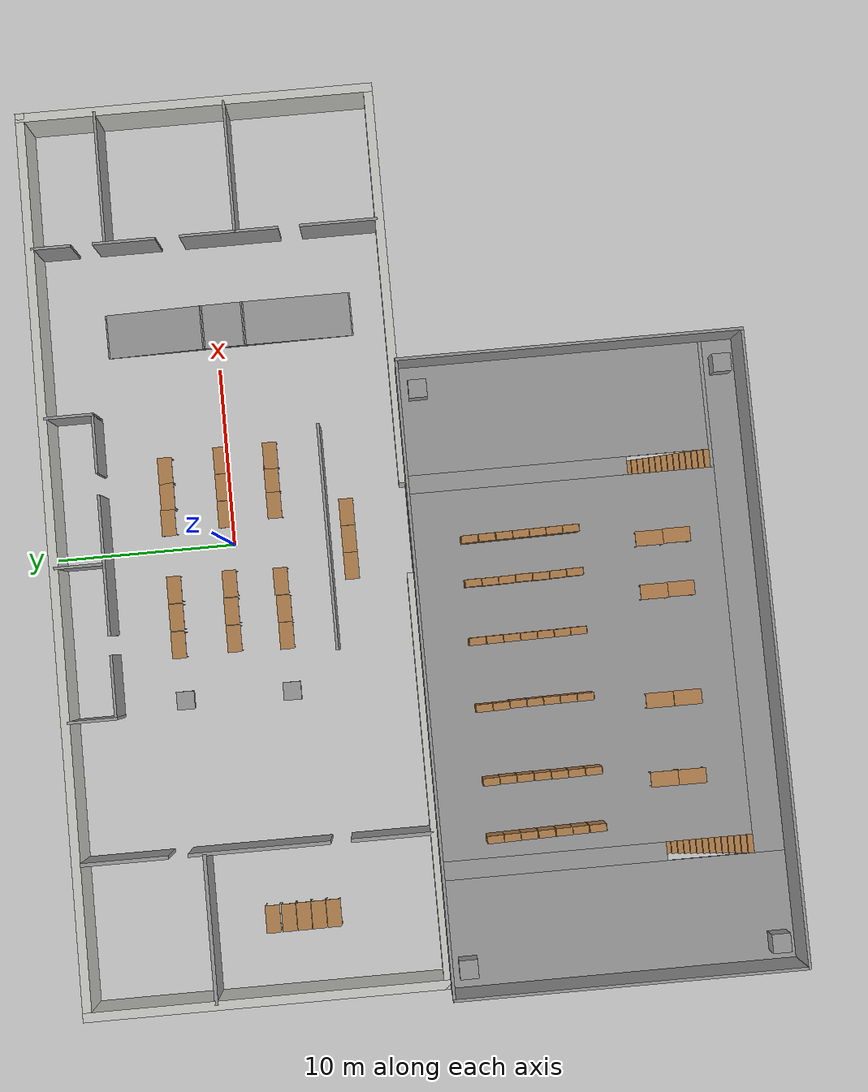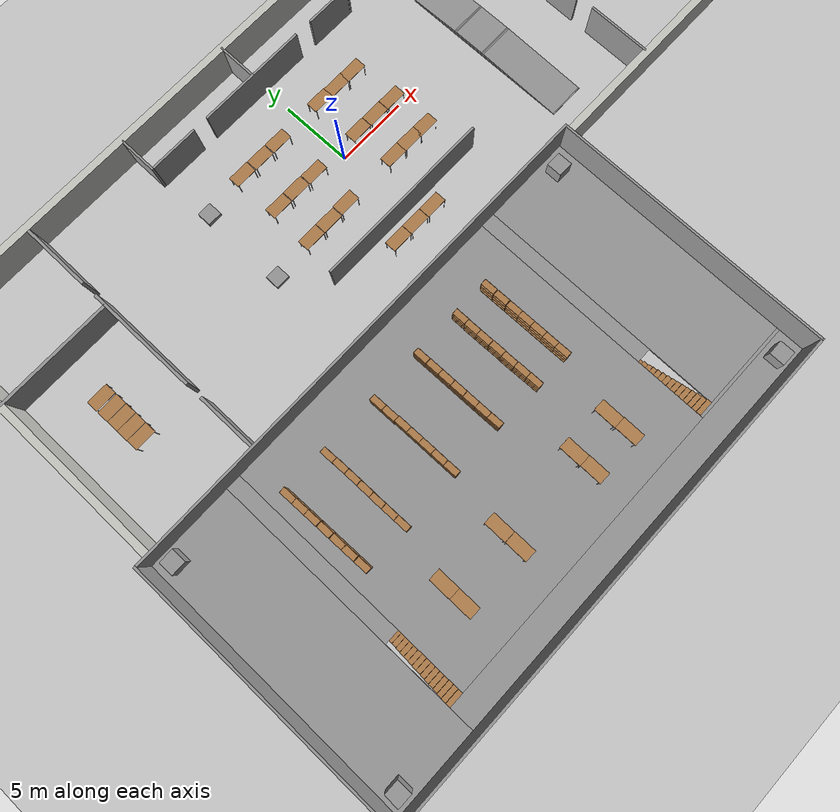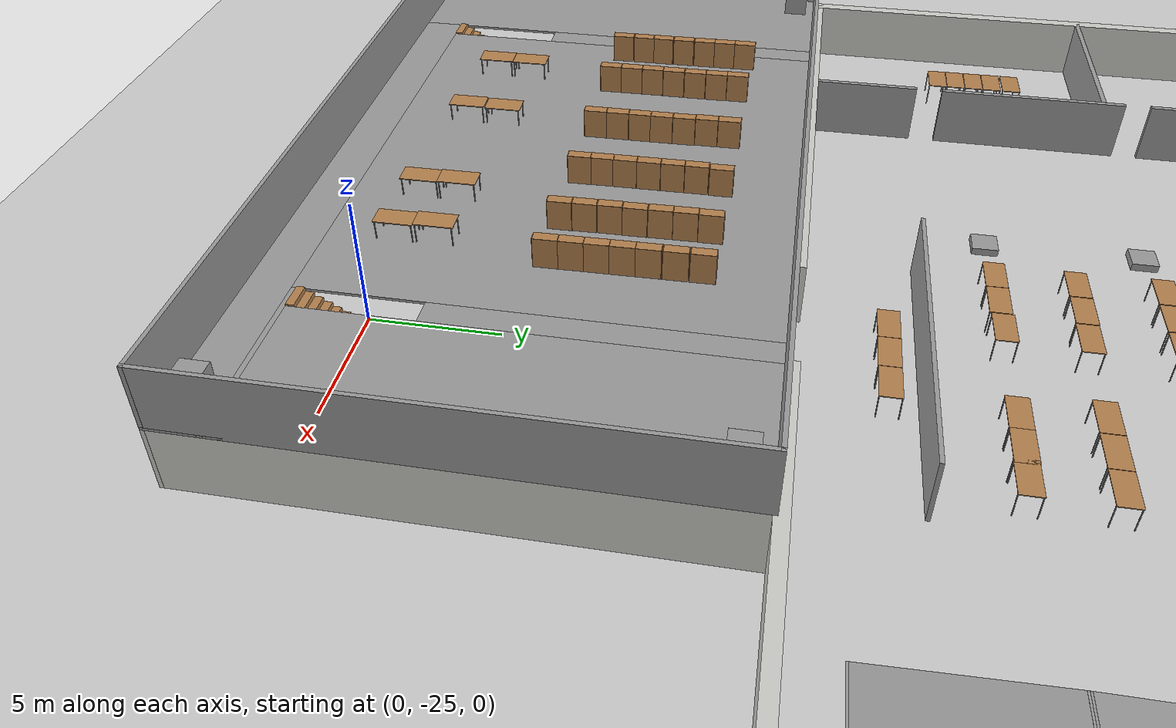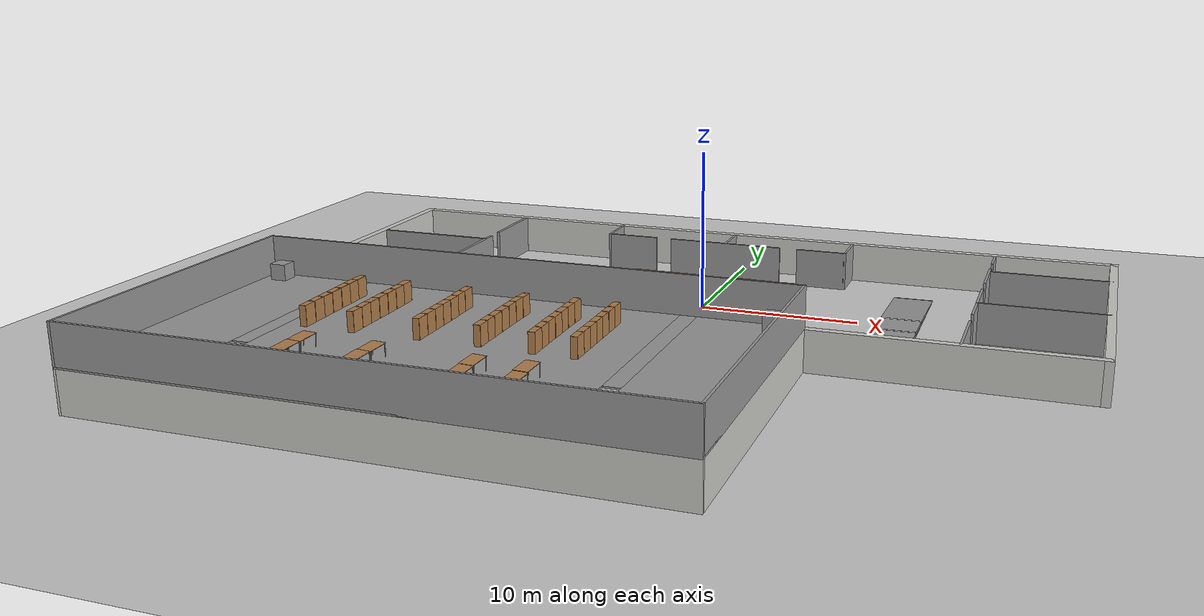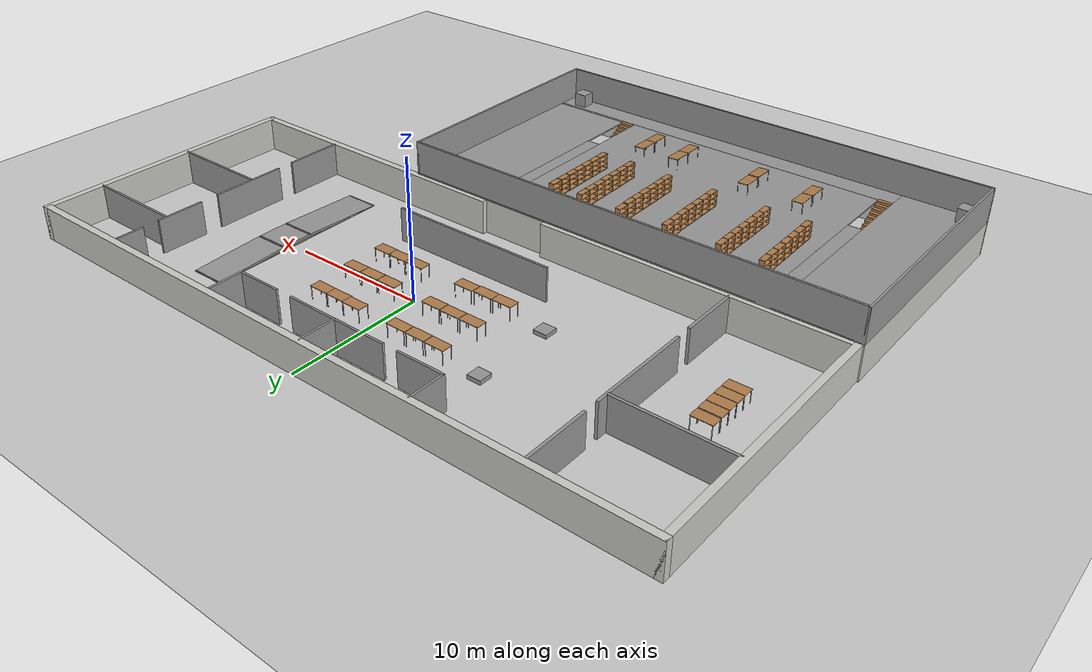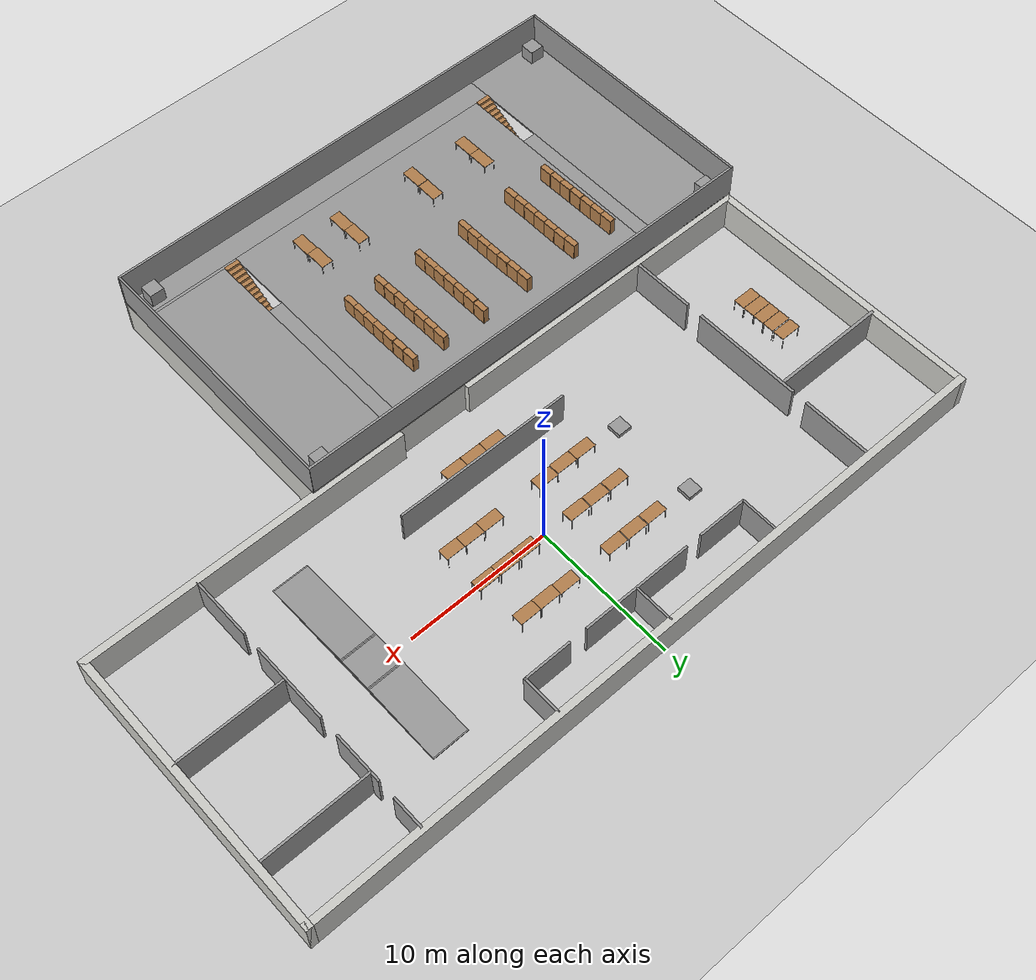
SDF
<sdf version="1.6">
 <world name="default">
  <light name="sun" type="directional">
   <pose>0 0 10 0 -0 0</pose>
   <diffuse>0.8 0.8 0.8 1</diffuse>
   <specular>0.2 0.2 0.2 1</specular>
   <attenuation>
    <range>1000</range>
    <constant>0.9</constant>
    <linear>0.01</linear>
    <quadratic>0.001</quadratic>
   </attenuation>
   <direction>-0.5 0.1 -0.9</direction>
  </light>
  <model name="ground_plane">
   <static>1</static>
   <link name="link">
    <collision name="collision">
     <geometry><plane><normal>0 0 1</normal><size>100 100</size></plane></geometry>
     <surface><friction><ode><mu>100</mu><mu2>50</mu2></ode></friction></surface>
    </collision>
    <visual name="visual">
     <cast_shadows>0</cast_shadows>
     <geometry><plane><normal>0 0 1</normal><size>100 100</size></plane></geometry>
     <material>
      <script><uri>file://media/materials/scripts/gazebo.material</uri><name>Gazebo/Grey</name></script>
     </material>
    </visual>
   </link>
  </model>
  <gravity>0 0 -9.8</gravity>
  <magnetic_field>6e-06 2.3e-05 -4.2e-05</magnetic_field>
  <atmosphere type="adiabatic"/>
  <physics name="default_physics" default="0" type="ode">
   <max_step_size>0.001</max_step_size>
   <real_time_factor>1</real_time_factor>
   <real_time_update_rate>1000</real_time_update_rate>
  </physics>
  <scene><ambient>0.4 0.4 0.4 1</ambient><background>0.7 0.7 0.7 1</background><shadows>1</shadows></scene>
  <audio><device>default</device></audio>
  <spherical_coordinates>
   <surface_model>EARTH_WGS84</surface_model>
   <latitude_deg>0</latitude_deg>
   <longitude_deg>0</longitude_deg>
   <elevation>0</elevation>
   <heading_deg>0</heading_deg>
  </spherical_coordinates>
  <model name="indemind_office">
   <pose>-0.0314 0.007006 0 0 -0 0</pose>
   <link name="Wall_1">
    <collision name="Wall_1_Collision">
     <geometry><box><size>20 0.5 2.5</size></box></geometry>
     <pose>0 0 1.25 0 -0 0</pose>
    </collision>
    <visual name="Wall_1_Visual">
     <pose>0 0 1.25 0 -0 0</pose>
     <geometry><box><size>20 0.5 2.5</size></box></geometry>
     <material>
      <script><uri>file://media/materials/scripts/gazebo.material</uri><name>Gazebo/CeilingTiled</name></script>
      <ambient>1 1 1 1</ambient>
     </material>
     <meta><layer>0</layer></meta>
    </visual>
    <pose>-24.75 -0 0 0 -0 -1.5708</pose>
   </link>
   <link name="Wall_11">
    <collision name="Wall_11_Collision">
     <geometry><box><size>20 0.5 2.5</size></box></geometry>
     <pose>0 0 1.25 0 -0 0</pose>
    </collision>
    <visual name="Wall_11_Visual">
     <pose>0 0 1.25 0 -0 0</pose>
     <geometry><box><size>20 0.5 2.5</size></box></geometry>
     <material>
      <script><uri>file://media/materials/scripts/gazebo.material</uri><name>Gazebo/CeilingTiled</name></script>
      <ambient>1 1 1 1</ambient>
     </material>
     <meta><layer>0</layer></meta>
    </visual>
    <pose>24.75 -0 0 0 -0 -1.5708</pose>
   </link>
   <link name="Wall_13">
    <collision name="Wall_13_Collision">
     <geometry><box><size>4.80017 0.2 2.5</size></box></geometry>
     <pose>0 0 1.25 0 -0 0</pose>
    </collision>
    <visual name="Wall_13_Visual">
     <pose>0 0 1.25 0 -0 0</pose>
     <geometry><box><size>4.80017 0.2 2.5</size></box></geometry>
     <material>
      <script><uri>file://media/materials/scripts/gazebo.material</uri><name>Gazebo/Grey</name></script>
      <ambient>1 1 1 1</ambient>
     </material>
     <meta><layer>0</layer></meta>
    </visual>
    <pose>-16.658 7.127 0 0 -0 -1.5708</pose>
   </link>
   <link name="Wall_15">
    <collision name="Wall_15_Collision">
     <geometry><box><size>7.75 0.2 2.5</size></box></geometry>
     <pose>0 0 1.25 0 -0 0</pose>
    </collision>
    <visual name="Wall_15_Visual">
     <pose>0 0 1.25 0 -0 0</pose>
     <geometry><box><size>7.75 0.2 2.5</size></box></geometry>
     <material>
      <script><uri>file://media/materials/scripts/gazebo.material</uri><name>Gazebo/Grey</name></script>
      <ambient>1 1 1 1</ambient>
     </material>
     <meta><layer>0</layer></meta>
    </visual>
    <pose>-16.658 -0.198 0 0 -0 -1.5708</pose>
   </link>
   <link name="Wall_17">
    <collision name="Wall_17_Collision">
     <geometry><box><size>4.5 0.2 2.5</size></box></geometry>
     <pose>0 0 1.25 0 -0 0</pose>
    </collision>
    <visual name="Wall_17_Visual">
     <pose>0 0 1.25 0 -0 0</pose>
     <geometry><box><size>4.5 0.2 2.5</size></box></geometry>
     <material>
      <script><uri>file://media/materials/scripts/gazebo.material</uri><name>Gazebo/Grey</name></script>
      <ambient>1 1 1 1</ambient>
     </material>
     <meta><layer>0</layer></meta>
    </visual>
    <pose>-16.658 -7.423 0 0 -0 -1.5708</pose>
   </link>
   <link name="Wall_19">
    <collision name="Wall_19_Collision">
     <geometry><box><size>8.04985 0.2 2.5</size></box></geometry>
     <pose>0 0 1.25 0 -0 0</pose>
    </collision>
    <visual name="Wall_19_Visual">
     <pose>0 0 1.25 0 -0 0</pose>
     <geometry><box><size>8.04985 0.2 2.5</size></box></geometry>
     <material>
      <script><uri>file://media/materials/scripts/gazebo.material</uri><name>Gazebo/Grey</name></script>
      <ambient>1 1 1 1</ambient>
     </material>
     <meta><layer>0</layer></meta>
    </visual>
    <pose>-20.703 2.792 0 0 -0 0</pose>
   </link>
   <link name="Wall_21">
    <collision name="Wall_21_Collision">
     <geometry><box><size>2.25 0.15 2.5</size></box></geometry>
     <pose>0 0 1.25 0 -0 0</pose>
    </collision>
    <visual name="Wall_21_Visual">
     <pose>0 0 1.25 0 -0 0</pose>
     <geometry><box><size>2.25 0.15 2.5</size></box></geometry>
     <material>
      <script><uri>file://media/materials/scripts/gazebo.material</uri><name>Gazebo/Grey</name></script>
      <ambient>1 1 1 1</ambient>
     </material>
     <meta><layer>0</layer></meta>
    </visual>
    <pose>17.2839 8.57905 0 0 -0 -1.57072</pose>
   </link>
   <link name="Wall_23">
    <collision name="Wall_23_Collision">
     <geometry><box><size>3.5 0.15 2.5</size></box></geometry>
     <pose>0 0 1.25 0 -0 0</pose>
    </collision>
    <visual name="Wall_23_Visual">
     <pose>0 0 1.25 0 -0 0</pose>
     <geometry><box><size>3.5 0.15 2.5</size></box></geometry>
     <material>
      <script><uri>file://media/materials/scripts/gazebo.material</uri><name>Gazebo/Grey</name></script>
      <ambient>1 1 1 1</ambient>
     </material>
     <meta><layer>0</layer></meta>
    </visual>
    <pose>17.2838 4.5041 0 0 -0 -1.5708</pose>
   </link>
   <link name="Wall_25">
    <collision name="Wall_25_Collision">
     <geometry><box><size>5.5 0.15 2.5</size></box></geometry>
     <pose>0 0 1.25 0 -0 0</pose>
    </collision>
    <visual name="Wall_25_Visual">
     <pose>0 0 1.25 0 -0 0</pose>
     <geometry><box><size>5.5 0.15 2.5</size></box></geometry>
     <material>
      <script><uri>file://media/materials/scripts/gazebo.material</uri><name>Gazebo/Grey</name></script>
      <ambient>1 1 1 1</ambient>
     </material>
     <meta><layer>0</layer></meta>
    </visual>
    <pose>17.2838 -1.3459 0 0 -0 -1.5708</pose>
   </link>
   <link name="Wall_27">
    <collision name="Wall_27_Collision">
     <geometry><box><size>4.35 0.15 2.5</size></box></geometry>
     <pose>0 0 1.25 0 -0 0</pose>
    </collision>
    <visual name="Wall_27_Visual">
     <pose>0 0 1.25 0 -0 0</pose>
     <geometry><box><size>4.35 0.15 2.5</size></box></geometry>
     <material>
      <script><uri>file://media/materials/scripts/gazebo.material</uri><name>Gazebo/Grey</name></script>
      <ambient>1 1 1 1</ambient>
     </material>
     <meta><layer>0</layer></meta>
    </visual>
    <pose>17.2838 -7.4709 0 0 -0 -1.5708</pose>
   </link>
   <link name="Wall_29">
    <collision name="Wall_29_Collision">
     <geometry><box><size>7.5 0.15 2.5</size></box></geometry>
     <pose>0 0 1.25 0 -0 0</pose>
    </collision>
    <visual name="Wall_29_Visual">
     <pose>0 0 1.25 0 -0 0</pose>
     <geometry><box><size>7.5 0.15 2.5</size></box></geometry>
     <material>
      <script><uri>file://media/materials/scripts/gazebo.material</uri><name>Gazebo/Grey</name></script>
      <ambient>1 1 1 1</ambient>
     </material>
     <meta><layer>0</layer></meta>
    </visual>
    <pose>20.9993 5.58355 0 0 -0 0</pose>
   </link>
   <link name="Wall_3">
    <collision name="Wall_3_Collision">
     <geometry><box><size>50 0.5 2.5</size></box></geometry>
     <pose>0 0 1.25 0 -0 0</pose>
    </collision>
    <visual name="Wall_3_Visual">
     <pose>0 0 1.25 0 -0 0</pose>
     <geometry><box><size>50 0.5 2.5</size></box></geometry>
     <material>
      <script><uri>file://media/materials/scripts/gazebo.material</uri><name>Gazebo/CeilingTiled</name></script>
      <ambient>1 1 1 1</ambient>
     </material>
     <meta><layer>0</layer></meta>
    </visual>
    <pose>-1e-06 9.75 0 0 -0 0</pose>
   </link>
   <link name="Wall_31">
    <collision name="Wall_31_Collision">
     <geometry><box><size>7.5 0.15 2.5</size></box></geometry>
     <pose>0 0 1.25 0 -0 0</pose>
    </collision>
    <visual name="Wall_31_Visual">
     <pose>0 0 1.25 0 -0 0</pose>
     <geometry><box><size>7.5 0.15 2.5</size></box></geometry>
     <material>
      <script><uri>file://media/materials/scripts/gazebo.material</uri><name>Gazebo/Grey</name></script>
      <ambient>1 1 1 1</ambient>
     </material>
     <meta><layer>0</layer></meta>
    </visual>
    <pose>20.9993 -1.658 0 0 -0 0</pose>
   </link>
   <link name="Wall_34">
    <collision name="Wall_34_Collision">
     <geometry><box><size>2.75032 0.15 2.5</size></box></geometry>
     <pose>0 0 1.25 0 -0 0</pose>
    </collision>
    <visual name="Wall_34_Visual">
     <pose>0 0 1.25 0 -0 0</pose>
     <geometry><box><size>2.75032 0.15 2.5</size></box></geometry>
     <material>
      <script><uri>file://media/materials/scripts/gazebo.material</uri><name>Gazebo/Grey</name></script>
      <ambient>1 1 1 1</ambient>
     </material>
     <meta><layer>0</layer></meta>
    </visual>
    <pose>-8.97184 8.28865 0 0 -0 -1.5708</pose>
   </link>
   <link name="Wall_35">
    <collision name="Wall_35_Collision">
     <geometry><box><size>3.5 0.15 2.5</size></box></geometry>
     <pose>0 0 1.25 0 -0 0</pose>
    </collision>
    <visual name="Wall_35_Visual">
     <pose>0 0 1.25 0 -0 0</pose>
     <geometry><box><size>3.5 0.15 2.5</size></box></geometry>
     <material>
      <script><uri>file://media/materials/scripts/gazebo.material</uri><name>Gazebo/Grey</name></script>
      <ambient>1 1 1 1</ambient>
     </material>
     <meta><layer>0</layer></meta>
    </visual>
    <pose>-7.25638 6.98865 0 0 -0 0</pose>
   </link>
   <link name="Wall_37">
    <collision name="Wall_37_Collision">
     <geometry><box><size>7.75 0.15 2.5</size></box></geometry>
     <pose>0 0 1.25 0 -0 0</pose>
    </collision>
    <visual name="Wall_37_Visual">
     <pose>0 0 1.25 0 -0 0</pose>
     <geometry><box><size>7.75 0.15 2.5</size></box></geometry>
     <material>
      <script><uri>file://media/materials/scripts/gazebo.material</uri><name>Gazebo/Grey</name></script>
      <ambient>1 1 1 1</ambient>
     </material>
     <meta><layer>0</layer></meta>
    </visual>
    <pose>-0.572001 6.989 0 0 -0 0</pose>
   </link>
   <link name="Wall_39">
    <collision name="Wall_39_Collision">
     <geometry><box><size>3.35 0.15 2.5</size></box></geometry>
     <pose>0 0 1.25 0 -0 0</pose>
    </collision>
    <visual name="Wall_39_Visual">
     <pose>0 0 1.25 0 -0 0</pose>
     <geometry><box><size>3.35 0.15 2.5</size></box></geometry>
     <material>
      <script><uri>file://media/materials/scripts/gazebo.material</uri><name>Gazebo/Grey</name></script>
      <ambient>1 1 1 1</ambient>
     </material>
     <meta><layer>0</layer></meta>
    </visual>
    <pose>6.17808 6.98882 0 0 -0 -0.00011</pose>
   </link>
   <link name="Wall_40">
    <collision name="Wall_40_Collision">
     <geometry><box><size>2.75 0.15 2.5</size></box></geometry>
     <pose>0 0 1.25 0 -0 0</pose>
    </collision>
    <visual name="Wall_40_Visual">
     <pose>0 0 1.25 0 -0 0</pose>
     <geometry><box><size>2.75 0.15 2.5</size></box></geometry>
     <material>
      <script><uri>file://media/materials/scripts/gazebo.material</uri><name>Gazebo/Grey</name></script>
      <ambient>1 1 1 1</ambient>
     </material>
     <meta><layer>0</layer></meta>
    </visual>
    <pose>7.77816 8.28865 0 0 -0 1.5708</pose>
   </link>
   <link name="Wall_42">
    <collision name="Wall_42_Collision">
     <geometry><box><size>2.75 0.15 2.5</size></box></geometry>
     <pose>0 0 1.25 0 -0 0</pose>
    </collision>
    <visual name="Wall_42_Visual">
     <pose>0 0 1.25 0 -0 0</pose>
     <geometry><box><size>2.75 0.15 2.5</size></box></geometry>
     <material>
      <script><uri>file://media/materials/scripts/gazebo.material</uri><name>Gazebo/Grey</name></script>
      <ambient>1 1 1 1</ambient>
     </material>
     <meta><layer>0</layer></meta>
    </visual>
    <pose>-0.516625 8.36956 0 0 -0 -1.5708</pose>
   </link>
   <link name="Wall_44">
    <collision name="Wall_44_Collision">
     <geometry><box><size>12.5 0.15 2.5</size></box></geometry>
     <pose>0 0 1.25 0 -0 0</pose>
    </collision>
    <visual name="Wall_44_Visual">
     <pose>0 0 1.25 0 -0 0</pose>
     <geometry><box><size>12.5 0.15 2.5</size></box></geometry>
     <material>
      <script><uri>file://media/materials/scripts/gazebo.material</uri><name>Gazebo/Grey</name></script>
      <ambient>1 1 1 1</ambient>
     </material>
     <meta><layer>0</layer></meta>
    </visual>
    <pose>-0.086317 -5.33946 0 0 -0 0</pose>
   </link>
   <link name="Wall_7">
    <collision name="Wall_7_Collision">
     <geometry><box><size>22.5 0.5 2.5</size></box></geometry>
     <pose>0 0 1.25 0 -0 0</pose>
    </collision>
    <visual name="Wall_7_Visual">
     <pose>0 0 1.25 0 -0 0</pose>
     <geometry><box><size>22.5 0.5 2.5</size></box></geometry>
     <material>
      <script><uri>file://media/materials/scripts/gazebo.material</uri><name>Gazebo/CeilingTiled</name></script>
      <ambient>1 1 1 1</ambient>
     </material>
     <meta><layer>0</layer></meta>
    </visual>
    <pose>-13.75 -9.75 0 0 -0 0</pose>
   </link>
   <link name="Wall_9">
    <collision name="Wall_9_Collision">
     <geometry><box><size>22.5 0.5 2.5</size></box></geometry>
     <pose>0 0 1.25 0 -0 0</pose>
    </collision>
    <visual name="Wall_9_Visual">
     <pose>0 0 1.25 0 -0 0</pose>
     <geometry><box><size>22.5 0.5 2.5</size></box></geometry>
     <material>
      <script><uri>file://media/materials/scripts/gazebo.material</uri><name>Gazebo/CeilingTiled</name></script>
      <ambient>1 1 1 1</ambient>
     </material>
     <meta><layer>0</layer></meta>
    </visual>
    <pose>13.7296 -9.74954 0 0 -0 0</pose>
   </link>
   <static>1</static>
  </model>
  <model name="table">
   <static>1</static>
   <link name="link">
    <collision name="surface">
     <pose>0 0 1 0 -0 0</pose>
     <geometry><box><size>1.5 0.8 0.03</size></box></geometry>
     <surface><friction><ode><mu>0.6</mu><mu2>0.6</mu2></ode></friction></surface>
    </collision>
    <visual name="visual1">
     <pose>0 0 1 0 -0 0</pose>
     <geometry><box><size>1.5 0.8 0.03</size></box></geometry>
     <material>
      <script><uri>file://media/materials/scripts/gazebo.material</uri><name>Gazebo/Wood</name></script>
     </material>
    </visual>
    <collision name="front_left_leg">
     <pose>0.68 0.38 0.5 0 -0 0</pose>
     <geometry><cylinder><radius>0.02</radius><length>1</length></cylinder></geometry>
    </collision>
    <visual name="front_left_leg">
     <pose>0.68 0.38 0.5 0 -0 0</pose>
     <geometry><cylinder><radius>0.02</radius><length>1</length></cylinder></geometry>
     <material>
      <script><uri>file://media/materials/scripts/gazebo.material</uri><name>Gazebo/Grey</name></script>
     </material>
    </visual>
    <collision name="front_right_leg">
     <pose>0.68 -0.38 0.5 0 -0 0</pose>
     <geometry><cylinder><radius>0.02</radius><length>1</length></cylinder></geometry>
    </collision>
    <visual name="front_right_leg">
     <pose>0.68 -0.38 0.5 0 -0 0</pose>
     <geometry><cylinder><radius>0.02</radius><length>1</length></cylinder></geometry>
     <material>
      <script><uri>file://media/materials/scripts/gazebo.material</uri><name>Gazebo/Grey</name></script>
     </material>
    </visual>
    <collision name="back_right_leg">
     <pose>-0.68 -0.38 0.5 0 -0 0</pose>
     <geometry><cylinder><radius>0.02</radius><length>1</length></cylinder></geometry>
    </collision>
    <visual name="back_right_leg">
     <pose>-0.68 -0.38 0.5 0 -0 0</pose>
     <geometry><cylinder><radius>0.02</radius><length>1</length></cylinder></geometry>
     <material>
      <script><uri>file://media/materials/scripts/gazebo.material</uri><name>Gazebo/Grey</name></script>
     </material>
    </visual>
    <collision name="back_left_leg">
     <pose>-0.68 0.38 0.5 0 -0 0</pose>
     <geometry><cylinder><radius>0.02</radius><length>1</length></cylinder></geometry>
    </collision>
    <visual name="back_left_leg">
     <pose>-0.68 0.38 0.5 0 -0 0</pose>
     <geometry><cylinder><radius>0.02</radius><length>1</length></cylinder></geometry>
     <material>
      <script><uri>file://media/materials/scripts/gazebo.material</uri><name>Gazebo/Grey</name></script>
     </material>
    </visual>
   </link>
   <pose>-1.77581 -6.45658 0 0 -0 0</pose>
  </model>
  <model name="table_0">
   <static>1</static>
   <link name="link">
    <collision name="surface">
     <pose>0 0 1 0 -0 0</pose>
     <geometry><box><size>1.5 0.8 0.03</size></box></geometry>
     <surface><friction><ode><mu>0.6</mu><mu2>0.6</mu2></ode></friction></surface>
    </collision>
    <visual name="visual1">
     <pose>0 0 1 0 -0 0</pose>
     <geometry><box><size>1.5 0.8 0.03</size></box></geometry>
     <material>
      <script><uri>file://media/materials/scripts/gazebo.material</uri><name>Gazebo/Wood</name></script>
     </material>
    </visual>
    <collision name="front_left_leg">
     <pose>0.68 0.38 0.5 0 -0 0</pose>
     <geometry><cylinder><radius>0.02</radius><length>1</length></cylinder></geometry>
    </collision>
    <visual name="front_left_leg">
     <pose>0.68 0.38 0.5 0 -0 0</pose>
     <geometry><cylinder><radius>0.02</radius><length>1</length></cylinder></geometry>
     <material>
      <script><uri>file://media/materials/scripts/gazebo.material</uri><name>Gazebo/Grey</name></script>
     </material>
    </visual>
    <collision name="front_right_leg">
     <pose>0.68 -0.38 0.5 0 -0 0</pose>
     <geometry><cylinder><radius>0.02</radius><length>1</length></cylinder></geometry>
    </collision>
    <visual name="front_right_leg">
     <pose>0.68 -0.38 0.5 0 -0 0</pose>
     <geometry><cylinder><radius>0.02</radius><length>1</length></cylinder></geometry>
     <material>
      <script><uri>file://media/materials/scripts/gazebo.material</uri><name>Gazebo/Grey</name></script>
     </material>
    </visual>
    <collision name="back_right_leg">
     <pose>-0.68 -0.38 0.5 0 -0 0</pose>
     <geometry><cylinder><radius>0.02</radius><length>1</length></cylinder></geometry>
    </collision>
    <visual name="back_right_leg">
     <pose>-0.68 -0.38 0.5 0 -0 0</pose>
     <geometry><cylinder><radius>0.02</radius><length>1</length></cylinder></geometry>
     <material>
      <script><uri>file://media/materials/scripts/gazebo.material</uri><name>Gazebo/Grey</name></script>
     </material>
    </visual>
    <collision name="back_left_leg">
     <pose>-0.68 0.38 0.5 0 -0 0</pose>
     <geometry><cylinder><radius>0.02</radius><length>1</length></cylinder></geometry>
    </collision>
    <visual name="back_left_leg">
     <pose>-0.68 0.38 0.5 0 -0 0</pose>
     <geometry><cylinder><radius>0.02</radius><length>1</length></cylinder></geometry>
     <material>
      <script><uri>file://media/materials/scripts/gazebo.material</uri><name>Gazebo/Grey</name></script>
     </material>
    </visual>
   </link>
   <pose>-0.266949 -6.45533 0 0 -0 0</pose>
  </model>
  <model name="table_1">
   <static>1</static>
   <link name="link">
    <collision name="surface">
     <pose>0 0 1 0 -0 0</pose>
     <geometry><box><size>1.5 0.8 0.03</size></box></geometry>
     <surface><friction><ode><mu>0.6</mu><mu2>0.6</mu2></ode></friction></surface>
    </collision>
    <visual name="visual1">
     <pose>0 0 1 0 -0 0</pose>
     <geometry><box><size>1.5 0.8 0.03</size></box></geometry>
     <material>
      <script><uri>file://media/materials/scripts/gazebo.material</uri><name>Gazebo/Wood</name></script>
     </material>
    </visual>
    <collision name="front_left_leg">
     <pose>0.68 0.38 0.5 0 -0 0</pose>
     <geometry><cylinder><radius>0.02</radius><length>1</length></cylinder></geometry>
    </collision>
    <visual name="front_left_leg">
     <pose>0.68 0.38 0.5 0 -0 0</pose>
     <geometry><cylinder><radius>0.02</radius><length>1</length></cylinder></geometry>
     <material>
      <script><uri>file://media/materials/scripts/gazebo.material</uri><name>Gazebo/Grey</name></script>
     </material>
    </visual>
    <collision name="front_right_leg">
     <pose>0.68 -0.38 0.5 0 -0 0</pose>
     <geometry><cylinder><radius>0.02</radius><length>1</length></cylinder></geometry>
    </collision>
    <visual name="front_right_leg">
     <pose>0.68 -0.38 0.5 0 -0 0</pose>
     <geometry><cylinder><radius>0.02</radius><length>1</length></cylinder></geometry>
     <material>
      <script><uri>file://media/materials/scripts/gazebo.material</uri><name>Gazebo/Grey</name></script>
     </material>
    </visual>
    <collision name="back_right_leg">
     <pose>-0.68 -0.38 0.5 0 -0 0</pose>
     <geometry><cylinder><radius>0.02</radius><length>1</length></cylinder></geometry>
    </collision>
    <visual name="back_right_leg">
     <pose>-0.68 -0.38 0.5 0 -0 0</pose>
     <geometry><cylinder><radius>0.02</radius><length>1</length></cylinder></geometry>
     <material>
      <script><uri>file://media/materials/scripts/gazebo.material</uri><name>Gazebo/Grey</name></script>
     </material>
    </visual>
    <collision name="back_left_leg">
     <pose>-0.68 0.38 0.5 0 -0 0</pose>
     <geometry><cylinder><radius>0.02</radius><length>1</length></cylinder></geometry>
    </collision>
    <visual name="back_left_leg">
     <pose>-0.68 0.38 0.5 0 -0 0</pose>
     <geometry><cylinder><radius>0.02</radius><length>1</length></cylinder></geometry>
     <material>
      <script><uri>file://media/materials/scripts/gazebo.material</uri><name>Gazebo/Grey</name></script>
     </material>
    </visual>
   </link>
   <pose>1.24514 -6.45321 0 0 -0 0</pose>
  </model>
  <model name="unit_box">
   <pose>-8.43299 3.46662 0.150675 0 -0 0</pose>
   <link name="link">
    <inertial>
     <mass>1</mass>
     <inertia>
      <ixx>0.166667</ixx>
      <ixy>0</ixy>
      <ixz>0</ixz>
      <iyy>0.166667</iyy>
      <iyz>0</iyz>
      <izz>0.166667</izz>
     </inertia>
    </inertial>
    <collision name="collision"><geometry><box><size>1 1 0.30135</size></box></geometry></collision>
    <visual name="visual">
     <geometry><box><size>1 1 0.30135</size></box></geometry>
     <material>
      <script><name>Gazebo/Grey</name><uri>file://media/materials/scripts/gazebo.material</uri></script>
     </material>
    </visual>
   </link>
  </model>
  <model name="unit_box_0">
   <pose>-8.43373 -2.51764 0.14306 0 -0 0</pose>
   <link name="link">
    <inertial>
     <mass>1</mass>
     <inertia>
      <ixx>0.166667</ixx>
      <ixy>0</ixy>
      <ixz>0</ixz>
      <iyy>0.166667</iyy>
      <iyz>0</iyz>
      <izz>0.166667</izz>
     </inertia>
    </inertial>
    <collision name="collision"><geometry><box><size>1 0.999997 0.28612</size></box></geometry></collision>
    <visual name="visual">
     <geometry><box><size>1 0.999997 0.28612</size></box></geometry>
     <material>
      <script><name>Gazebo/Grey</name><uri>file://media/materials/scripts/gazebo.material</uri></script>
     </material>
    </visual>
    <enable_wind>1</enable_wind>
   </link>
   <enable_wind>1</enable_wind>
  </model>
  <model name="table_2">
   <static>1</static>
   <link name="link">
    <collision name="surface">
     <pose>0 0 1 0 -0 0</pose>
     <geometry><box><size>1.5 0.8 0.03</size></box></geometry>
     <surface><friction><ode><mu>0.6</mu><mu2>0.6</mu2></ode></friction></surface>
    </collision>
    <visual name="visual1">
     <pose>0 0 1 0 -0 0</pose>
     <geometry><box><size>1.5 0.8 0.03</size></box></geometry>
     <material>
      <script><uri>file://media/materials/scripts/gazebo.material</uri><name>Gazebo/Wood</name></script>
     </material>
    </visual>
    <collision name="front_left_leg">
     <pose>0.68 0.38 0.5 0 -0 0</pose>
     <geometry><cylinder><radius>0.02</radius><length>1</length></cylinder></geometry>
    </collision>
    <visual name="front_left_leg">
     <pose>0.68 0.38 0.5 0 -0 0</pose>
     <geometry><cylinder><radius>0.02</radius><length>1</length></cylinder></geometry>
     <material>
      <script><uri>file://media/materials/scripts/gazebo.material</uri><name>Gazebo/Grey</name></script>
     </material>
    </visual>
    <collision name="front_right_leg">
     <pose>0.68 -0.38 0.5 0 -0 0</pose>
     <geometry><cylinder><radius>0.02</radius><length>1</length></cylinder></geometry>
    </collision>
    <visual name="front_right_leg">
     <pose>0.68 -0.38 0.5 0 -0 0</pose>
     <geometry><cylinder><radius>0.02</radius><length>1</length></cylinder></geometry>
     <material>
      <script><uri>file://media/materials/scripts/gazebo.material</uri><name>Gazebo/Grey</name></script>
     </material>
    </visual>
    <collision name="back_right_leg">
     <pose>-0.68 -0.38 0.5 0 -0 0</pose>
     <geometry><cylinder><radius>0.02</radius><length>1</length></cylinder></geometry>
    </collision>
    <visual name="back_right_leg">
     <pose>-0.68 -0.38 0.5 0 -0 0</pose>
     <geometry><cylinder><radius>0.02</radius><length>1</length></cylinder></geometry>
     <material>
      <script><uri>file://media/materials/scripts/gazebo.material</uri><name>Gazebo/Grey</name></script>
     </material>
    </visual>
    <collision name="back_left_leg">
     <pose>-0.68 0.38 0.5 0 -0 0</pose>
     <geometry><cylinder><radius>0.02</radius><length>1</length></cylinder></geometry>
    </collision>
    <visual name="back_left_leg">
     <pose>-0.68 0.38 0.5 0 -0 0</pose>
     <geometry><cylinder><radius>0.02</radius><length>1</length></cylinder></geometry>
     <material>
      <script><uri>file://media/materials/scripts/gazebo.material</uri><name>Gazebo/Grey</name></script>
     </material>
    </visual>
   </link>
   <pose>-5.31157 3.49328 0 0 -0 0</pose>
  </model>
  <model name="table_3">
   <static>1</static>
   <link name="link">
    <collision name="surface">
     <pose>0 0 1 0 -0 0</pose>
     <geometry><box><size>1.5 0.8 0.03</size></box></geometry>
     <surface><friction><ode><mu>0.6</mu><mu2>0.6</mu2></ode></friction></surface>
    </collision>
    <visual name="visual1">
     <pose>0 0 1 0 -0 0</pose>
     <geometry><box><size>1.5 0.8 0.03</size></box></geometry>
     <material>
      <script><uri>file://media/materials/scripts/gazebo.material</uri><name>Gazebo/Wood</name></script>
     </material>
    </visual>
    <collision name="front_left_leg">
     <pose>0.68 0.38 0.5 0 -0 0</pose>
     <geometry><cylinder><radius>0.02</radius><length>1</length></cylinder></geometry>
    </collision>
    <visual name="front_left_leg">
     <pose>0.68 0.38 0.5 0 -0 0</pose>
     <geometry><cylinder><radius>0.02</radius><length>1</length></cylinder></geometry>
     <material>
      <script><uri>file://media/materials/scripts/gazebo.material</uri><name>Gazebo/Grey</name></script>
     </material>
    </visual>
    <collision name="front_right_leg">
     <pose>0.68 -0.38 0.5 0 -0 0</pose>
     <geometry><cylinder><radius>0.02</radius><length>1</length></cylinder></geometry>
    </collision>
    <visual name="front_right_leg">
     <pose>0.68 -0.38 0.5 0 -0 0</pose>
     <geometry><cylinder><radius>0.02</radius><length>1</length></cylinder></geometry>
     <material>
      <script><uri>file://media/materials/scripts/gazebo.material</uri><name>Gazebo/Grey</name></script>
     </material>
    </visual>
    <collision name="back_right_leg">
     <pose>-0.68 -0.38 0.5 0 -0 0</pose>
     <geometry><cylinder><radius>0.02</radius><length>1</length></cylinder></geometry>
    </collision>
    <visual name="back_right_leg">
     <pose>-0.68 -0.38 0.5 0 -0 0</pose>
     <geometry><cylinder><radius>0.02</radius><length>1</length></cylinder></geometry>
     <material>
      <script><uri>file://media/materials/scripts/gazebo.material</uri><name>Gazebo/Grey</name></script>
     </material>
    </visual>
    <collision name="back_left_leg">
     <pose>-0.68 0.38 0.5 0 -0 0</pose>
     <geometry><cylinder><radius>0.02</radius><length>1</length></cylinder></geometry>
    </collision>
    <visual name="back_left_leg">
     <pose>-0.68 0.38 0.5 0 -0 0</pose>
     <geometry><cylinder><radius>0.02</radius><length>1</length></cylinder></geometry>
     <material>
      <script><uri>file://media/materials/scripts/gazebo.material</uri><name>Gazebo/Grey</name></script>
     </material>
    </visual>
   </link>
   <pose>-3.76952 3.48462 0 0 -0 0</pose>
  </model>
  <model name="table_4">
   <static>1</static>
   <link name="link">
    <collision name="surface">
     <pose>0 0 1 0 -0 0</pose>
     <geometry><box><size>1.5 0.8 0.03</size></box></geometry>
     <surface><friction><ode><mu>0.6</mu><mu2>0.6</mu2></ode></friction></surface>
    </collision>
    <visual name="visual1">
     <pose>0 0 1 0 -0 0</pose>
     <geometry><box><size>1.5 0.8 0.03</size></box></geometry>
     <material>
      <script><uri>file://media/materials/scripts/gazebo.material</uri><name>Gazebo/Wood</name></script>
     </material>
    </visual>
    <collision name="front_left_leg">
     <pose>0.68 0.38 0.5 0 -0 0</pose>
     <geometry><cylinder><radius>0.02</radius><length>1</length></cylinder></geometry>
    </collision>
    <visual name="front_left_leg">
     <pose>0.68 0.38 0.5 0 -0 0</pose>
     <geometry><cylinder><radius>0.02</radius><length>1</length></cylinder></geometry>
     <material>
      <script><uri>file://media/materials/scripts/gazebo.material</uri><name>Gazebo/Grey</name></script>
     </material>
    </visual>
    <collision name="front_right_leg">
     <pose>0.68 -0.38 0.5 0 -0 0</pose>
     <geometry><cylinder><radius>0.02</radius><length>1</length></cylinder></geometry>
    </collision>
    <visual name="front_right_leg">
     <pose>0.68 -0.38 0.5 0 -0 0</pose>
     <geometry><cylinder><radius>0.02</radius><length>1</length></cylinder></geometry>
     <material>
      <script><uri>file://media/materials/scripts/gazebo.material</uri><name>Gazebo/Grey</name></script>
     </material>
    </visual>
    <collision name="back_right_leg">
     <pose>-0.68 -0.38 0.5 0 -0 0</pose>
     <geometry><cylinder><radius>0.02</radius><length>1</length></cylinder></geometry>
    </collision>
    <visual name="back_right_leg">
     <pose>-0.68 -0.38 0.5 0 -0 0</pose>
     <geometry><cylinder><radius>0.02</radius><length>1</length></cylinder></geometry>
     <material>
      <script><uri>file://media/materials/scripts/gazebo.material</uri><name>Gazebo/Grey</name></script>
     </material>
    </visual>
    <collision name="back_left_leg">
     <pose>-0.68 0.38 0.5 0 -0 0</pose>
     <geometry><cylinder><radius>0.02</radius><length>1</length></cylinder></geometry>
    </collision>
    <visual name="back_left_leg">
     <pose>-0.68 0.38 0.5 0 -0 0</pose>
     <geometry><cylinder><radius>0.02</radius><length>1</length></cylinder></geometry>
     <material>
      <script><uri>file://media/materials/scripts/gazebo.material</uri><name>Gazebo/Grey</name></script>
     </material>
    </visual>
   </link>
   <pose>-2.2286 3.48108 0 0 -0 0</pose>
  </model>
  <model name="table_9">
   <static>1</static>
   <link name="link">
    <collision name="surface">
     <pose>0 0 1 0 -0 0</pose>
     <geometry><box><size>1.5 0.8 0.03</size></box></geometry>
     <surface><friction><ode><mu>0.6</mu><mu2>0.6</mu2></ode></friction></surface>
    </collision>
    <visual name="visual1">
     <pose>0 0 1 0 -0 0</pose>
     <geometry><box><size>1.5 0.8 0.03</size></box></geometry>
     <material>
      <script><uri>file://media/materials/scripts/gazebo.material</uri><name>Gazebo/Wood</name></script>
     </material>
    </visual>
    <collision name="front_left_leg">
     <pose>0.68 0.38 0.5 0 -0 0</pose>
     <geometry><cylinder><radius>0.02</radius><length>1</length></cylinder></geometry>
    </collision>
    <visual name="front_left_leg">
     <pose>0.68 0.38 0.5 0 -0 0</pose>
     <geometry><cylinder><radius>0.02</radius><length>1</length></cylinder></geometry>
     <material>
      <script><uri>file://media/materials/scripts/gazebo.material</uri><name>Gazebo/Grey</name></script>
     </material>
    </visual>
    <collision name="front_right_leg">
     <pose>0.68 -0.38 0.5 0 -0 0</pose>
     <geometry><cylinder><radius>0.02</radius><length>1</length></cylinder></geometry>
    </collision>
    <visual name="front_right_leg">
     <pose>0.68 -0.38 0.5 0 -0 0</pose>
     <geometry><cylinder><radius>0.02</radius><length>1</length></cylinder></geometry>
     <material>
      <script><uri>file://media/materials/scripts/gazebo.material</uri><name>Gazebo/Grey</name></script>
     </material>
    </visual>
    <collision name="back_right_leg">
     <pose>-0.68 -0.38 0.5 0 -0 0</pose>
     <geometry><cylinder><radius>0.02</radius><length>1</length></cylinder></geometry>
    </collision>
    <visual name="back_right_leg">
     <pose>-0.68 -0.38 0.5 0 -0 0</pose>
     <geometry><cylinder><radius>0.02</radius><length>1</length></cylinder></geometry>
     <material>
      <script><uri>file://media/materials/scripts/gazebo.material</uri><name>Gazebo/Grey</name></script>
     </material>
    </visual>
    <collision name="back_left_leg">
     <pose>-0.68 0.38 0.5 0 -0 0</pose>
     <geometry><cylinder><radius>0.02</radius><length>1</length></cylinder></geometry>
    </collision>
    <visual name="back_left_leg">
     <pose>-0.68 0.38 0.5 0 -0 0</pose>
     <geometry><cylinder><radius>0.02</radius><length>1</length></cylinder></geometry>
     <material>
      <script><uri>file://media/materials/scripts/gazebo.material</uri><name>Gazebo/Grey</name></script>
     </material>
    </visual>
   </link>
   <pose>-5.23967 0.394709 0 0 -0 0</pose>
  </model>
  <model name="table_10">
   <static>1</static>
   <link name="link">
    <collision name="surface">
     <pose>0 0 1 0 -0 0</pose>
     <geometry><box><size>1.5 0.8 0.03</size></box></geometry>
     <surface><friction><ode><mu>0.6</mu><mu2>0.6</mu2></ode></friction></surface>
    </collision>
    <visual name="visual1">
     <pose>0 0 1 0 -0 0</pose>
     <geometry><box><size>1.5 0.8 0.03</size></box></geometry>
     <material>
      <script><uri>file://media/materials/scripts/gazebo.material</uri><name>Gazebo/Wood</name></script>
     </material>
    </visual>
    <collision name="front_left_leg">
     <pose>0.68 0.38 0.5 0 -0 0</pose>
     <geometry><cylinder><radius>0.02</radius><length>1</length></cylinder></geometry>
    </collision>
    <visual name="front_left_leg">
     <pose>0.68 0.38 0.5 0 -0 0</pose>
     <geometry><cylinder><radius>0.02</radius><length>1</length></cylinder></geometry>
     <material>
      <script><uri>file://media/materials/scripts/gazebo.material</uri><name>Gazebo/Grey</name></script>
     </material>
    </visual>
    <collision name="front_right_leg">
     <pose>0.68 -0.38 0.5 0 -0 0</pose>
     <geometry><cylinder><radius>0.02</radius><length>1</length></cylinder></geometry>
    </collision>
    <visual name="front_right_leg">
     <pose>0.68 -0.38 0.5 0 -0 0</pose>
     <geometry><cylinder><radius>0.02</radius><length>1</length></cylinder></geometry>
     <material>
      <script><uri>file://media/materials/scripts/gazebo.material</uri><name>Gazebo/Grey</name></script>
     </material>
    </visual>
    <collision name="back_right_leg">
     <pose>-0.68 -0.38 0.5 0 -0 0</pose>
     <geometry><cylinder><radius>0.02</radius><length>1</length></cylinder></geometry>
    </collision>
    <visual name="back_right_leg">
     <pose>-0.68 -0.38 0.5 0 -0 0</pose>
     <geometry><cylinder><radius>0.02</radius><length>1</length></cylinder></geometry>
     <material>
      <script><uri>file://media/materials/scripts/gazebo.material</uri><name>Gazebo/Grey</name></script>
     </material>
    </visual>
    <collision name="back_left_leg">
     <pose>-0.68 0.38 0.5 0 -0 0</pose>
     <geometry><cylinder><radius>0.02</radius><length>1</length></cylinder></geometry>
    </collision>
    <visual name="back_left_leg">
     <pose>-0.68 0.38 0.5 0 -0 0</pose>
     <geometry><cylinder><radius>0.02</radius><length>1</length></cylinder></geometry>
     <material>
      <script><uri>file://media/materials/scripts/gazebo.material</uri><name>Gazebo/Grey</name></script>
     </material>
    </visual>
   </link>
   <pose>-3.70363 0.399866 0 0 -0 0</pose>
  </model>
  <model name="table_11">
   <static>1</static>
   <link name="link">
    <collision name="surface">
     <pose>0 0 1 0 -0 0</pose>
     <geometry><box><size>1.5 0.8 0.03</size></box></geometry>
     <surface><friction><ode><mu>0.6</mu><mu2>0.6</mu2></ode></friction></surface>
    </collision>
    <visual name="visual1">
     <pose>0 0 1 0 -0 0</pose>
     <geometry><box><size>1.5 0.8 0.03</size></box></geometry>
     <material>
      <script><uri>file://media/materials/scripts/gazebo.material</uri><name>Gazebo/Wood</name></script>
     </material>
    </visual>
    <collision name="front_left_leg">
     <pose>0.68 0.38 0.5 0 -0 0</pose>
     <geometry><cylinder><radius>0.02</radius><length>1</length></cylinder></geometry>
    </collision>
    <visual name="front_left_leg">
     <pose>0.68 0.38 0.5 0 -0 0</pose>
     <geometry><cylinder><radius>0.02</radius><length>1</length></cylinder></geometry>
     <material>
      <script><uri>file://media/materials/scripts/gazebo.material</uri><name>Gazebo/Grey</name></script>
     </material>
    </visual>
    <collision name="front_right_leg">
     <pose>0.68 -0.38 0.5 0 -0 0</pose>
     <geometry><cylinder><radius>0.02</radius><length>1</length></cylinder></geometry>
    </collision>
    <visual name="front_right_leg">
     <pose>0.68 -0.38 0.5 0 -0 0</pose>
     <geometry><cylinder><radius>0.02</radius><length>1</length></cylinder></geometry>
     <material>
      <script><uri>file://media/materials/scripts/gazebo.material</uri><name>Gazebo/Grey</name></script>
     </material>
    </visual>
    <collision name="back_right_leg">
     <pose>-0.68 -0.38 0.5 0 -0 0</pose>
     <geometry><cylinder><radius>0.02</radius><length>1</length></cylinder></geometry>
    </collision>
    <visual name="back_right_leg">
     <pose>-0.68 -0.38 0.5 0 -0 0</pose>
     <geometry><cylinder><radius>0.02</radius><length>1</length></cylinder></geometry>
     <material>
      <script><uri>file://media/materials/scripts/gazebo.material</uri><name>Gazebo/Grey</name></script>
     </material>
    </visual>
    <collision name="back_left_leg">
     <pose>-0.68 0.38 0.5 0 -0 0</pose>
     <geometry><cylinder><radius>0.02</radius><length>1</length></cylinder></geometry>
    </collision>
    <visual name="back_left_leg">
     <pose>-0.68 0.38 0.5 0 -0 0</pose>
     <geometry><cylinder><radius>0.02</radius><length>1</length></cylinder></geometry>
     <material>
      <script><uri>file://media/materials/scripts/gazebo.material</uri><name>Gazebo/Grey</name></script>
     </material>
    </visual>
   </link>
   <pose>-2.16724 0.377788 0 0 -0 0</pose>
  </model>
  <model name="table_13">
   <static>1</static>
   <link name="link">
    <collision name="surface">
     <pose>0 0 1 0 -0 0</pose>
     <geometry><box><size>1.5 0.8 0.03</size></box></geometry>
     <surface><friction><ode><mu>0.6</mu><mu2>0.6</mu2></ode></friction></surface>
    </collision>
    <visual name="visual1">
     <pose>0 0 1 0 -0 0</pose>
     <geometry><box><size>1.5 0.8 0.03</size></box></geometry>
     <material>
      <script><uri>file://media/materials/scripts/gazebo.material</uri><name>Gazebo/Wood</name></script>
     </material>
    </visual>
    <collision name="front_left_leg">
     <pose>0.68 0.38 0.5 0 -0 0</pose>
     <geometry><cylinder><radius>0.02</radius><length>1</length></cylinder></geometry>
    </collision>
    <visual name="front_left_leg">
     <pose>0.68 0.38 0.5 0 -0 0</pose>
     <geometry><cylinder><radius>0.02</radius><length>1</length></cylinder></geometry>
     <material>
      <script><uri>file://media/materials/scripts/gazebo.material</uri><name>Gazebo/Grey</name></script>
     </material>
    </visual>
    <collision name="front_right_leg">
     <pose>0.68 -0.38 0.5 0 -0 0</pose>
     <geometry><cylinder><radius>0.02</radius><length>1</length></cylinder></geometry>
    </collision>
    <visual name="front_right_leg">
     <pose>0.68 -0.38 0.5 0 -0 0</pose>
     <geometry><cylinder><radius>0.02</radius><length>1</length></cylinder></geometry>
     <material>
      <script><uri>file://media/materials/scripts/gazebo.material</uri><name>Gazebo/Grey</name></script>
     </material>
    </visual>
    <collision name="back_right_leg">
     <pose>-0.68 -0.38 0.5 0 -0 0</pose>
     <geometry><cylinder><radius>0.02</radius><length>1</length></cylinder></geometry>
    </collision>
    <visual name="back_right_leg">
     <pose>-0.68 -0.38 0.5 0 -0 0</pose>
     <geometry><cylinder><radius>0.02</radius><length>1</length></cylinder></geometry>
     <material>
      <script><uri>file://media/materials/scripts/gazebo.material</uri><name>Gazebo/Grey</name></script>
     </material>
    </visual>
    <collision name="back_left_leg">
     <pose>-0.68 0.38 0.5 0 -0 0</pose>
     <geometry><cylinder><radius>0.02</radius><length>1</length></cylinder></geometry>
    </collision>
    <visual name="back_left_leg">
     <pose>-0.68 0.38 0.5 0 -0 0</pose>
     <geometry><cylinder><radius>0.02</radius><length>1</length></cylinder></geometry>
     <material>
      <script><uri>file://media/materials/scripts/gazebo.material</uri><name>Gazebo/Grey</name></script>
     </material>
    </visual>
   </link>
   <pose>1.72317 0.325009 0 0 -0 0</pose>
  </model>
  <model name="table_5">
   <static>1</static>
   <link name="link">
    <collision name="surface">
     <pose>0 0 1 0 -0 0</pose>
     <geometry><box><size>1.5 0.8 0.03</size></box></geometry>
     <surface><friction><ode><mu>0.6</mu><mu2>0.6</mu2></ode></friction></surface>
    </collision>
    <visual name="visual1">
     <pose>0 0 1 0 -0 0</pose>
     <geometry><box><size>1.5 0.8 0.03</size></box></geometry>
     <material>
      <script><uri>file://media/materials/scripts/gazebo.material</uri><name>Gazebo/Wood</name></script>
     </material>
    </visual>
    <collision name="front_left_leg">
     <pose>0.68 0.38 0.5 0 -0 0</pose>
     <geometry><cylinder><radius>0.02</radius><length>1</length></cylinder></geometry>
    </collision>
    <visual name="front_left_leg">
     <pose>0.68 0.38 0.5 0 -0 0</pose>
     <geometry><cylinder><radius>0.02</radius><length>1</length></cylinder></geometry>
     <material>
      <script><uri>file://media/materials/scripts/gazebo.material</uri><name>Gazebo/Grey</name></script>
     </material>
    </visual>
    <collision name="front_right_leg">
     <pose>0.68 -0.38 0.5 0 -0 0</pose>
     <geometry><cylinder><radius>0.02</radius><length>1</length></cylinder></geometry>
    </collision>
    <visual name="front_right_leg">
     <pose>0.68 -0.38 0.5 0 -0 0</pose>
     <geometry><cylinder><radius>0.02</radius><length>1</length></cylinder></geometry>
     <material>
      <script><uri>file://media/materials/scripts/gazebo.material</uri><name>Gazebo/Grey</name></script>
     </material>
    </visual>
    <collision name="back_right_leg">
     <pose>-0.68 -0.38 0.5 0 -0 0</pose>
     <geometry><cylinder><radius>0.02</radius><length>1</length></cylinder></geometry>
    </collision>
    <visual name="back_right_leg">
     <pose>-0.68 -0.38 0.5 0 -0 0</pose>
     <geometry><cylinder><radius>0.02</radius><length>1</length></cylinder></geometry>
     <material>
      <script><uri>file://media/materials/scripts/gazebo.material</uri><name>Gazebo/Grey</name></script>
     </material>
    </visual>
    <collision name="back_left_leg">
     <pose>-0.68 0.38 0.5 0 -0 0</pose>
     <geometry><cylinder><radius>0.02</radius><length>1</length></cylinder></geometry>
    </collision>
    <visual name="back_left_leg">
     <pose>-0.68 0.38 0.5 0 -0 0</pose>
     <geometry><cylinder><radius>0.02</radius><length>1</length></cylinder></geometry>
     <material>
      <script><uri>file://media/materials/scripts/gazebo.material</uri><name>Gazebo/Grey</name></script>
     </material>
    </visual>
   </link>
   <pose>3.24589 0.320966 0 0 -0 0</pose>
  </model>
  <model name="table_12">
   <static>1</static>
   <link name="link">
    <collision name="surface">
     <pose>0 0 1 0 -0 0</pose>
     <geometry><box><size>1.5 0.8 0.03</size></box></geometry>
     <surface><friction><ode><mu>0.6</mu><mu2>0.6</mu2></ode></friction></surface>
    </collision>
    <visual name="visual1">
     <pose>0 0 1 0 -0 0</pose>
     <geometry><box><size>1.5 0.8 0.03</size></box></geometry>
     <material>
      <script><uri>file://media/materials/scripts/gazebo.material</uri><name>Gazebo/Wood</name></script>
     </material>
    </visual>
    <collision name="front_left_leg">
     <pose>0.68 0.38 0.5 0 -0 0</pose>
     <geometry><cylinder><radius>0.02</radius><length>1</length></cylinder></geometry>
    </collision>
    <visual name="front_left_leg">
     <pose>0.68 0.38 0.5 0 -0 0</pose>
     <geometry><cylinder><radius>0.02</radius><length>1</length></cylinder></geometry>
     <material>
      <script><uri>file://media/materials/scripts/gazebo.material</uri><name>Gazebo/Grey</name></script>
     </material>
    </visual>
    <collision name="front_right_leg">
     <pose>0.68 -0.38 0.5 0 -0 0</pose>
     <geometry><cylinder><radius>0.02</radius><length>1</length></cylinder></geometry>
    </collision>
    <visual name="front_right_leg">
     <pose>0.68 -0.38 0.5 0 -0 0</pose>
     <geometry><cylinder><radius>0.02</radius><length>1</length></cylinder></geometry>
     <material>
      <script><uri>file://media/materials/scripts/gazebo.material</uri><name>Gazebo/Grey</name></script>
     </material>
    </visual>
    <collision name="back_right_leg">
     <pose>-0.68 -0.38 0.5 0 -0 0</pose>
     <geometry><cylinder><radius>0.02</radius><length>1</length></cylinder></geometry>
    </collision>
    <visual name="back_right_leg">
     <pose>-0.68 -0.38 0.5 0 -0 0</pose>
     <geometry><cylinder><radius>0.02</radius><length>1</length></cylinder></geometry>
     <material>
      <script><uri>file://media/materials/scripts/gazebo.material</uri><name>Gazebo/Grey</name></script>
     </material>
    </visual>
    <collision name="back_left_leg">
     <pose>-0.68 0.38 0.5 0 -0 0</pose>
     <geometry><cylinder><radius>0.02</radius><length>1</length></cylinder></geometry>
    </collision>
    <visual name="back_left_leg">
     <pose>-0.68 0.38 0.5 0 -0 0</pose>
     <geometry><cylinder><radius>0.02</radius><length>1</length></cylinder></geometry>
     <material>
      <script><uri>file://media/materials/scripts/gazebo.material</uri><name>Gazebo/Grey</name></script>
     </material>
    </visual>
   </link>
   <pose>4.76227 0.320743 0 0 -0 0</pose>
  </model>
  <model name="table_14">
   <static>1</static>
   <link name="link">
    <collision name="surface">
     <pose>0 0 1 0 -0 0</pose>
     <geometry><box><size>1.5 0.8 0.03</size></box></geometry>
     <surface><friction><ode><mu>0.6</mu><mu2>0.6</mu2></ode></friction></surface>
    </collision>
    <visual name="visual1">
     <pose>0 0 1 0 -0 0</pose>
     <geometry><box><size>1.5 0.8 0.03</size></box></geometry>
     <material>
      <script><uri>file://media/materials/scripts/gazebo.material</uri><name>Gazebo/Wood</name></script>
     </material>
    </visual>
    <collision name="front_left_leg">
     <pose>0.68 0.38 0.5 0 -0 0</pose>
     <geometry><cylinder><radius>0.02</radius><length>1</length></cylinder></geometry>
    </collision>
    <visual name="front_left_leg">
     <pose>0.68 0.38 0.5 0 -0 0</pose>
     <geometry><cylinder><radius>0.02</radius><length>1</length></cylinder></geometry>
     <material>
      <script><uri>file://media/materials/scripts/gazebo.material</uri><name>Gazebo/Grey</name></script>
     </material>
    </visual>
    <collision name="front_right_leg">
     <pose>0.68 -0.38 0.5 0 -0 0</pose>
     <geometry><cylinder><radius>0.02</radius><length>1</length></cylinder></geometry>
    </collision>
    <visual name="front_right_leg">
     <pose>0.68 -0.38 0.5 0 -0 0</pose>
     <geometry><cylinder><radius>0.02</radius><length>1</length></cylinder></geometry>
     <material>
      <script><uri>file://media/materials/scripts/gazebo.material</uri><name>Gazebo/Grey</name></script>
     </material>
    </visual>
    <collision name="back_right_leg">
     <pose>-0.68 -0.38 0.5 0 -0 0</pose>
     <geometry><cylinder><radius>0.02</radius><length>1</length></cylinder></geometry>
    </collision>
    <visual name="back_right_leg">
     <pose>-0.68 -0.38 0.5 0 -0 0</pose>
     <geometry><cylinder><radius>0.02</radius><length>1</length></cylinder></geometry>
     <material>
      <script><uri>file://media/materials/scripts/gazebo.material</uri><name>Gazebo/Grey</name></script>
     </material>
    </visual>
    <collision name="back_left_leg">
     <pose>-0.68 0.38 0.5 0 -0 0</pose>
     <geometry><cylinder><radius>0.02</radius><length>1</length></cylinder></geometry>
    </collision>
    <visual name="back_left_leg">
     <pose>-0.68 0.38 0.5 0 -0 0</pose>
     <geometry><cylinder><radius>0.02</radius><length>1</length></cylinder></geometry>
     <material>
      <script><uri>file://media/materials/scripts/gazebo.material</uri><name>Gazebo/Grey</name></script>
     </material>
    </visual>
   </link>
   <pose>-5.32468 -2.52711 0 0 -0 0</pose>
  </model>
  <model name="table_15">
   <static>1</static>
   <link name="link">
    <collision name="surface">
     <pose>0 0 1 0 -0 0</pose>
     <geometry><box><size>1.5 0.8 0.03</size></box></geometry>
     <surface><friction><ode><mu>0.6</mu><mu2>0.6</mu2></ode></friction></surface>
    </collision>
    <visual name="visual1">
     <pose>0 0 1 0 -0 0</pose>
     <geometry><box><size>1.5 0.8 0.03</size></box></geometry>
     <material>
      <script><uri>file://media/materials/scripts/gazebo.material</uri><name>Gazebo/Wood</name></script>
     </material>
    </visual>
    <collision name="front_left_leg">
     <pose>0.68 0.38 0.5 0 -0 0</pose>
     <geometry><cylinder><radius>0.02</radius><length>1</length></cylinder></geometry>
    </collision>
    <visual name="front_left_leg">
     <pose>0.68 0.38 0.5 0 -0 0</pose>
     <geometry><cylinder><radius>0.02</radius><length>1</length></cylinder></geometry>
     <material>
      <script><uri>file://media/materials/scripts/gazebo.material</uri><name>Gazebo/Grey</name></script>
     </material>
    </visual>
    <collision name="front_right_leg">
     <pose>0.68 -0.38 0.5 0 -0 0</pose>
     <geometry><cylinder><radius>0.02</radius><length>1</length></cylinder></geometry>
    </collision>
    <visual name="front_right_leg">
     <pose>0.68 -0.38 0.5 0 -0 0</pose>
     <geometry><cylinder><radius>0.02</radius><length>1</length></cylinder></geometry>
     <material>
      <script><uri>file://media/materials/scripts/gazebo.material</uri><name>Gazebo/Grey</name></script>
     </material>
    </visual>
    <collision name="back_right_leg">
     <pose>-0.68 -0.38 0.5 0 -0 0</pose>
     <geometry><cylinder><radius>0.02</radius><length>1</length></cylinder></geometry>
    </collision>
    <visual name="back_right_leg">
     <pose>-0.68 -0.38 0.5 0 -0 0</pose>
     <geometry><cylinder><radius>0.02</radius><length>1</length></cylinder></geometry>
     <material>
      <script><uri>file://media/materials/scripts/gazebo.material</uri><name>Gazebo/Grey</name></script>
     </material>
    </visual>
    <collision name="back_left_leg">
     <pose>-0.68 0.38 0.5 0 -0 0</pose>
     <geometry><cylinder><radius>0.02</radius><length>1</length></cylinder></geometry>
    </collision>
    <visual name="back_left_leg">
     <pose>-0.68 0.38 0.5 0 -0 0</pose>
     <geometry><cylinder><radius>0.02</radius><length>1</length></cylinder></geometry>
     <material>
      <script><uri>file://media/materials/scripts/gazebo.material</uri><name>Gazebo/Grey</name></script>
     </material>
    </visual>
   </link>
   <pose>-3.80987 -2.52228 0 0 -0 0</pose>
  </model>
  <model name="table_16">
   <static>1</static>
   <link name="link">
    <collision name="surface">
     <pose>0 0 1 0 -0 0</pose>
     <geometry><box><size>1.5 0.8 0.03</size></box></geometry>
     <surface><friction><ode><mu>0.6</mu><mu2>0.6</mu2></ode></friction></surface>
    </collision>
    <visual name="visual1">
     <pose>0 0 1 0 -0 0</pose>
     <geometry><box><size>1.5 0.8 0.03</size></box></geometry>
     <material>
      <script><uri>file://media/materials/scripts/gazebo.material</uri><name>Gazebo/Wood</name></script>
     </material>
    </visual>
    <collision name="front_left_leg">
     <pose>0.68 0.38 0.5 0 -0 0</pose>
     <geometry><cylinder><radius>0.02</radius><length>1</length></cylinder></geometry>
    </collision>
    <visual name="front_left_leg">
     <pose>0.68 0.38 0.5 0 -0 0</pose>
     <geometry><cylinder><radius>0.02</radius><length>1</length></cylinder></geometry>
     <material>
      <script><uri>file://media/materials/scripts/gazebo.material</uri><name>Gazebo/Grey</name></script>
     </material>
    </visual>
    <collision name="front_right_leg">
     <pose>0.68 -0.38 0.5 0 -0 0</pose>
     <geometry><cylinder><radius>0.02</radius><length>1</length></cylinder></geometry>
    </collision>
    <visual name="front_right_leg">
     <pose>0.68 -0.38 0.5 0 -0 0</pose>
     <geometry><cylinder><radius>0.02</radius><length>1</length></cylinder></geometry>
     <material>
      <script><uri>file://media/materials/scripts/gazebo.material</uri><name>Gazebo/Grey</name></script>
     </material>
    </visual>
    <collision name="back_right_leg">
     <pose>-0.68 -0.38 0.5 0 -0 0</pose>
     <geometry><cylinder><radius>0.02</radius><length>1</length></cylinder></geometry>
    </collision>
    <visual name="back_right_leg">
     <pose>-0.68 -0.38 0.5 0 -0 0</pose>
     <geometry><cylinder><radius>0.02</radius><length>1</length></cylinder></geometry>
     <material>
      <script><uri>file://media/materials/scripts/gazebo.material</uri><name>Gazebo/Grey</name></script>
     </material>
    </visual>
    <collision name="back_left_leg">
     <pose>-0.68 0.38 0.5 0 -0 0</pose>
     <geometry><cylinder><radius>0.02</radius><length>1</length></cylinder></geometry>
    </collision>
    <visual name="back_left_leg">
     <pose>-0.68 0.38 0.5 0 -0 0</pose>
     <geometry><cylinder><radius>0.02</radius><length>1</length></cylinder></geometry>
     <material>
      <script><uri>file://media/materials/scripts/gazebo.material</uri><name>Gazebo/Grey</name></script>
     </material>
    </visual>
   </link>
   <pose>-2.27795 -2.46752 0 0 -0 0</pose>
  </model>
  <model name="table_19">
   <static>1</static>
   <link name="link">
    <collision name="surface">
     <pose>0 0 1 0 -0 0</pose>
     <geometry><box><size>1.5 0.8 0.03</size></box></geometry>
     <surface><friction><ode><mu>0.6</mu><mu2>0.6</mu2></ode></friction></surface>
    </collision>
    <visual name="visual1">
     <pose>0 0 1 0 -0 0</pose>
     <geometry><box><size>1.5 0.8 0.03</size></box></geometry>
     <material>
      <script><uri>file://media/materials/scripts/gazebo.material</uri><name>Gazebo/Wood</name></script>
     </material>
    </visual>
    <collision name="front_left_leg">
     <pose>0.68 0.38 0.5 0 -0 0</pose>
     <geometry><cylinder><radius>0.02</radius><length>1</length></cylinder></geometry>
    </collision>
    <visual name="front_left_leg">
     <pose>0.68 0.38 0.5 0 -0 0</pose>
     <geometry><cylinder><radius>0.02</radius><length>1</length></cylinder></geometry>
     <material>
      <script><uri>file://media/materials/scripts/gazebo.material</uri><name>Gazebo/Grey</name></script>
     </material>
    </visual>
    <collision name="front_right_leg">
     <pose>0.68 -0.38 0.5 0 -0 0</pose>
     <geometry><cylinder><radius>0.02</radius><length>1</length></cylinder></geometry>
    </collision>
    <visual name="front_right_leg">
     <pose>0.68 -0.38 0.5 0 -0 0</pose>
     <geometry><cylinder><radius>0.02</radius><length>1</length></cylinder></geometry>
     <material>
      <script><uri>file://media/materials/scripts/gazebo.material</uri><name>Gazebo/Grey</name></script>
     </material>
    </visual>
    <collision name="back_right_leg">
     <pose>-0.68 -0.38 0.5 0 -0 0</pose>
     <geometry><cylinder><radius>0.02</radius><length>1</length></cylinder></geometry>
    </collision>
    <visual name="back_right_leg">
     <pose>-0.68 -0.38 0.5 0 -0 0</pose>
     <geometry><cylinder><radius>0.02</radius><length>1</length></cylinder></geometry>
     <material>
      <script><uri>file://media/materials/scripts/gazebo.material</uri><name>Gazebo/Grey</name></script>
     </material>
    </visual>
    <collision name="back_left_leg">
     <pose>-0.68 0.38 0.5 0 -0 0</pose>
     <geometry><cylinder><radius>0.02</radius><length>1</length></cylinder></geometry>
    </collision>
    <visual name="back_left_leg">
     <pose>-0.68 0.38 0.5 0 -0 0</pose>
     <geometry><cylinder><radius>0.02</radius><length>1</length></cylinder></geometry>
     <material>
      <script><uri>file://media/materials/scripts/gazebo.material</uri><name>Gazebo/Grey</name></script>
     </material>
    </visual>
   </link>
   <pose>4.78899 -2.46187 0 0 -0 0</pose>
  </model>
  <light name="user_point_light_0" type="point">
   <pose>-30.3739 12.7645 1 0 -0 0</pose>
   <diffuse>0.5 0.5 0.5 1</diffuse>
   <specular>0.1 0.1 0.1 1</specular>
   <attenuation>
    <range>20</range>
    <constant>0.5</constant>
    <linear>0.01</linear>
    <quadratic>0.001</quadratic>
   </attenuation>
   <cast_shadows>0</cast_shadows>
   <direction>0 0 -1</direction>
  </light>
  <model name="table_20">
   <static>1</static>
   <link name="link">
    <collision name="surface">
     <pose>0 0 1 0 -0 0</pose>
     <geometry><box><size>1.5 0.8 0.03</size></box></geometry>
     <surface><friction><ode><mu>0.6</mu><mu2>0.6</mu2></ode></friction></surface>
    </collision>
    <visual name="visual1">
     <pose>0 0 1 0 -0 0</pose>
     <geometry><box><size>1.5 0.8 0.03</size></box></geometry>
     <material>
      <script><uri>file://media/materials/scripts/gazebo.material</uri><name>Gazebo/Wood</name></script>
     </material>
    </visual>
    <collision name="front_left_leg">
     <pose>0.68 0.38 0.5 0 -0 0</pose>
     <geometry><cylinder><radius>0.02</radius><length>1</length></cylinder></geometry>
    </collision>
    <visual name="front_left_leg">
     <pose>0.68 0.38 0.5 0 -0 0</pose>
     <geometry><cylinder><radius>0.02</radius><length>1</length></cylinder></geometry>
     <material>
      <script><uri>file://media/materials/scripts/gazebo.material</uri><name>Gazebo/Grey</name></script>
     </material>
    </visual>
    <collision name="front_right_leg">
     <pose>0.68 -0.38 0.5 0 -0 0</pose>
     <geometry><cylinder><radius>0.02</radius><length>1</length></cylinder></geometry>
    </collision>
    <visual name="front_right_leg">
     <pose>0.68 -0.38 0.5 0 -0 0</pose>
     <geometry><cylinder><radius>0.02</radius><length>1</length></cylinder></geometry>
     <material>
      <script><uri>file://media/materials/scripts/gazebo.material</uri><name>Gazebo/Grey</name></script>
     </material>
    </visual>
    <collision name="back_right_leg">
     <pose>-0.68 -0.38 0.5 0 -0 0</pose>
     <geometry><cylinder><radius>0.02</radius><length>1</length></cylinder></geometry>
    </collision>
    <visual name="back_right_leg">
     <pose>-0.68 -0.38 0.5 0 -0 0</pose>
     <geometry><cylinder><radius>0.02</radius><length>1</length></cylinder></geometry>
     <material>
      <script><uri>file://media/materials/scripts/gazebo.material</uri><name>Gazebo/Grey</name></script>
     </material>
    </visual>
    <collision name="back_left_leg">
     <pose>-0.68 0.38 0.5 0 -0 0</pose>
     <geometry><cylinder><radius>0.02</radius><length>1</length></cylinder></geometry>
    </collision>
    <visual name="back_left_leg">
     <pose>-0.68 0.38 0.5 0 -0 0</pose>
     <geometry><cylinder><radius>0.02</radius><length>1</length></cylinder></geometry>
     <material>
      <script><uri>file://media/materials/scripts/gazebo.material</uri><name>Gazebo/Grey</name></script>
     </material>
    </visual>
   </link>
   <pose>-20.7569 -0.463939 0 0 -0 0</pose>
  </model>
  <model name="table_21">
   <static>1</static>
   <link name="link">
    <collision name="surface">
     <pose>0 0 1 0 -0 0</pose>
     <geometry><box><size>1.5 0.8 0.03</size></box></geometry>
     <surface><friction><ode><mu>0.6</mu><mu2>0.6</mu2></ode></friction></surface>
    </collision>
    <visual name="visual1">
     <pose>0 0 1 0 -0 0</pose>
     <geometry><box><size>1.5 0.8 0.03</size></box></geometry>
     <material>
      <script><uri>file://media/materials/scripts/gazebo.material</uri><name>Gazebo/Wood</name></script>
     </material>
    </visual>
    <collision name="front_left_leg">
     <pose>0.68 0.38 0.5 0 -0 0</pose>
     <geometry><cylinder><radius>0.02</radius><length>1</length></cylinder></geometry>
    </collision>
    <visual name="front_left_leg">
     <pose>0.68 0.38 0.5 0 -0 0</pose>
     <geometry><cylinder><radius>0.02</radius><length>1</length></cylinder></geometry>
     <material>
      <script><uri>file://media/materials/scripts/gazebo.material</uri><name>Gazebo/Grey</name></script>
     </material>
    </visual>
    <collision name="front_right_leg">
     <pose>0.68 -0.38 0.5 0 -0 0</pose>
     <geometry><cylinder><radius>0.02</radius><length>1</length></cylinder></geometry>
    </collision>
    <visual name="front_right_leg">
     <pose>0.68 -0.38 0.5 0 -0 0</pose>
     <geometry><cylinder><radius>0.02</radius><length>1</length></cylinder></geometry>
     <material>
      <script><uri>file://media/materials/scripts/gazebo.material</uri><name>Gazebo/Grey</name></script>
     </material>
    </visual>
    <collision name="back_right_leg">
     <pose>-0.68 -0.38 0.5 0 -0 0</pose>
     <geometry><cylinder><radius>0.02</radius><length>1</length></cylinder></geometry>
    </collision>
    <visual name="back_right_leg">
     <pose>-0.68 -0.38 0.5 0 -0 0</pose>
     <geometry><cylinder><radius>0.02</radius><length>1</length></cylinder></geometry>
     <material>
      <script><uri>file://media/materials/scripts/gazebo.material</uri><name>Gazebo/Grey</name></script>
     </material>
    </visual>
    <collision name="back_left_leg">
     <pose>-0.68 0.38 0.5 0 -0 0</pose>
     <geometry><cylinder><radius>0.02</radius><length>1</length></cylinder></geometry>
    </collision>
    <visual name="back_left_leg">
     <pose>-0.68 0.38 0.5 0 -0 0</pose>
     <geometry><cylinder><radius>0.02</radius><length>1</length></cylinder></geometry>
     <material>
      <script><uri>file://media/materials/scripts/gazebo.material</uri><name>Gazebo/Grey</name></script>
     </material>
    </visual>
   </link>
   <pose>-20.7493 -1.34779 0 0 -0 0</pose>
  </model>
  <model name="table_22">
   <static>1</static>
   <link name="link">
    <collision name="surface">
     <pose>0 0 1 0 -0 0</pose>
     <geometry><box><size>1.5 0.8 0.03</size></box></geometry>
     <surface><friction><ode><mu>0.6</mu><mu2>0.6</mu2></ode></friction></surface>
    </collision>
    <visual name="visual1">
     <pose>0 0 1 0 -0 0</pose>
     <geometry><box><size>1.5 0.8 0.03</size></box></geometry>
     <material>
      <script><uri>file://media/materials/scripts/gazebo.material</uri><name>Gazebo/Wood</name></script>
     </material>
    </visual>
    <collision name="front_left_leg">
     <pose>0.68 0.38 0.5 0 -0 0</pose>
     <geometry><cylinder><radius>0.02</radius><length>1</length></cylinder></geometry>
    </collision>
    <visual name="front_left_leg">
     <pose>0.68 0.38 0.5 0 -0 0</pose>
     <geometry><cylinder><radius>0.02</radius><length>1</length></cylinder></geometry>
     <material>
      <script><uri>file://media/materials/scripts/gazebo.material</uri><name>Gazebo/Grey</name></script>
     </material>
    </visual>
    <collision name="front_right_leg">
     <pose>0.68 -0.38 0.5 0 -0 0</pose>
     <geometry><cylinder><radius>0.02</radius><length>1</length></cylinder></geometry>
    </collision>
    <visual name="front_right_leg">
     <pose>0.68 -0.38 0.5 0 -0 0</pose>
     <geometry><cylinder><radius>0.02</radius><length>1</length></cylinder></geometry>
     <material>
      <script><uri>file://media/materials/scripts/gazebo.material</uri><name>Gazebo/Grey</name></script>
     </material>
    </visual>
    <collision name="back_right_leg">
     <pose>-0.68 -0.38 0.5 0 -0 0</pose>
     <geometry><cylinder><radius>0.02</radius><length>1</length></cylinder></geometry>
    </collision>
    <visual name="back_right_leg">
     <pose>-0.68 -0.38 0.5 0 -0 0</pose>
     <geometry><cylinder><radius>0.02</radius><length>1</length></cylinder></geometry>
     <material>
      <script><uri>file://media/materials/scripts/gazebo.material</uri><name>Gazebo/Grey</name></script>
     </material>
    </visual>
    <collision name="back_left_leg">
     <pose>-0.68 0.38 0.5 0 -0 0</pose>
     <geometry><cylinder><radius>0.02</radius><length>1</length></cylinder></geometry>
    </collision>
    <visual name="back_left_leg">
     <pose>-0.68 0.38 0.5 0 -0 0</pose>
     <geometry><cylinder><radius>0.02</radius><length>1</length></cylinder></geometry>
     <material>
      <script><uri>file://media/materials/scripts/gazebo.material</uri><name>Gazebo/Grey</name></script>
     </material>
    </visual>
   </link>
   <pose>-20.7417 -2.1727 0 0 -0 0</pose>
  </model>
  <model name="table_23">
   <static>1</static>
   <link name="link">
    <collision name="surface">
     <pose>0 0 1 0 -0 0</pose>
     <geometry><box><size>1.5 0.8 0.03</size></box></geometry>
     <surface><friction><ode><mu>0.6</mu><mu2>0.6</mu2></ode></friction></surface>
    </collision>
    <visual name="visual1">
     <pose>0 0 1 0 -0 0</pose>
     <geometry><box><size>1.5 0.8 0.03</size></box></geometry>
     <material>
      <script><uri>file://media/materials/scripts/gazebo.material</uri><name>Gazebo/Wood</name></script>
     </material>
    </visual>
    <collision name="front_left_leg">
     <pose>0.68 0.38 0.5 0 -0 0</pose>
     <geometry><cylinder><radius>0.02</radius><length>1</length></cylinder></geometry>
    </collision>
    <visual name="front_left_leg">
     <pose>0.68 0.38 0.5 0 -0 0</pose>
     <geometry><cylinder><radius>0.02</radius><length>1</length></cylinder></geometry>
     <material>
      <script><uri>file://media/materials/scripts/gazebo.material</uri><name>Gazebo/Grey</name></script>
     </material>
    </visual>
    <collision name="front_right_leg">
     <pose>0.68 -0.38 0.5 0 -0 0</pose>
     <geometry><cylinder><radius>0.02</radius><length>1</length></cylinder></geometry>
    </collision>
    <visual name="front_right_leg">
     <pose>0.68 -0.38 0.5 0 -0 0</pose>
     <geometry><cylinder><radius>0.02</radius><length>1</length></cylinder></geometry>
     <material>
      <script><uri>file://media/materials/scripts/gazebo.material</uri><name>Gazebo/Grey</name></script>
     </material>
    </visual>
    <collision name="back_right_leg">
     <pose>-0.68 -0.38 0.5 0 -0 0</pose>
     <geometry><cylinder><radius>0.02</radius><length>1</length></cylinder></geometry>
    </collision>
    <visual name="back_right_leg">
     <pose>-0.68 -0.38 0.5 0 -0 0</pose>
     <geometry><cylinder><radius>0.02</radius><length>1</length></cylinder></geometry>
     <material>
      <script><uri>file://media/materials/scripts/gazebo.material</uri><name>Gazebo/Grey</name></script>
     </material>
    </visual>
    <collision name="back_left_leg">
     <pose>-0.68 0.38 0.5 0 -0 0</pose>
     <geometry><cylinder><radius>0.02</radius><length>1</length></cylinder></geometry>
    </collision>
    <visual name="back_left_leg">
     <pose>-0.68 0.38 0.5 0 -0 0</pose>
     <geometry><cylinder><radius>0.02</radius><length>1</length></cylinder></geometry>
     <material>
      <script><uri>file://media/materials/scripts/gazebo.material</uri><name>Gazebo/Grey</name></script>
     </material>
    </visual>
   </link>
   <pose>-20.735 -2.99774 0 0 -0 0</pose>
  </model>
  <model name="table_24">
   <static>1</static>
   <link name="link">
    <collision name="surface">
     <pose>0 0 1 0 -0 0</pose>
     <geometry><box><size>1.5 0.8 0.03</size></box></geometry>
     <surface><friction><ode><mu>0.6</mu><mu2>0.6</mu2></ode></friction></surface>
    </collision>
    <visual name="visual1">
     <pose>0 0 1 0 -0 0</pose>
     <geometry><box><size>1.5 0.8 0.03</size></box></geometry>
     <material>
      <script><uri>file://media/materials/scripts/gazebo.material</uri><name>Gazebo/Wood</name></script>
     </material>
    </visual>
    <collision name="front_left_leg">
     <pose>0.68 0.38 0.5 0 -0 0</pose>
     <geometry><cylinder><radius>0.02</radius><length>1</length></cylinder></geometry>
    </collision>
    <visual name="front_left_leg">
     <pose>0.68 0.38 0.5 0 -0 0</pose>
     <geometry><cylinder><radius>0.02</radius><length>1</length></cylinder></geometry>
     <material>
      <script><uri>file://media/materials/scripts/gazebo.material</uri><name>Gazebo/Grey</name></script>
     </material>
    </visual>
    <collision name="front_right_leg">
     <pose>0.68 -0.38 0.5 0 -0 0</pose>
     <geometry><cylinder><radius>0.02</radius><length>1</length></cylinder></geometry>
    </collision>
    <visual name="front_right_leg">
     <pose>0.68 -0.38 0.5 0 -0 0</pose>
     <geometry><cylinder><radius>0.02</radius><length>1</length></cylinder></geometry>
     <material>
      <script><uri>file://media/materials/scripts/gazebo.material</uri><name>Gazebo/Grey</name></script>
     </material>
    </visual>
    <collision name="back_right_leg">
     <pose>-0.68 -0.38 0.5 0 -0 0</pose>
     <geometry><cylinder><radius>0.02</radius><length>1</length></cylinder></geometry>
    </collision>
    <visual name="back_right_leg">
     <pose>-0.68 -0.38 0.5 0 -0 0</pose>
     <geometry><cylinder><radius>0.02</radius><length>1</length></cylinder></geometry>
     <material>
      <script><uri>file://media/materials/scripts/gazebo.material</uri><name>Gazebo/Grey</name></script>
     </material>
    </visual>
    <collision name="back_left_leg">
     <pose>-0.68 0.38 0.5 0 -0 0</pose>
     <geometry><cylinder><radius>0.02</radius><length>1</length></cylinder></geometry>
    </collision>
    <visual name="back_left_leg">
     <pose>-0.68 0.38 0.5 0 -0 0</pose>
     <geometry><cylinder><radius>0.02</radius><length>1</length></cylinder></geometry>
     <material>
      <script><uri>file://media/materials/scripts/gazebo.material</uri><name>Gazebo/Grey</name></script>
     </material>
    </visual>
   </link>
   <pose>-20.7266 -3.8229 0 0 -0 0</pose>
  </model>
  <model name="stairs">
   <pose>-8.11593 -19.2171 0 0 -0 0</pose>
   <link name="Floor_0">
    <pose>0 -0 2.5 0 -0 0</pose>
    <visual name="Floor_0_Visual_0">
     <pose>-14.0736 0 0.05 0 -0 0</pose>
     <geometry><box><size>5.85273 18.75 0.1</size></box></geometry>
     <material>
      <script><uri>file://media/materials/scripts/gazebo.material</uri><name>Gazebo/Grey</name></script>
      <ambient>1 1 1 1</ambient>
     </material>
     <meta><layer>1</layer></meta>
    </visual>
    <collision name="Floor_0_Collision_0">
     <geometry><box><size>5.85273 18.75 0.1</size></box></geometry>
     <pose>-14.0736 0 0.05 0 -0 0</pose>
    </collision>
    <visual name="Floor_0_Visual_1">
     <pose>2.92637 -8.47433 0.05 0 -0 0</pose>
     <geometry><box><size>28.1473 1.80135 0.1</size></box></geometry>
     <material>
      <script><uri>file://media/materials/scripts/gazebo.material</uri><name>Gazebo/Grey</name></script>
      <ambient>1 1 1 1</ambient>
     </material>
     <meta><layer>1</layer></meta>
    </visual>
    <collision name="Floor_0_Collision_1">
     <geometry><box><size>28.1473 1.80135 0.1</size></box></geometry>
     <pose>2.92637 -8.47433 0.05 0 -0 0</pose>
    </collision>
    <visual name="Floor_0_Visual_2">
     <pose>-0.133407 0.900675 0.05 0 -0 0</pose>
     <geometry><box><size>20.0277 16.9487 0.1</size></box></geometry>
     <material>
      <script><uri>file://media/materials/scripts/gazebo.material</uri><name>Gazebo/Grey</name></script>
      <ambient>1 1 1 1</ambient>
     </material>
     <meta><layer>1</layer></meta>
    </visual>
    <collision name="Floor_0_Collision_2">
     <geometry><box><size>20.0277 16.9487 0.1</size></box></geometry>
     <pose>-0.133407 0.900675 0.05 0 -0 0</pose>
    </collision>
    <visual name="Floor_0_Visual_3">
     <pose>13.4402 -7.47626 0.05 0 -0 0</pose>
     <geometry><box><size>7.11955 0.194785 0.1</size></box></geometry>
     <material>
      <script><uri>file://media/materials/scripts/gazebo.material</uri><name>Gazebo/Grey</name></script>
      <ambient>1 1 1 1</ambient>
     </material>
     <meta><layer>1</layer></meta>
    </visual>
    <collision name="Floor_0_Collision_3">
     <geometry><box><size>7.11955 0.194785 0.1</size></box></geometry>
     <pose>13.4402 -7.47626 0.05 0 -0 0</pose>
    </collision>
    <visual name="Floor_0_Visual_4">
     <pose>13.9402 0.998067 0.05 0 -0 0</pose>
     <geometry><box><size>6.11955 16.7539 0.1</size></box></geometry>
     <material>
      <script><uri>file://media/materials/scripts/gazebo.material</uri><name>Gazebo/Grey</name></script>
      <ambient>1 1 1 1</ambient>
     </material>
     <meta><layer>1</layer></meta>
    </visual>
    <collision name="Floor_0_Collision_4">
     <geometry><box><size>6.11955 16.7539 0.1</size></box></geometry>
     <pose>13.9402 0.998067 0.05 0 -0 0</pose>
    </collision>
    <visual name="Floor_0_Visual_5">
     <pose>-10.6473 3.24067 0.05 0 -0 0</pose>
     <geometry><box><size>1 12.2686 0.1</size></box></geometry>
     <material>
      <script><uri>file://media/materials/scripts/gazebo.material</uri><name>Gazebo/Grey</name></script>
      <ambient>1 1 1 1</ambient>
     </material>
     <meta><layer>1</layer></meta>
    </visual>
    <collision name="Floor_0_Collision_5">
     <geometry><box><size>1 12.2686 0.1</size></box></geometry>
     <pose>-10.6473 3.24067 0.05 0 -0 0</pose>
    </collision>
    <visual name="Floor_0_Visual_6">
     <pose>10.3805 3.27307 0.05 0 -0 0</pose>
     <geometry><box><size>1 12.2039 0.1</size></box></geometry>
     <material>
      <script><uri>file://media/materials/scripts/gazebo.material</uri><name>Gazebo/Grey</name></script>
      <ambient>1 1 1 1</ambient>
     </material>
     <meta><layer>1</layer></meta>
    </visual>
    <collision name="Floor_0_Collision_6">
     <geometry><box><size>1 12.2039 0.1</size></box></geometry>
     <pose>10.3805 3.27307 0.05 0 -0 0</pose>
    </collision>
   </link>
   <link name="Stairs_0">
    <visual name="Stairs_0_Visual_0">
     <pose>10.3805 -2.98053 0.088867 0 -0 0</pose>
     <geometry><box><size>1 0.303333 0.177733</size></box></geometry>
     <material>
      <script><uri>file://media/materials/scripts/gazebo.material</uri><name>Gazebo/Wood</name></script>
      <ambient>1 1 1 1</ambient>
     </material>
     <meta><layer>0</layer></meta>
    </visual>
    <collision name="Stairs_0_Collision_0">
     <geometry><box><size>1 0.303333 0.177733</size></box></geometry>
     <pose>10.3805 -2.98053 0.088867 0 -0 0</pose>
    </collision>
    <visual name="Stairs_0_Visual_1">
     <pose>10.3805 -3.28387 0.2666 0 -0 0</pose>
     <geometry><box><size>1 0.303333 0.177733</size></box></geometry>
     <material>
      <script><uri>file://media/materials/scripts/gazebo.material</uri><name>Gazebo/Wood</name></script>
      <ambient>1 1 1 1</ambient>
     </material>
     <meta><layer>0</layer></meta>
    </visual>
    <collision name="Stairs_0_Collision_1">
     <geometry><box><size>1 0.303333 0.177733</size></box></geometry>
     <pose>10.3805 -3.28387 0.2666 0 -0 0</pose>
    </collision>
    <visual name="Stairs_0_Visual_2">
     <pose>10.3805 -3.5872 0.444333 0 -0 0</pose>
     <geometry><box><size>1 0.303333 0.177733</size></box></geometry>
     <material>
      <script><uri>file://media/materials/scripts/gazebo.material</uri><name>Gazebo/Wood</name></script>
      <ambient>1 1 1 1</ambient>
     </material>
     <meta><layer>0</layer></meta>
    </visual>
    <collision name="Stairs_0_Collision_2">
     <geometry><box><size>1 0.303333 0.177733</size></box></geometry>
     <pose>10.3805 -3.5872 0.444333 0 -0 0</pose>
    </collision>
    <visual name="Stairs_0_Visual_3">
     <pose>10.3805 -3.89053 0.622067 0 -0 0</pose>
     <geometry><box><size>1 0.303333 0.177733</size></box></geometry>
     <material>
      <script><uri>file://media/materials/scripts/gazebo.material</uri><name>Gazebo/Wood</name></script>
      <ambient>1 1 1 1</ambient>
     </material>
     <meta><layer>0</layer></meta>
    </visual>
    <collision name="Stairs_0_Collision_3">
     <geometry><box><size>1 0.303333 0.177733</size></box></geometry>
     <pose>10.3805 -3.89053 0.622067 0 -0 0</pose>
    </collision>
    <visual name="Stairs_0_Visual_4">
     <pose>10.3805 -4.19387 0.7998 0 -0 0</pose>
     <geometry><box><size>1 0.303333 0.177733</size></box></geometry>
     <material>
      <script><uri>file://media/materials/scripts/gazebo.material</uri><name>Gazebo/Wood</name></script>
      <ambient>1 1 1 1</ambient>
     </material>
     <meta><layer>0</layer></meta>
    </visual>
    <collision name="Stairs_0_Collision_4">
     <geometry><box><size>1 0.303333 0.177733</size></box></geometry>
     <pose>10.3805 -4.19387 0.7998 0 -0 0</pose>
    </collision>
    <visual name="Stairs_0_Visual_5">
     <pose>10.3805 -4.4972 0.977533 0 -0 0</pose>
     <geometry><box><size>1 0.303333 0.177733</size></box></geometry>
     <material>
      <script><uri>file://media/materials/scripts/gazebo.material</uri><name>Gazebo/Wood</name></script>
      <ambient>1 1 1 1</ambient>
     </material>
     <meta><layer>0</layer></meta>
    </visual>
    <collision name="Stairs_0_Collision_5">
     <geometry><box><size>1 0.303333 0.177733</size></box></geometry>
     <pose>10.3805 -4.4972 0.977533 0 -0 0</pose>
    </collision>
    <visual name="Stairs_0_Visual_6">
     <pose>10.3805 -4.80053 1.15527 0 -0 0</pose>
     <geometry><box><size>1 0.303333 0.177733</size></box></geometry>
     <material>
      <script><uri>file://media/materials/scripts/gazebo.material</uri><name>Gazebo/Wood</name></script>
      <ambient>1 1 1 1</ambient>
     </material>
     <meta><layer>0</layer></meta>
    </visual>
    <collision name="Stairs_0_Collision_6">
     <geometry><box><size>1 0.303333 0.177733</size></box></geometry>
     <pose>10.3805 -4.80053 1.15527 0 -0 0</pose>
    </collision>
    <visual name="Stairs_0_Visual_7">
     <pose>10.3805 -5.10387 1.333 0 -0 0</pose>
     <geometry><box><size>1 0.303333 0.177733</size></box></geometry>
     <material>
      <script><uri>file://media/materials/scripts/gazebo.material</uri><name>Gazebo/Wood</name></script>
      <ambient>1 1 1 1</ambient>
     </material>
     <meta><layer>0</layer></meta>
    </visual>
    <collision name="Stairs_0_Collision_7">
     <geometry><box><size>1 0.303333 0.177733</size></box></geometry>
     <pose>10.3805 -5.10387 1.333 0 -0 0</pose>
    </collision>
    <visual name="Stairs_0_Visual_8">
     <pose>10.3805 -5.4072 1.51073 0 -0 0</pose>
     <geometry><box><size>1 0.303333 0.177733</size></box></geometry>
     <material>
      <script><uri>file://media/materials/scripts/gazebo.material</uri><name>Gazebo/Wood</name></script>
      <ambient>1 1 1 1</ambient>
     </material>
     <meta><layer>0</layer></meta>
    </visual>
    <collision name="Stairs_0_Collision_8">
     <geometry><box><size>1 0.303333 0.177733</size></box></geometry>
     <pose>10.3805 -5.4072 1.51073 0 -0 0</pose>
    </collision>
    <visual name="Stairs_0_Visual_9">
     <pose>10.3805 -5.71053 1.68847 0 -0 0</pose>
     <geometry><box><size>1 0.303333 0.177733</size></box></geometry>
     <material>
      <script><uri>file://media/materials/scripts/gazebo.material</uri><name>Gazebo/Wood</name></script>
      <ambient>1 1 1 1</ambient>
     </material>
     <meta><layer>0</layer></meta>
    </visual>
    <collision name="Stairs_0_Collision_9">
     <geometry><box><size>1 0.303333 0.177733</size></box></geometry>
     <pose>10.3805 -5.71053 1.68847 0 -0 0</pose>
    </collision>
    <visual name="Stairs_0_Visual_10">
     <pose>10.3805 -6.01387 1.8662 0 -0 0</pose>
     <geometry><box><size>1 0.303333 0.177733</size></box></geometry>
     <material>
      <script><uri>file://media/materials/scripts/gazebo.material</uri><name>Gazebo/Wood</name></script>
      <ambient>1 1 1 1</ambient>
     </material>
     <meta><layer>0</layer></meta>
    </visual>
    <collision name="Stairs_0_Collision_10">
     <geometry><box><size>1 0.303333 0.177733</size></box></geometry>
     <pose>10.3805 -6.01387 1.8662 0 -0 0</pose>
    </collision>
    <visual name="Stairs_0_Visual_11">
     <pose>10.3805 -6.3172 2.04393 0 -0 0</pose>
     <geometry><box><size>1 0.303333 0.177733</size></box></geometry>
     <material>
      <script><uri>file://media/materials/scripts/gazebo.material</uri><name>Gazebo/Wood</name></script>
      <ambient>1 1 1 1</ambient>
     </material>
     <meta><layer>0</layer></meta>
    </visual>
    <collision name="Stairs_0_Collision_11">
     <geometry><box><size>1 0.303333 0.177733</size></box></geometry>
     <pose>10.3805 -6.3172 2.04393 0 -0 0</pose>
    </collision>
    <visual name="Stairs_0_Visual_12">
     <pose>10.3805 -6.62053 2.22167 0 -0 0</pose>
     <geometry><box><size>1 0.303333 0.177733</size></box></geometry>
     <material>
      <script><uri>file://media/materials/scripts/gazebo.material</uri><name>Gazebo/Wood</name></script>
      <ambient>1 1 1 1</ambient>
     </material>
     <meta><layer>0</layer></meta>
    </visual>
    <collision name="Stairs_0_Collision_12">
     <geometry><box><size>1 0.303333 0.177733</size></box></geometry>
     <pose>10.3805 -6.62053 2.22167 0 -0 0</pose>
    </collision>
    <visual name="Stairs_0_Visual_13">
     <pose>10.3805 -6.92387 2.3994 0 -0 0</pose>
     <geometry><box><size>1 0.303333 0.177733</size></box></geometry>
     <material>
      <script><uri>file://media/materials/scripts/gazebo.material</uri><name>Gazebo/Wood</name></script>
      <ambient>1 1 1 1</ambient>
     </material>
     <meta><layer>0</layer></meta>
    </visual>
    <collision name="Stairs_0_Collision_13">
     <geometry><box><size>1 0.303333 0.177733</size></box></geometry>
     <pose>10.3805 -6.92387 2.3994 0 -0 0</pose>
    </collision>
    <visual name="Stairs_0_Visual_14">
     <pose>10.3805 -7.2272 2.57713 0 -0 0</pose>
     <geometry><box><size>1 0.303333 0.177733</size></box></geometry>
     <material>
      <script><uri>file://media/materials/scripts/gazebo.material</uri><name>Gazebo/Wood</name></script>
      <ambient>1 1 1 1</ambient>
     </material>
     <meta><layer>0</layer></meta>
    </visual>
    <collision name="Stairs_0_Collision_14">
     <geometry><box><size>1 0.303333 0.177733</size></box></geometry>
     <pose>10.3805 -7.2272 2.57713 0 -0 0</pose>
    </collision>
   </link>
   <link name="Stairs_1">
    <visual name="Stairs_1_Visual_0">
     <pose>-10.6473 -3.04965 0.088867 0 -0 0</pose>
     <geometry><box><size>1 0.312 0.177733</size></box></geometry>
     <material>
      <script><uri>file://media/materials/scripts/gazebo.material</uri><name>Gazebo/Wood</name></script>
      <ambient>1 1 1 1</ambient>
     </material>
     <meta><layer>0</layer></meta>
    </visual>
    <collision name="Stairs_1_Collision_0">
     <geometry><box><size>1 0.312 0.177733</size></box></geometry>
     <pose>-10.6473 -3.04965 0.088867 0 -0 0</pose>
    </collision>
    <visual name="Stairs_1_Visual_1">
     <pose>-10.6473 -3.36165 0.2666 0 -0 0</pose>
     <geometry><box><size>1 0.312 0.177733</size></box></geometry>
     <material>
      <script><uri>file://media/materials/scripts/gazebo.material</uri><name>Gazebo/Wood</name></script>
      <ambient>1 1 1 1</ambient>
     </material>
     <meta><layer>0</layer></meta>
    </visual>
    <collision name="Stairs_1_Collision_1">
     <geometry><box><size>1 0.312 0.177733</size></box></geometry>
     <pose>-10.6473 -3.36165 0.2666 0 -0 0</pose>
    </collision>
    <visual name="Stairs_1_Visual_2">
     <pose>-10.6473 -3.67365 0.444333 0 -0 0</pose>
     <geometry><box><size>1 0.312 0.177733</size></box></geometry>
     <material>
      <script><uri>file://media/materials/scripts/gazebo.material</uri><name>Gazebo/Wood</name></script>
      <ambient>1 1 1 1</ambient>
     </material>
     <meta><layer>0</layer></meta>
    </visual>
    <collision name="Stairs_1_Collision_2">
     <geometry><box><size>1 0.312 0.177733</size></box></geometry>
     <pose>-10.6473 -3.67365 0.444333 0 -0 0</pose>
    </collision>
    <visual name="Stairs_1_Visual_3">
     <pose>-10.6473 -3.98565 0.622067 0 -0 0</pose>
     <geometry><box><size>1 0.312 0.177733</size></box></geometry>
     <material>
      <script><uri>file://media/materials/scripts/gazebo.material</uri><name>Gazebo/Wood</name></script>
      <ambient>1 1 1 1</ambient>
     </material>
     <meta><layer>0</layer></meta>
    </visual>
    <collision name="Stairs_1_Collision_3">
     <geometry><box><size>1 0.312 0.177733</size></box></geometry>
     <pose>-10.6473 -3.98565 0.622067 0 -0 0</pose>
    </collision>
    <visual name="Stairs_1_Visual_4">
     <pose>-10.6473 -4.29765 0.7998 0 -0 0</pose>
     <geometry><box><size>1 0.312 0.177733</size></box></geometry>
     <material>
      <script><uri>file://media/materials/scripts/gazebo.material</uri><name>Gazebo/Wood</name></script>
      <ambient>1 1 1 1</ambient>
     </material>
     <meta><layer>0</layer></meta>
    </visual>
    <collision name="Stairs_1_Collision_4">
     <geometry><box><size>1 0.312 0.177733</size></box></geometry>
     <pose>-10.6473 -4.29765 0.7998 0 -0 0</pose>
    </collision>
    <visual name="Stairs_1_Visual_5">
     <pose>-10.6473 -4.60965 0.977533 0 -0 0</pose>
     <geometry><box><size>1 0.312 0.177733</size></box></geometry>
     <material>
      <script><uri>file://media/materials/scripts/gazebo.material</uri><name>Gazebo/Wood</name></script>
      <ambient>1 1 1 1</ambient>
     </material>
     <meta><layer>0</layer></meta>
    </visual>
    <collision name="Stairs_1_Collision_5">
     <geometry><box><size>1 0.312 0.177733</size></box></geometry>
     <pose>-10.6473 -4.60965 0.977533 0 -0 0</pose>
    </collision>
    <visual name="Stairs_1_Visual_6">
     <pose>-10.6473 -4.92165 1.15527 0 -0 0</pose>
     <geometry><box><size>1 0.312 0.177733</size></box></geometry>
     <material>
      <script><uri>file://media/materials/scripts/gazebo.material</uri><name>Gazebo/Wood</name></script>
      <ambient>1 1 1 1</ambient>
     </material>
     <meta><layer>0</layer></meta>
    </visual>
    <collision name="Stairs_1_Collision_6">
     <geometry><box><size>1 0.312 0.177733</size></box></geometry>
     <pose>-10.6473 -4.92165 1.15527 0 -0 0</pose>
    </collision>
    <visual name="Stairs_1_Visual_7">
     <pose>-10.6473 -5.23365 1.333 0 -0 0</pose>
     <geometry><box><size>1 0.312 0.177733</size></box></geometry>
     <material>
      <script><uri>file://media/materials/scripts/gazebo.material</uri><name>Gazebo/Wood</name></script>
      <ambient>1 1 1 1</ambient>
     </material>
     <meta><layer>0</layer></meta>
    </visual>
    <collision name="Stairs_1_Collision_7">
     <geometry><box><size>1 0.312 0.177733</size></box></geometry>
     <pose>-10.6473 -5.23365 1.333 0 -0 0</pose>
    </collision>
    <visual name="Stairs_1_Visual_8">
     <pose>-10.6473 -5.54565 1.51073 0 -0 0</pose>
     <geometry><box><size>1 0.312 0.177733</size></box></geometry>
     <material>
      <script><uri>file://media/materials/scripts/gazebo.material</uri><name>Gazebo/Wood</name></script>
      <ambient>1 1 1 1</ambient>
     </material>
     <meta><layer>0</layer></meta>
    </visual>
    <collision name="Stairs_1_Collision_8">
     <geometry><box><size>1 0.312 0.177733</size></box></geometry>
     <pose>-10.6473 -5.54565 1.51073 0 -0 0</pose>
    </collision>
    <visual name="Stairs_1_Visual_9">
     <pose>-10.6473 -5.85765 1.68847 0 -0 0</pose>
     <geometry><box><size>1 0.312 0.177733</size></box></geometry>
     <material>
      <script><uri>file://media/materials/scripts/gazebo.material</uri><name>Gazebo/Wood</name></script>
      <ambient>1 1 1 1</ambient>
     </material>
     <meta><layer>0</layer></meta>
    </visual>
    <collision name="Stairs_1_Collision_9">
     <geometry><box><size>1 0.312 0.177733</size></box></geometry>
     <pose>-10.6473 -5.85765 1.68847 0 -0 0</pose>
    </collision>
    <visual name="Stairs_1_Visual_10">
     <pose>-10.6473 -6.16965 1.8662 0 -0 0</pose>
     <geometry><box><size>1 0.312 0.177733</size></box></geometry>
     <material>
      <script><uri>file://media/materials/scripts/gazebo.material</uri><name>Gazebo/Wood</name></script>
      <ambient>1 1 1 1</ambient>
     </material>
     <meta><layer>0</layer></meta>
    </visual>
    <collision name="Stairs_1_Collision_10">
     <geometry><box><size>1 0.312 0.177733</size></box></geometry>
     <pose>-10.6473 -6.16965 1.8662 0 -0 0</pose>
    </collision>
    <visual name="Stairs_1_Visual_11">
     <pose>-10.6473 -6.48165 2.04393 0 -0 0</pose>
     <geometry><box><size>1 0.312 0.177733</size></box></geometry>
     <material>
      <script><uri>file://media/materials/scripts/gazebo.material</uri><name>Gazebo/Wood</name></script>
      <ambient>1 1 1 1</ambient>
     </material>
     <meta><layer>0</layer></meta>
    </visual>
    <collision name="Stairs_1_Collision_11">
     <geometry><box><size>1 0.312 0.177733</size></box></geometry>
     <pose>-10.6473 -6.48165 2.04393 0 -0 0</pose>
    </collision>
    <visual name="Stairs_1_Visual_12">
     <pose>-10.6473 -6.79365 2.22167 0 -0 0</pose>
     <geometry><box><size>1 0.312 0.177733</size></box></geometry>
     <material>
      <script><uri>file://media/materials/scripts/gazebo.material</uri><name>Gazebo/Wood</name></script>
      <ambient>1 1 1 1</ambient>
     </material>
     <meta><layer>0</layer></meta>
    </visual>
    <collision name="Stairs_1_Collision_12">
     <geometry><box><size>1 0.312 0.177733</size></box></geometry>
     <pose>-10.6473 -6.79365 2.22167 0 -0 0</pose>
    </collision>
    <visual name="Stairs_1_Visual_13">
     <pose>-10.6473 -7.10565 2.3994 0 -0 0</pose>
     <geometry><box><size>1 0.312 0.177733</size></box></geometry>
     <material>
      <script><uri>file://media/materials/scripts/gazebo.material</uri><name>Gazebo/Wood</name></script>
      <ambient>1 1 1 1</ambient>
     </material>
     <meta><layer>0</layer></meta>
    </visual>
    <collision name="Stairs_1_Collision_13">
     <geometry><box><size>1 0.312 0.177733</size></box></geometry>
     <pose>-10.6473 -7.10565 2.3994 0 -0 0</pose>
    </collision>
    <visual name="Stairs_1_Visual_14">
     <pose>-10.6473 -7.41765 2.57713 0 -0 0</pose>
     <geometry><box><size>1 0.312 0.177733</size></box></geometry>
     <material>
      <script><uri>file://media/materials/scripts/gazebo.material</uri><name>Gazebo/Wood</name></script>
      <ambient>1 1 1 1</ambient>
     </material>
     <meta><layer>0</layer></meta>
    </visual>
    <collision name="Stairs_1_Collision_14">
     <geometry><box><size>1 0.312 0.177733</size></box></geometry>
     <pose>-10.6473 -7.41765 2.57713 0 -0 0</pose>
    </collision>
   </link>
   <link name="Wall_11">
    <collision name="Wall_11_Collision">
     <geometry><box><size>18.75 0.15 2.5</size></box></geometry>
     <pose>0 0 1.25 0 -0 0</pose>
    </collision>
    <visual name="Wall_11_Visual">
     <pose>0 0 1.25 0 -0 0</pose>
     <geometry><box><size>18.75 0.15 2.5</size></box></geometry>
     <material>
      <script><uri>file://media/materials/scripts/gazebo.material</uri><name>Gazebo/Grey</name></script>
      <ambient>1 1 1 1</ambient>
     </material>
     <meta><layer>1</layer></meta>
    </visual>
    <pose>-16.925 -0 2.5 0 -0 1.5708</pose>
   </link>
   <link name="Wall_12">
    <collision name="Wall_12_Collision">
     <geometry><box><size>34 0.15 2.5</size></box></geometry>
     <pose>0 0 1.25 0 -0 0</pose>
    </collision>
    <visual name="Wall_12_Visual">
     <pose>0 0 1.25 0 -0 0</pose>
     <geometry><box><size>34 0.15 2.5</size></box></geometry>
     <material>
      <script><uri>file://media/materials/scripts/gazebo.material</uri><name>Gazebo/Grey</name></script>
      <ambient>1 1 1 1</ambient>
     </material>
     <meta><layer>1</layer></meta>
    </visual>
    <pose>0 9.3 2.5 0 -0 0</pose>
   </link>
   <link name="Wall_13">
    <collision name="Wall_13_Collision">
     <geometry><box><size>18.75 0.15 2.5</size></box></geometry>
     <pose>0 0 1.25 0 -0 0</pose>
    </collision>
    <visual name="Wall_13_Visual">
     <pose>0 0 1.25 0 -0 0</pose>
     <geometry><box><size>18.75 0.15 2.5</size></box></geometry>
     <material>
      <script><uri>file://media/materials/scripts/gazebo.material</uri><name>Gazebo/Grey</name></script>
      <ambient>1 1 1 1</ambient>
     </material>
     <meta><layer>1</layer></meta>
    </visual>
    <pose>16.925 -0 2.5 0 -0 -1.5708</pose>
   </link>
   <link name="Wall_14">
    <collision name="Wall_14_Collision">
     <geometry><box><size>34 0.15 2.5</size></box></geometry>
     <pose>0 0 1.25 0 -0 0</pose>
    </collision>
    <visual name="Wall_14_Visual">
     <pose>0 0 1.25 0 -0 0</pose>
     <geometry><box><size>34 0.15 2.5</size></box></geometry>
     <material>
      <script><uri>file://media/materials/scripts/gazebo.material</uri><name>Gazebo/Grey</name></script>
      <ambient>1 1 1 1</ambient>
     </material>
     <meta><layer>1</layer></meta>
    </visual>
    <pose>0 -9.3 2.5 0 -0 3.14159</pose>
   </link>
   <link name="Wall_5">
    <collision name="Wall_5_Collision">
     <geometry><box><size>18.75 0.15 2.5</size></box></geometry>
     <pose>0 0 1.25 0 -0 0</pose>
    </collision>
    <visual name="Wall_5_Visual">
     <pose>0 0 1.25 0 -0 0</pose>
     <geometry><box><size>18.75 0.15 2.5</size></box></geometry>
     <material>
      <script><uri>file://media/materials/scripts/gazebo.material</uri><name>Gazebo/CeilingTiled</name></script>
      <ambient>1 1 1 1</ambient>
     </material>
     <meta><layer>0</layer></meta>
    </visual>
    <pose>-16.925 -0 0 0 -0 1.5708</pose>
   </link>
   <link name="Wall_7">
    <collision name="Wall_7_Collision">
     <geometry><box><size>34 0.15 2.5</size></box></geometry>
     <pose>0 0 1.25 0 -0 0</pose>
    </collision>
    <visual name="Wall_7_Visual">
     <pose>0 0 1.25 0 -0 0</pose>
     <geometry><box><size>34 0.15 2.5</size></box></geometry>
     <material>
      <script><uri>file://media/materials/scripts/gazebo.material</uri><name>Gazebo/CeilingTiled</name></script>
      <ambient>1 1 1 1</ambient>
     </material>
     <meta><layer>0</layer></meta>
    </visual>
    <pose>0 9.3 0 0 -0 0</pose>
   </link>
   <link name="Wall_8">
    <collision name="Wall_8_Collision">
     <geometry><box><size>18.75 0.15 2.5</size></box></geometry>
     <pose>0 0 1.25 0 -0 0</pose>
    </collision>
    <visual name="Wall_8_Visual">
     <pose>0 0 1.25 0 -0 0</pose>
     <geometry><box><size>18.75 0.15 2.5</size></box></geometry>
     <material>
      <script><uri>file://media/materials/scripts/gazebo.material</uri><name>Gazebo/CeilingTiled</name></script>
      <ambient>1 1 1 1</ambient>
     </material>
     <meta><layer>0</layer></meta>
    </visual>
    <pose>16.925 -0 0 0 -0 -1.5708</pose>
   </link>
   <link name="Wall_9">
    <collision name="Wall_9_Collision">
     <geometry><box><size>34 0.15 2.5</size></box></geometry>
     <pose>0 0 1.25 0 -0 0</pose>
    </collision>
    <visual name="Wall_9_Visual">
     <pose>0 0 1.25 0 -0 0</pose>
     <geometry><box><size>34 0.15 2.5</size></box></geometry>
     <material>
      <script><uri>file://media/materials/scripts/gazebo.material</uri><name>Gazebo/CeilingTiled</name></script>
      <ambient>1 1 1 1</ambient>
     </material>
     <meta><layer>0</layer></meta>
    </visual>
    <pose>0 -9.3 0 0 -0 3.14159</pose>
   </link>
   <static>1</static>
  </model>
  <model name="bookshelf">
   <static>1</static>
   <link name="link">
    <inertial><mass>1</mass></inertial>
    <collision name="back">
     <pose>0 0.005 0.6 0 -0 0</pose>
     <geometry><box><size>0.9 0.01 1.2</size></box></geometry>
    </collision>
    <visual name="visual1">
     <pose>0 0.005 0.6 0 -0 0</pose>
     <geometry><box><size>0.9 0.01 1.2</size></box></geometry>
     <material>
      <script><uri>file://media/materials/scripts/gazebo.material</uri><name>Gazebo/Wood</name></script>
     </material>
    </visual>
    <collision name="left_side">
     <pose>0.45 -0.195 0.6 0 -0 0</pose>
     <geometry><box><size>0.02 0.4 1.2</size></box></geometry>
    </collision>
    <visual name="visual2">
     <pose>0.45 -0.195 0.6 0 -0 0</pose>
     <geometry><box><size>0.02 0.4 1.2</size></box></geometry>
     <material>
      <script><uri>file://media/materials/scripts/gazebo.material</uri><name>Gazebo/Wood</name></script>
     </material>
    </visual>
    <collision name="right_side">
     <pose>-0.45 -0.195 0.6 0 -0 0</pose>
     <geometry><box><size>0.02 0.4 1.2</size></box></geometry>
    </collision>
    <visual name="visual3">
     <pose>-0.45 -0.195 0.6 0 -0 0</pose>
     <geometry><box><size>0.02 0.4 1.2</size></box></geometry>
     <material>
      <script><uri>file://media/materials/scripts/gazebo.material</uri><name>Gazebo/Wood</name></script>
     </material>
    </visual>
    <collision name="bottom">
     <pose>0 -0.195 0.03 0 -0 0</pose>
     <geometry><box><size>0.88 0.4 0.06</size></box></geometry>
    </collision>
    <visual name="visual4">
     <pose>0 -0.195 0.03 0 -0 0</pose>
     <geometry><box><size>0.88 0.4 0.06</size></box></geometry>
     <material>
      <script><uri>file://media/materials/scripts/gazebo.material</uri><name>Gazebo/Wood</name></script>
     </material>
    </visual>
    <collision name="top">
     <pose>0 -0.195 1.19 0 -0 0</pose>
     <geometry><box><size>0.88 0.4 0.02</size></box></geometry>
    </collision>
    <visual name="visual5">
     <pose>0 -0.195 1.19 0 -0 0</pose>
     <geometry><box><size>0.88 0.4 0.02</size></box></geometry>
     <material>
      <script><uri>file://media/materials/scripts/gazebo.material</uri><name>Gazebo/Wood</name></script>
     </material>
    </visual>
    <collision name="low_shelf">
     <pose>0 -0.195 0.43 0 -0 0</pose>
     <geometry><box><size>0.88 0.4 0.02</size></box></geometry>
    </collision>
    <visual name="visual6">
     <pose>0 -0.195 0.43 0 -0 0</pose>
     <geometry><box><size>0.88 0.4 0.02</size></box></geometry>
     <material>
      <script><uri>file://media/materials/scripts/gazebo.material</uri><name>Gazebo/Wood</name></script>
     </material>
    </visual>
    <collision name="high_shelf">
     <pose>0 -0.195 0.8 0 -0 0</pose>
     <geometry><box><size>0.88 0.4 0.02</size></box></geometry>
    </collision>
    <visual name="visual7">
     <pose>0 -0.195 0.8 0 -0 0</pose>
     <geometry><box><size>0.88 0.4 0.02</size></box></geometry>
     <material>
      <script><uri>file://media/materials/scripts/gazebo.material</uri><name>Gazebo/Wood</name></script>
     </material>
    </visual>
    <enable_wind>1</enable_wind>
   </link>
   <pose>-13.8838 -12.9705 2.61718 0 0 -1.55468</pose>
   <enable_wind>1</enable_wind>
  </model>
  <model name="bookshelf_clone">
   <static>1</static>
   <link name="link">
    <inertial><mass>1</mass></inertial>
    <collision name="back">
     <pose>0 0.005 0.6 0 -0 0</pose>
     <geometry><box><size>0.9 0.01 1.2</size></box></geometry>
    </collision>
    <visual name="visual1">
     <pose>0 0.005 0.6 0 -0 0</pose>
     <geometry><box><size>0.9 0.01 1.2</size></box></geometry>
     <material>
      <script><uri>file://media/materials/scripts/gazebo.material</uri><name>Gazebo/Wood</name></script>
     </material>
    </visual>
    <collision name="left_side">
     <pose>0.45 -0.195 0.6 0 -0 0</pose>
     <geometry><box><size>0.02 0.4 1.2</size></box></geometry>
    </collision>
    <visual name="visual2">
     <pose>0.45 -0.195 0.6 0 -0 0</pose>
     <geometry><box><size>0.02 0.4 1.2</size></box></geometry>
     <material>
      <script><uri>file://media/materials/scripts/gazebo.material</uri><name>Gazebo/Wood</name></script>
     </material>
    </visual>
    <collision name="right_side">
     <pose>-0.45 -0.195 0.6 0 -0 0</pose>
     <geometry><box><size>0.02 0.4 1.2</size></box></geometry>
    </collision>
    <visual name="visual3">
     <pose>-0.45 -0.195 0.6 0 -0 0</pose>
     <geometry><box><size>0.02 0.4 1.2</size></box></geometry>
     <material>
      <script><uri>file://media/materials/scripts/gazebo.material</uri><name>Gazebo/Wood</name></script>
     </material>
    </visual>
    <collision name="bottom">
     <pose>0 -0.195 0.03 0 -0 0</pose>
     <geometry><box><size>0.88 0.4 0.06</size></box></geometry>
    </collision>
    <visual name="visual4">
     <pose>0 -0.195 0.03 0 -0 0</pose>
     <geometry><box><size>0.88 0.4 0.06</size></box></geometry>
     <material>
      <script><uri>file://media/materials/scripts/gazebo.material</uri><name>Gazebo/Wood</name></script>
     </material>
    </visual>
    <collision name="top">
     <pose>0 -0.195 1.19 0 -0 0</pose>
     <geometry><box><size>0.88 0.4 0.02</size></box></geometry>
    </collision>
    <visual name="visual5">
     <pose>0 -0.195 1.19 0 -0 0</pose>
     <geometry><box><size>0.88 0.4 0.02</size></box></geometry>
     <material>
      <script><uri>file://media/materials/scripts/gazebo.material</uri><name>Gazebo/Wood</name></script>
     </material>
    </visual>
    <collision name="low_shelf">
     <pose>0 -0.195 0.43 0 -0 0</pose>
     <geometry><box><size>0.88 0.4 0.02</size></box></geometry>
    </collision>
    <visual name="visual6">
     <pose>0 -0.195 0.43 0 -0 0</pose>
     <geometry><box><size>0.88 0.4 0.02</size></box></geometry>
     <material>
      <script><uri>file://media/materials/scripts/gazebo.material</uri><name>Gazebo/Wood</name></script>
     </material>
    </visual>
    <collision name="high_shelf">
     <pose>0 -0.195 0.8 0 -0 0</pose>
     <geometry><box><size>0.88 0.4 0.02</size></box></geometry>
    </collision>
    <visual name="visual7">
     <pose>0 -0.195 0.8 0 -0 0</pose>
     <geometry><box><size>0.88 0.4 0.02</size></box></geometry>
     <material>
      <script><uri>file://media/materials/scripts/gazebo.material</uri><name>Gazebo/Wood</name></script>
     </material>
    </visual>
    <enable_wind>1</enable_wind>
   </link>
   <pose>-13.8537 -13.8644 2.61718 0 0 -1.55468</pose>
   <enable_wind>1</enable_wind>
  </model>
  <model name="bookshelf_clone_clone">
   <static>1</static>
   <link name="link">
    <inertial><mass>1</mass></inertial>
    <collision name="back">
     <pose>0 0.005 0.6 0 -0 0</pose>
     <geometry><box><size>0.9 0.01 1.2</size></box></geometry>
    </collision>
    <visual name="visual1">
     <pose>0 0.005 0.6 0 -0 0</pose>
     <geometry><box><size>0.9 0.01 1.2</size></box></geometry>
     <material>
      <script><uri>file://media/materials/scripts/gazebo.material</uri><name>Gazebo/Wood</name></script>
     </material>
    </visual>
    <collision name="left_side">
     <pose>0.45 -0.195 0.6 0 -0 0</pose>
     <geometry><box><size>0.02 0.4 1.2</size></box></geometry>
    </collision>
    <visual name="visual2">
     <pose>0.45 -0.195 0.6 0 -0 0</pose>
     <geometry><box><size>0.02 0.4 1.2</size></box></geometry>
     <material>
      <script><uri>file://media/materials/scripts/gazebo.material</uri><name>Gazebo/Wood</name></script>
     </material>
    </visual>
    <collision name="right_side">
     <pose>-0.45 -0.195 0.6 0 -0 0</pose>
     <geometry><box><size>0.02 0.4 1.2</size></box></geometry>
    </collision>
    <visual name="visual3">
     <pose>-0.45 -0.195 0.6 0 -0 0</pose>
     <geometry><box><size>0.02 0.4 1.2</size></box></geometry>
     <material>
      <script><uri>file://media/materials/scripts/gazebo.material</uri><name>Gazebo/Wood</name></script>
     </material>
    </visual>
    <collision name="bottom">
     <pose>0 -0.195 0.03 0 -0 0</pose>
     <geometry><box><size>0.88 0.4 0.06</size></box></geometry>
    </collision>
    <visual name="visual4">
     <pose>0 -0.195 0.03 0 -0 0</pose>
     <geometry><box><size>0.88 0.4 0.06</size></box></geometry>
     <material>
      <script><uri>file://media/materials/scripts/gazebo.material</uri><name>Gazebo/Wood</name></script>
     </material>
    </visual>
    <collision name="top">
     <pose>0 -0.195 1.19 0 -0 0</pose>
     <geometry><box><size>0.88 0.4 0.02</size></box></geometry>
    </collision>
    <visual name="visual5">
     <pose>0 -0.195 1.19 0 -0 0</pose>
     <geometry><box><size>0.88 0.4 0.02</size></box></geometry>
     <material>
      <script><uri>file://media/materials/scripts/gazebo.material</uri><name>Gazebo/Wood</name></script>
     </material>
    </visual>
    <collision name="low_shelf">
     <pose>0 -0.195 0.43 0 -0 0</pose>
     <geometry><box><size>0.88 0.4 0.02</size></box></geometry>
    </collision>
    <visual name="visual6">
     <pose>0 -0.195 0.43 0 -0 0</pose>
     <geometry><box><size>0.88 0.4 0.02</size></box></geometry>
     <material>
      <script><uri>file://media/materials/scripts/gazebo.material</uri><name>Gazebo/Wood</name></script>
     </material>
    </visual>
    <collision name="high_shelf">
     <pose>0 -0.195 0.8 0 -0 0</pose>
     <geometry><box><size>0.88 0.4 0.02</size></box></geometry>
    </collision>
    <visual name="visual7">
     <pose>0 -0.195 0.8 0 -0 0</pose>
     <geometry><box><size>0.88 0.4 0.02</size></box></geometry>
     <material>
      <script><uri>file://media/materials/scripts/gazebo.material</uri><name>Gazebo/Wood</name></script>
     </material>
    </visual>
    <enable_wind>1</enable_wind>
   </link>
   <pose>-13.8416 -14.7855 2.61718 0 0 -1.55468</pose>
   <enable_wind>1</enable_wind>
  </model>
  <model name="bookshelf_clone_clone_clone">
   <static>1</static>
   <link name="link">
    <inertial><mass>1</mass></inertial>
    <collision name="back">
     <pose>0 0.005 0.6 0 -0 0</pose>
     <geometry><box><size>0.9 0.01 1.2</size></box></geometry>
    </collision>
    <visual name="visual1">
     <pose>0 0.005 0.6 0 -0 0</pose>
     <geometry><box><size>0.9 0.01 1.2</size></box></geometry>
     <material>
      <script><uri>file://media/materials/scripts/gazebo.material</uri><name>Gazebo/Wood</name></script>
     </material>
    </visual>
    <collision name="left_side">
     <pose>0.45 -0.195 0.6 0 -0 0</pose>
     <geometry><box><size>0.02 0.4 1.2</size></box></geometry>
    </collision>
    <visual name="visual2">
     <pose>0.45 -0.195 0.6 0 -0 0</pose>
     <geometry><box><size>0.02 0.4 1.2</size></box></geometry>
     <material>
      <script><uri>file://media/materials/scripts/gazebo.material</uri><name>Gazebo/Wood</name></script>
     </material>
    </visual>
    <collision name="right_side">
     <pose>-0.45 -0.195 0.6 0 -0 0</pose>
     <geometry><box><size>0.02 0.4 1.2</size></box></geometry>
    </collision>
    <visual name="visual3">
     <pose>-0.45 -0.195 0.6 0 -0 0</pose>
     <geometry><box><size>0.02 0.4 1.2</size></box></geometry>
     <material>
      <script><uri>file://media/materials/scripts/gazebo.material</uri><name>Gazebo/Wood</name></script>
     </material>
    </visual>
    <collision name="bottom">
     <pose>0 -0.195 0.03 0 -0 0</pose>
     <geometry><box><size>0.88 0.4 0.06</size></box></geometry>
    </collision>
    <visual name="visual4">
     <pose>0 -0.195 0.03 0 -0 0</pose>
     <geometry><box><size>0.88 0.4 0.06</size></box></geometry>
     <material>
      <script><uri>file://media/materials/scripts/gazebo.material</uri><name>Gazebo/Wood</name></script>
     </material>
    </visual>
    <collision name="top">
     <pose>0 -0.195 1.19 0 -0 0</pose>
     <geometry><box><size>0.88 0.4 0.02</size></box></geometry>
    </collision>
    <visual name="visual5">
     <pose>0 -0.195 1.19 0 -0 0</pose>
     <geometry><box><size>0.88 0.4 0.02</size></box></geometry>
     <material>
      <script><uri>file://media/materials/scripts/gazebo.material</uri><name>Gazebo/Wood</name></script>
     </material>
    </visual>
    <collision name="low_shelf">
     <pose>0 -0.195 0.43 0 -0 0</pose>
     <geometry><box><size>0.88 0.4 0.02</size></box></geometry>
    </collision>
    <visual name="visual6">
     <pose>0 -0.195 0.43 0 -0 0</pose>
     <geometry><box><size>0.88 0.4 0.02</size></box></geometry>
     <material>
      <script><uri>file://media/materials/scripts/gazebo.material</uri><name>Gazebo/Wood</name></script>
     </material>
    </visual>
    <collision name="high_shelf">
     <pose>0 -0.195 0.8 0 -0 0</pose>
     <geometry><box><size>0.88 0.4 0.02</size></box></geometry>
    </collision>
    <visual name="visual7">
     <pose>0 -0.195 0.8 0 -0 0</pose>
     <geometry><box><size>0.88 0.4 0.02</size></box></geometry>
     <material>
      <script><uri>file://media/materials/scripts/gazebo.material</uri><name>Gazebo/Wood</name></script>
     </material>
    </visual>
    <enable_wind>1</enable_wind>
   </link>
   <pose>-13.8378 -15.7137 2.61718 0 0 -1.55468</pose>
   <enable_wind>1</enable_wind>
  </model>
  <model name="bookshelf_clone_clone_clone_0">
   <static>1</static>
   <link name="link">
    <inertial><mass>1</mass></inertial>
    <collision name="back">
     <pose>0 0.005 0.6 0 -0 0</pose>
     <geometry><box><size>0.9 0.01 1.2</size></box></geometry>
    </collision>
    <visual name="visual1">
     <pose>0 0.005 0.6 0 -0 0</pose>
     <geometry><box><size>0.9 0.01 1.2</size></box></geometry>
     <material>
      <script><uri>file://media/materials/scripts/gazebo.material</uri><name>Gazebo/Wood</name></script>
     </material>
    </visual>
    <collision name="left_side">
     <pose>0.45 -0.195 0.6 0 -0 0</pose>
     <geometry><box><size>0.02 0.4 1.2</size></box></geometry>
    </collision>
    <visual name="visual2">
     <pose>0.45 -0.195 0.6 0 -0 0</pose>
     <geometry><box><size>0.02 0.4 1.2</size></box></geometry>
     <material>
      <script><uri>file://media/materials/scripts/gazebo.material</uri><name>Gazebo/Wood</name></script>
     </material>
    </visual>
    <collision name="right_side">
     <pose>-0.45 -0.195 0.6 0 -0 0</pose>
     <geometry><box><size>0.02 0.4 1.2</size></box></geometry>
    </collision>
    <visual name="visual3">
     <pose>-0.45 -0.195 0.6 0 -0 0</pose>
     <geometry><box><size>0.02 0.4 1.2</size></box></geometry>
     <material>
      <script><uri>file://media/materials/scripts/gazebo.material</uri><name>Gazebo/Wood</name></script>
     </material>
    </visual>
    <collision name="bottom">
     <pose>0 -0.195 0.03 0 -0 0</pose>
     <geometry><box><size>0.88 0.4 0.06</size></box></geometry>
    </collision>
    <visual name="visual4">
     <pose>0 -0.195 0.03 0 -0 0</pose>
     <geometry><box><size>0.88 0.4 0.06</size></box></geometry>
     <material>
      <script><uri>file://media/materials/scripts/gazebo.material</uri><name>Gazebo/Wood</name></script>
     </material>
    </visual>
    <collision name="top">
     <pose>0 -0.195 1.19 0 -0 0</pose>
     <geometry><box><size>0.88 0.4 0.02</size></box></geometry>
    </collision>
    <visual name="visual5">
     <pose>0 -0.195 1.19 0 -0 0</pose>
     <geometry><box><size>0.88 0.4 0.02</size></box></geometry>
     <material>
      <script><uri>file://media/materials/scripts/gazebo.material</uri><name>Gazebo/Wood</name></script>
     </material>
    </visual>
    <collision name="low_shelf">
     <pose>0 -0.195 0.43 0 -0 0</pose>
     <geometry><box><size>0.88 0.4 0.02</size></box></geometry>
    </collision>
    <visual name="visual6">
     <pose>0 -0.195 0.43 0 -0 0</pose>
     <geometry><box><size>0.88 0.4 0.02</size></box></geometry>
     <material>
      <script><uri>file://media/materials/scripts/gazebo.material</uri><name>Gazebo/Wood</name></script>
     </material>
    </visual>
    <collision name="high_shelf">
     <pose>0 -0.195 0.8 0 -0 0</pose>
     <geometry><box><size>0.88 0.4 0.02</size></box></geometry>
    </collision>
    <visual name="visual7">
     <pose>0 -0.195 0.8 0 -0 0</pose>
     <geometry><box><size>0.88 0.4 0.02</size></box></geometry>
     <material>
      <script><uri>file://media/materials/scripts/gazebo.material</uri><name>Gazebo/Wood</name></script>
     </material>
    </visual>
    <enable_wind>1</enable_wind>
   </link>
   <pose>-13.8408 -16.629 2.61718 0 0 -1.55468</pose>
   <enable_wind>1</enable_wind>
  </model>
  <model name="bookshelf_clone_clone_clone_1">
   <static>1</static>
   <link name="link">
    <inertial><mass>1</mass></inertial>
    <collision name="back">
     <pose>0 0.005 0.6 0 -0 0</pose>
     <geometry><box><size>0.9 0.01 1.2</size></box></geometry>
    </collision>
    <visual name="visual1">
     <pose>0 0.005 0.6 0 -0 0</pose>
     <geometry><box><size>0.9 0.01 1.2</size></box></geometry>
     <material>
      <script><uri>file://media/materials/scripts/gazebo.material</uri><name>Gazebo/Wood</name></script>
     </material>
    </visual>
    <collision name="left_side">
     <pose>0.45 -0.195 0.6 0 -0 0</pose>
     <geometry><box><size>0.02 0.4 1.2</size></box></geometry>
    </collision>
    <visual name="visual2">
     <pose>0.45 -0.195 0.6 0 -0 0</pose>
     <geometry><box><size>0.02 0.4 1.2</size></box></geometry>
     <material>
      <script><uri>file://media/materials/scripts/gazebo.material</uri><name>Gazebo/Wood</name></script>
     </material>
    </visual>
    <collision name="right_side">
     <pose>-0.45 -0.195 0.6 0 -0 0</pose>
     <geometry><box><size>0.02 0.4 1.2</size></box></geometry>
    </collision>
    <visual name="visual3">
     <pose>-0.45 -0.195 0.6 0 -0 0</pose>
     <geometry><box><size>0.02 0.4 1.2</size></box></geometry>
     <material>
      <script><uri>file://media/materials/scripts/gazebo.material</uri><name>Gazebo/Wood</name></script>
     </material>
    </visual>
    <collision name="bottom">
     <pose>0 -0.195 0.03 0 -0 0</pose>
     <geometry><box><size>0.88 0.4 0.06</size></box></geometry>
    </collision>
    <visual name="visual4">
     <pose>0 -0.195 0.03 0 -0 0</pose>
     <geometry><box><size>0.88 0.4 0.06</size></box></geometry>
     <material>
      <script><uri>file://media/materials/scripts/gazebo.material</uri><name>Gazebo/Wood</name></script>
     </material>
    </visual>
    <collision name="top">
     <pose>0 -0.195 1.19 0 -0 0</pose>
     <geometry><box><size>0.88 0.4 0.02</size></box></geometry>
    </collision>
    <visual name="visual5">
     <pose>0 -0.195 1.19 0 -0 0</pose>
     <geometry><box><size>0.88 0.4 0.02</size></box></geometry>
     <material>
      <script><uri>file://media/materials/scripts/gazebo.material</uri><name>Gazebo/Wood</name></script>
     </material>
    </visual>
    <collision name="low_shelf">
     <pose>0 -0.195 0.43 0 -0 0</pose>
     <geometry><box><size>0.88 0.4 0.02</size></box></geometry>
    </collision>
    <visual name="visual6">
     <pose>0 -0.195 0.43 0 -0 0</pose>
     <geometry><box><size>0.88 0.4 0.02</size></box></geometry>
     <material>
      <script><uri>file://media/materials/scripts/gazebo.material</uri><name>Gazebo/Wood</name></script>
     </material>
    </visual>
    <collision name="high_shelf">
     <pose>0 -0.195 0.8 0 -0 0</pose>
     <geometry><box><size>0.88 0.4 0.02</size></box></geometry>
    </collision>
    <visual name="visual7">
     <pose>0 -0.195 0.8 0 -0 0</pose>
     <geometry><box><size>0.88 0.4 0.02</size></box></geometry>
     <material>
      <script><uri>file://media/materials/scripts/gazebo.material</uri><name>Gazebo/Wood</name></script>
     </material>
    </visual>
    <enable_wind>1</enable_wind>
   </link>
   <pose>-13.825 -17.5402 2.61718 0 0 -1.55468</pose>
   <enable_wind>1</enable_wind>
  </model>
  <model name="bookshelf_clone_clone_clone_2">
   <static>1</static>
   <link name="link">
    <inertial><mass>1</mass></inertial>
    <collision name="back">
     <pose>0 0.005 0.6 0 -0 0</pose>
     <geometry><box><size>0.9 0.01 1.2</size></box></geometry>
    </collision>
    <visual name="visual1">
     <pose>0 0.005 0.6 0 -0 0</pose>
     <geometry><box><size>0.9 0.01 1.2</size></box></geometry>
     <material>
      <script><uri>file://media/materials/scripts/gazebo.material</uri><name>Gazebo/Wood</name></script>
     </material>
    </visual>
    <collision name="left_side">
     <pose>0.45 -0.195 0.6 0 -0 0</pose>
     <geometry><box><size>0.02 0.4 1.2</size></box></geometry>
    </collision>
    <visual name="visual2">
     <pose>0.45 -0.195 0.6 0 -0 0</pose>
     <geometry><box><size>0.02 0.4 1.2</size></box></geometry>
     <material>
      <script><uri>file://media/materials/scripts/gazebo.material</uri><name>Gazebo/Wood</name></script>
     </material>
    </visual>
    <collision name="right_side">
     <pose>-0.45 -0.195 0.6 0 -0 0</pose>
     <geometry><box><size>0.02 0.4 1.2</size></box></geometry>
    </collision>
    <visual name="visual3">
     <pose>-0.45 -0.195 0.6 0 -0 0</pose>
     <geometry><box><size>0.02 0.4 1.2</size></box></geometry>
     <material>
      <script><uri>file://media/materials/scripts/gazebo.material</uri><name>Gazebo/Wood</name></script>
     </material>
    </visual>
    <collision name="bottom">
     <pose>0 -0.195 0.03 0 -0 0</pose>
     <geometry><box><size>0.88 0.4 0.06</size></box></geometry>
    </collision>
    <visual name="visual4">
     <pose>0 -0.195 0.03 0 -0 0</pose>
     <geometry><box><size>0.88 0.4 0.06</size></box></geometry>
     <material>
      <script><uri>file://media/materials/scripts/gazebo.material</uri><name>Gazebo/Wood</name></script>
     </material>
    </visual>
    <collision name="top">
     <pose>0 -0.195 1.19 0 -0 0</pose>
     <geometry><box><size>0.88 0.4 0.02</size></box></geometry>
    </collision>
    <visual name="visual5">
     <pose>0 -0.195 1.19 0 -0 0</pose>
     <geometry><box><size>0.88 0.4 0.02</size></box></geometry>
     <material>
      <script><uri>file://media/materials/scripts/gazebo.material</uri><name>Gazebo/Wood</name></script>
     </material>
    </visual>
    <collision name="low_shelf">
     <pose>0 -0.195 0.43 0 -0 0</pose>
     <geometry><box><size>0.88 0.4 0.02</size></box></geometry>
    </collision>
    <visual name="visual6">
     <pose>0 -0.195 0.43 0 -0 0</pose>
     <geometry><box><size>0.88 0.4 0.02</size></box></geometry>
     <material>
      <script><uri>file://media/materials/scripts/gazebo.material</uri><name>Gazebo/Wood</name></script>
     </material>
    </visual>
    <collision name="high_shelf">
     <pose>0 -0.195 0.8 0 -0 0</pose>
     <geometry><box><size>0.88 0.4 0.02</size></box></geometry>
    </collision>
    <visual name="visual7">
     <pose>0 -0.195 0.8 0 -0 0</pose>
     <geometry><box><size>0.88 0.4 0.02</size></box></geometry>
     <material>
      <script><uri>file://media/materials/scripts/gazebo.material</uri><name>Gazebo/Wood</name></script>
     </material>
    </visual>
    <enable_wind>1</enable_wind>
   </link>
   <pose>-13.8132 -18.4559 2.61718 0 0 -1.55468</pose>
   <enable_wind>1</enable_wind>
  </model>
  <model name="bookshelf_clone_clone_clone_3">
   <static>1</static>
   <link name="link">
    <inertial><mass>1</mass></inertial>
    <collision name="back">
     <pose>0 0.005 0.6 0 -0 0</pose>
     <geometry><box><size>0.9 0.01 1.2</size></box></geometry>
    </collision>
    <visual name="visual1">
     <pose>0 0.005 0.6 0 -0 0</pose>
     <geometry><box><size>0.9 0.01 1.2</size></box></geometry>
     <material>
      <script><uri>file://media/materials/scripts/gazebo.material</uri><name>Gazebo/Wood</name></script>
     </material>
    </visual>
    <collision name="left_side">
     <pose>0.45 -0.195 0.6 0 -0 0</pose>
     <geometry><box><size>0.02 0.4 1.2</size></box></geometry>
    </collision>
    <visual name="visual2">
     <pose>0.45 -0.195 0.6 0 -0 0</pose>
     <geometry><box><size>0.02 0.4 1.2</size></box></geometry>
     <material>
      <script><uri>file://media/materials/scripts/gazebo.material</uri><name>Gazebo/Wood</name></script>
     </material>
    </visual>
    <collision name="right_side">
     <pose>-0.45 -0.195 0.6 0 -0 0</pose>
     <geometry><box><size>0.02 0.4 1.2</size></box></geometry>
    </collision>
    <visual name="visual3">
     <pose>-0.45 -0.195 0.6 0 -0 0</pose>
     <geometry><box><size>0.02 0.4 1.2</size></box></geometry>
     <material>
      <script><uri>file://media/materials/scripts/gazebo.material</uri><name>Gazebo/Wood</name></script>
     </material>
    </visual>
    <collision name="bottom">
     <pose>0 -0.195 0.03 0 -0 0</pose>
     <geometry><box><size>0.88 0.4 0.06</size></box></geometry>
    </collision>
    <visual name="visual4">
     <pose>0 -0.195 0.03 0 -0 0</pose>
     <geometry><box><size>0.88 0.4 0.06</size></box></geometry>
     <material>
      <script><uri>file://media/materials/scripts/gazebo.material</uri><name>Gazebo/Wood</name></script>
     </material>
    </visual>
    <collision name="top">
     <pose>0 -0.195 1.19 0 -0 0</pose>
     <geometry><box><size>0.88 0.4 0.02</size></box></geometry>
    </collision>
    <visual name="visual5">
     <pose>0 -0.195 1.19 0 -0 0</pose>
     <geometry><box><size>0.88 0.4 0.02</size></box></geometry>
     <material>
      <script><uri>file://media/materials/scripts/gazebo.material</uri><name>Gazebo/Wood</name></script>
     </material>
    </visual>
    <collision name="low_shelf">
     <pose>0 -0.195 0.43 0 -0 0</pose>
     <geometry><box><size>0.88 0.4 0.02</size></box></geometry>
    </collision>
    <visual name="visual6">
     <pose>0 -0.195 0.43 0 -0 0</pose>
     <geometry><box><size>0.88 0.4 0.02</size></box></geometry>
     <material>
      <script><uri>file://media/materials/scripts/gazebo.material</uri><name>Gazebo/Wood</name></script>
     </material>
    </visual>
    <collision name="high_shelf">
     <pose>0 -0.195 0.8 0 -0 0</pose>
     <geometry><box><size>0.88 0.4 0.02</size></box></geometry>
    </collision>
    <visual name="visual7">
     <pose>0 -0.195 0.8 0 -0 0</pose>
     <geometry><box><size>0.88 0.4 0.02</size></box></geometry>
     <material>
      <script><uri>file://media/materials/scripts/gazebo.material</uri><name>Gazebo/Wood</name></script>
     </material>
    </visual>
    <enable_wind>1</enable_wind>
   </link>
   <pose>-9.95464 -12.9527 2.61718 0 0 -1.55468</pose>
   <enable_wind>1</enable_wind>
  </model>
  <model name="bookshelf_clone_clone_clone_4">
   <static>1</static>
   <link name="link">
    <inertial><mass>1</mass></inertial>
    <collision name="back">
     <pose>0 0.005 0.6 0 -0 0</pose>
     <geometry><box><size>0.9 0.01 1.2</size></box></geometry>
    </collision>
    <visual name="visual1">
     <pose>0 0.005 0.6 0 -0 0</pose>
     <geometry><box><size>0.9 0.01 1.2</size></box></geometry>
     <material>
      <script><uri>file://media/materials/scripts/gazebo.material</uri><name>Gazebo/Wood</name></script>
     </material>
    </visual>
    <collision name="left_side">
     <pose>0.45 -0.195 0.6 0 -0 0</pose>
     <geometry><box><size>0.02 0.4 1.2</size></box></geometry>
    </collision>
    <visual name="visual2">
     <pose>0.45 -0.195 0.6 0 -0 0</pose>
     <geometry><box><size>0.02 0.4 1.2</size></box></geometry>
     <material>
      <script><uri>file://media/materials/scripts/gazebo.material</uri><name>Gazebo/Wood</name></script>
     </material>
    </visual>
    <collision name="right_side">
     <pose>-0.45 -0.195 0.6 0 -0 0</pose>
     <geometry><box><size>0.02 0.4 1.2</size></box></geometry>
    </collision>
    <visual name="visual3">
     <pose>-0.45 -0.195 0.6 0 -0 0</pose>
     <geometry><box><size>0.02 0.4 1.2</size></box></geometry>
     <material>
      <script><uri>file://media/materials/scripts/gazebo.material</uri><name>Gazebo/Wood</name></script>
     </material>
    </visual>
    <collision name="bottom">
     <pose>0 -0.195 0.03 0 -0 0</pose>
     <geometry><box><size>0.88 0.4 0.06</size></box></geometry>
    </collision>
    <visual name="visual4">
     <pose>0 -0.195 0.03 0 -0 0</pose>
     <geometry><box><size>0.88 0.4 0.06</size></box></geometry>
     <material>
      <script><uri>file://media/materials/scripts/gazebo.material</uri><name>Gazebo/Wood</name></script>
     </material>
    </visual>
    <collision name="top">
     <pose>0 -0.195 1.19 0 -0 0</pose>
     <geometry><box><size>0.88 0.4 0.02</size></box></geometry>
    </collision>
    <visual name="visual5">
     <pose>0 -0.195 1.19 0 -0 0</pose>
     <geometry><box><size>0.88 0.4 0.02</size></box></geometry>
     <material>
      <script><uri>file://media/materials/scripts/gazebo.material</uri><name>Gazebo/Wood</name></script>
     </material>
    </visual>
    <collision name="low_shelf">
     <pose>0 -0.195 0.43 0 -0 0</pose>
     <geometry><box><size>0.88 0.4 0.02</size></box></geometry>
    </collision>
    <visual name="visual6">
     <pose>0 -0.195 0.43 0 -0 0</pose>
     <geometry><box><size>0.88 0.4 0.02</size></box></geometry>
     <material>
      <script><uri>file://media/materials/scripts/gazebo.material</uri><name>Gazebo/Wood</name></script>
     </material>
    </visual>
    <collision name="high_shelf">
     <pose>0 -0.195 0.8 0 -0 0</pose>
     <geometry><box><size>0.88 0.4 0.02</size></box></geometry>
    </collision>
    <visual name="visual7">
     <pose>0 -0.195 0.8 0 -0 0</pose>
     <geometry><box><size>0.88 0.4 0.02</size></box></geometry>
     <material>
      <script><uri>file://media/materials/scripts/gazebo.material</uri><name>Gazebo/Wood</name></script>
     </material>
    </visual>
    <enable_wind>1</enable_wind>
   </link>
   <pose>-9.94282 -13.8675 2.61718 0 0 -1.55468</pose>
   <enable_wind>1</enable_wind>
  </model>
  <model name="bookshelf_clone_clone_clone_5">
   <static>1</static>
   <link name="link">
    <inertial><mass>1</mass></inertial>
    <collision name="back">
     <pose>0 0.005 0.6 0 -0 0</pose>
     <geometry><box><size>0.9 0.01 1.2</size></box></geometry>
    </collision>
    <visual name="visual1">
     <pose>0 0.005 0.6 0 -0 0</pose>
     <geometry><box><size>0.9 0.01 1.2</size></box></geometry>
     <material>
      <script><uri>file://media/materials/scripts/gazebo.material</uri><name>Gazebo/Wood</name></script>
     </material>
    </visual>
    <collision name="left_side">
     <pose>0.45 -0.195 0.6 0 -0 0</pose>
     <geometry><box><size>0.02 0.4 1.2</size></box></geometry>
    </collision>
    <visual name="visual2">
     <pose>0.45 -0.195 0.6 0 -0 0</pose>
     <geometry><box><size>0.02 0.4 1.2</size></box></geometry>
     <material>
      <script><uri>file://media/materials/scripts/gazebo.material</uri><name>Gazebo/Wood</name></script>
     </material>
    </visual>
    <collision name="right_side">
     <pose>-0.45 -0.195 0.6 0 -0 0</pose>
     <geometry><box><size>0.02 0.4 1.2</size></box></geometry>
    </collision>
    <visual name="visual3">
     <pose>-0.45 -0.195 0.6 0 -0 0</pose>
     <geometry><box><size>0.02 0.4 1.2</size></box></geometry>
     <material>
      <script><uri>file://media/materials/scripts/gazebo.material</uri><name>Gazebo/Wood</name></script>
     </material>
    </visual>
    <collision name="bottom">
     <pose>0 -0.195 0.03 0 -0 0</pose>
     <geometry><box><size>0.88 0.4 0.06</size></box></geometry>
    </collision>
    <visual name="visual4">
     <pose>0 -0.195 0.03 0 -0 0</pose>
     <geometry><box><size>0.88 0.4 0.06</size></box></geometry>
     <material>
      <script><uri>file://media/materials/scripts/gazebo.material</uri><name>Gazebo/Wood</name></script>
     </material>
    </visual>
    <collision name="top">
     <pose>0 -0.195 1.19 0 -0 0</pose>
     <geometry><box><size>0.88 0.4 0.02</size></box></geometry>
    </collision>
    <visual name="visual5">
     <pose>0 -0.195 1.19 0 -0 0</pose>
     <geometry><box><size>0.88 0.4 0.02</size></box></geometry>
     <material>
      <script><uri>file://media/materials/scripts/gazebo.material</uri><name>Gazebo/Wood</name></script>
     </material>
    </visual>
    <collision name="low_shelf">
     <pose>0 -0.195 0.43 0 -0 0</pose>
     <geometry><box><size>0.88 0.4 0.02</size></box></geometry>
    </collision>
    <visual name="visual6">
     <pose>0 -0.195 0.43 0 -0 0</pose>
     <geometry><box><size>0.88 0.4 0.02</size></box></geometry>
     <material>
      <script><uri>file://media/materials/scripts/gazebo.material</uri><name>Gazebo/Wood</name></script>
     </material>
    </visual>
    <collision name="high_shelf">
     <pose>0 -0.195 0.8 0 -0 0</pose>
     <geometry><box><size>0.88 0.4 0.02</size></box></geometry>
    </collision>
    <visual name="visual7">
     <pose>0 -0.195 0.8 0 -0 0</pose>
     <geometry><box><size>0.88 0.4 0.02</size></box></geometry>
     <material>
      <script><uri>file://media/materials/scripts/gazebo.material</uri><name>Gazebo/Wood</name></script>
     </material>
    </visual>
    <enable_wind>1</enable_wind>
   </link>
   <pose>-9.89359 -14.7818 2.61718 0 0 -1.55468</pose>
   <enable_wind>1</enable_wind>
  </model>
  <model name="bookshelf_clone_clone_clone_6">
   <static>1</static>
   <link name="link">
    <inertial><mass>1</mass></inertial>
    <collision name="back">
     <pose>0 0.005 0.6 0 -0 0</pose>
     <geometry><box><size>0.9 0.01 1.2</size></box></geometry>
    </collision>
    <visual name="visual1">
     <pose>0 0.005 0.6 0 -0 0</pose>
     <geometry><box><size>0.9 0.01 1.2</size></box></geometry>
     <material>
      <script><uri>file://media/materials/scripts/gazebo.material</uri><name>Gazebo/Wood</name></script>
     </material>
    </visual>
    <collision name="left_side">
     <pose>0.45 -0.195 0.6 0 -0 0</pose>
     <geometry><box><size>0.02 0.4 1.2</size></box></geometry>
    </collision>
    <visual name="visual2">
     <pose>0.45 -0.195 0.6 0 -0 0</pose>
     <geometry><box><size>0.02 0.4 1.2</size></box></geometry>
     <material>
      <script><uri>file://media/materials/scripts/gazebo.material</uri><name>Gazebo/Wood</name></script>
     </material>
    </visual>
    <collision name="right_side">
     <pose>-0.45 -0.195 0.6 0 -0 0</pose>
     <geometry><box><size>0.02 0.4 1.2</size></box></geometry>
    </collision>
    <visual name="visual3">
     <pose>-0.45 -0.195 0.6 0 -0 0</pose>
     <geometry><box><size>0.02 0.4 1.2</size></box></geometry>
     <material>
      <script><uri>file://media/materials/scripts/gazebo.material</uri><name>Gazebo/Wood</name></script>
     </material>
    </visual>
    <collision name="bottom">
     <pose>0 -0.195 0.03 0 -0 0</pose>
     <geometry><box><size>0.88 0.4 0.06</size></box></geometry>
    </collision>
    <visual name="visual4">
     <pose>0 -0.195 0.03 0 -0 0</pose>
     <geometry><box><size>0.88 0.4 0.06</size></box></geometry>
     <material>
      <script><uri>file://media/materials/scripts/gazebo.material</uri><name>Gazebo/Wood</name></script>
     </material>
    </visual>
    <collision name="top">
     <pose>0 -0.195 1.19 0 -0 0</pose>
     <geometry><box><size>0.88 0.4 0.02</size></box></geometry>
    </collision>
    <visual name="visual5">
     <pose>0 -0.195 1.19 0 -0 0</pose>
     <geometry><box><size>0.88 0.4 0.02</size></box></geometry>
     <material>
      <script><uri>file://media/materials/scripts/gazebo.material</uri><name>Gazebo/Wood</name></script>
     </material>
    </visual>
    <collision name="low_shelf">
     <pose>0 -0.195 0.43 0 -0 0</pose>
     <geometry><box><size>0.88 0.4 0.02</size></box></geometry>
    </collision>
    <visual name="visual6">
     <pose>0 -0.195 0.43 0 -0 0</pose>
     <geometry><box><size>0.88 0.4 0.02</size></box></geometry>
     <material>
      <script><uri>file://media/materials/scripts/gazebo.material</uri><name>Gazebo/Wood</name></script>
     </material>
    </visual>
    <collision name="high_shelf">
     <pose>0 -0.195 0.8 0 -0 0</pose>
     <geometry><box><size>0.88 0.4 0.02</size></box></geometry>
    </collision>
    <visual name="visual7">
     <pose>0 -0.195 0.8 0 -0 0</pose>
     <geometry><box><size>0.88 0.4 0.02</size></box></geometry>
     <material>
      <script><uri>file://media/materials/scripts/gazebo.material</uri><name>Gazebo/Wood</name></script>
     </material>
    </visual>
    <enable_wind>1</enable_wind>
   </link>
   <pose>-9.8819 -15.6975 2.61718 0 0 -1.55468</pose>
   <enable_wind>1</enable_wind>
  </model>
  <model name="bookshelf_clone_clone_clone_7">
   <static>1</static>
   <link name="link">
    <inertial><mass>1</mass></inertial>
    <collision name="back">
     <pose>0 0.005 0.6 0 -0 0</pose>
     <geometry><box><size>0.9 0.01 1.2</size></box></geometry>
    </collision>
    <visual name="visual1">
     <pose>0 0.005 0.6 0 -0 0</pose>
     <geometry><box><size>0.9 0.01 1.2</size></box></geometry>
     <material>
      <script><uri>file://media/materials/scripts/gazebo.material</uri><name>Gazebo/Wood</name></script>
     </material>
    </visual>
    <collision name="left_side">
     <pose>0.45 -0.195 0.6 0 -0 0</pose>
     <geometry><box><size>0.02 0.4 1.2</size></box></geometry>
    </collision>
    <visual name="visual2">
     <pose>0.45 -0.195 0.6 0 -0 0</pose>
     <geometry><box><size>0.02 0.4 1.2</size></box></geometry>
     <material>
      <script><uri>file://media/materials/scripts/gazebo.material</uri><name>Gazebo/Wood</name></script>
     </material>
    </visual>
    <collision name="right_side">
     <pose>-0.45 -0.195 0.6 0 -0 0</pose>
     <geometry><box><size>0.02 0.4 1.2</size></box></geometry>
    </collision>
    <visual name="visual3">
     <pose>-0.45 -0.195 0.6 0 -0 0</pose>
     <geometry><box><size>0.02 0.4 1.2</size></box></geometry>
     <material>
      <script><uri>file://media/materials/scripts/gazebo.material</uri><name>Gazebo/Wood</name></script>
     </material>
    </visual>
    <collision name="bottom">
     <pose>0 -0.195 0.03 0 -0 0</pose>
     <geometry><box><size>0.88 0.4 0.06</size></box></geometry>
    </collision>
    <visual name="visual4">
     <pose>0 -0.195 0.03 0 -0 0</pose>
     <geometry><box><size>0.88 0.4 0.06</size></box></geometry>
     <material>
      <script><uri>file://media/materials/scripts/gazebo.material</uri><name>Gazebo/Wood</name></script>
     </material>
    </visual>
    <collision name="top">
     <pose>0 -0.195 1.19 0 -0 0</pose>
     <geometry><box><size>0.88 0.4 0.02</size></box></geometry>
    </collision>
    <visual name="visual5">
     <pose>0 -0.195 1.19 0 -0 0</pose>
     <geometry><box><size>0.88 0.4 0.02</size></box></geometry>
     <material>
      <script><uri>file://media/materials/scripts/gazebo.material</uri><name>Gazebo/Wood</name></script>
     </material>
    </visual>
    <collision name="low_shelf">
     <pose>0 -0.195 0.43 0 -0 0</pose>
     <geometry><box><size>0.88 0.4 0.02</size></box></geometry>
    </collision>
    <visual name="visual6">
     <pose>0 -0.195 0.43 0 -0 0</pose>
     <geometry><box><size>0.88 0.4 0.02</size></box></geometry>
     <material>
      <script><uri>file://media/materials/scripts/gazebo.material</uri><name>Gazebo/Wood</name></script>
     </material>
    </visual>
    <collision name="high_shelf">
     <pose>0 -0.195 0.8 0 -0 0</pose>
     <geometry><box><size>0.88 0.4 0.02</size></box></geometry>
    </collision>
    <visual name="visual7">
     <pose>0 -0.195 0.8 0 -0 0</pose>
     <geometry><box><size>0.88 0.4 0.02</size></box></geometry>
     <material>
      <script><uri>file://media/materials/scripts/gazebo.material</uri><name>Gazebo/Wood</name></script>
     </material>
    </visual>
    <enable_wind>1</enable_wind>
   </link>
   <pose>-9.87057 -16.5749 2.61718 0 0 -1.55468</pose>
   <enable_wind>1</enable_wind>
  </model>
  <model name="bookshelf_clone_clone_clone_8">
   <static>1</static>
   <link name="link">
    <inertial><mass>1</mass></inertial>
    <collision name="back">
     <pose>0 0.005 0.6 0 -0 0</pose>
     <geometry><box><size>0.9 0.01 1.2</size></box></geometry>
    </collision>
    <visual name="visual1">
     <pose>0 0.005 0.6 0 -0 0</pose>
     <geometry><box><size>0.9 0.01 1.2</size></box></geometry>
     <material>
      <script><uri>file://media/materials/scripts/gazebo.material</uri><name>Gazebo/Wood</name></script>
     </material>
    </visual>
    <collision name="left_side">
     <pose>0.45 -0.195 0.6 0 -0 0</pose>
     <geometry><box><size>0.02 0.4 1.2</size></box></geometry>
    </collision>
    <visual name="visual2">
     <pose>0.45 -0.195 0.6 0 -0 0</pose>
     <geometry><box><size>0.02 0.4 1.2</size></box></geometry>
     <material>
      <script><uri>file://media/materials/scripts/gazebo.material</uri><name>Gazebo/Wood</name></script>
     </material>
    </visual>
    <collision name="right_side">
     <pose>-0.45 -0.195 0.6 0 -0 0</pose>
     <geometry><box><size>0.02 0.4 1.2</size></box></geometry>
    </collision>
    <visual name="visual3">
     <pose>-0.45 -0.195 0.6 0 -0 0</pose>
     <geometry><box><size>0.02 0.4 1.2</size></box></geometry>
     <material>
      <script><uri>file://media/materials/scripts/gazebo.material</uri><name>Gazebo/Wood</name></script>
     </material>
    </visual>
    <collision name="bottom">
     <pose>0 -0.195 0.03 0 -0 0</pose>
     <geometry><box><size>0.88 0.4 0.06</size></box></geometry>
    </collision>
    <visual name="visual4">
     <pose>0 -0.195 0.03 0 -0 0</pose>
     <geometry><box><size>0.88 0.4 0.06</size></box></geometry>
     <material>
      <script><uri>file://media/materials/scripts/gazebo.material</uri><name>Gazebo/Wood</name></script>
     </material>
    </visual>
    <collision name="top">
     <pose>0 -0.195 1.19 0 -0 0</pose>
     <geometry><box><size>0.88 0.4 0.02</size></box></geometry>
    </collision>
    <visual name="visual5">
     <pose>0 -0.195 1.19 0 -0 0</pose>
     <geometry><box><size>0.88 0.4 0.02</size></box></geometry>
     <material>
      <script><uri>file://media/materials/scripts/gazebo.material</uri><name>Gazebo/Wood</name></script>
     </material>
    </visual>
    <collision name="low_shelf">
     <pose>0 -0.195 0.43 0 -0 0</pose>
     <geometry><box><size>0.88 0.4 0.02</size></box></geometry>
    </collision>
    <visual name="visual6">
     <pose>0 -0.195 0.43 0 -0 0</pose>
     <geometry><box><size>0.88 0.4 0.02</size></box></geometry>
     <material>
      <script><uri>file://media/materials/scripts/gazebo.material</uri><name>Gazebo/Wood</name></script>
     </material>
    </visual>
    <collision name="high_shelf">
     <pose>0 -0.195 0.8 0 -0 0</pose>
     <geometry><box><size>0.88 0.4 0.02</size></box></geometry>
    </collision>
    <visual name="visual7">
     <pose>0 -0.195 0.8 0 -0 0</pose>
     <geometry><box><size>0.88 0.4 0.02</size></box></geometry>
     <material>
      <script><uri>file://media/materials/scripts/gazebo.material</uri><name>Gazebo/Wood</name></script>
     </material>
    </visual>
    <enable_wind>1</enable_wind>
   </link>
   <pose>-9.86232 -17.4895 2.61718 0 0 -1.55468</pose>
   <enable_wind>1</enable_wind>
  </model>
  <model name="bookshelf_clone_clone_clone_9">
   <static>1</static>
   <link name="link">
    <inertial><mass>1</mass></inertial>
    <collision name="back">
     <pose>0 0.005 0.6 0 -0 0</pose>
     <geometry><box><size>0.9 0.01 1.2</size></box></geometry>
    </collision>
    <visual name="visual1">
     <pose>0 0.005 0.6 0 -0 0</pose>
     <geometry><box><size>0.9 0.01 1.2</size></box></geometry>
     <material>
      <script><uri>file://media/materials/scripts/gazebo.material</uri><name>Gazebo/Wood</name></script>
     </material>
    </visual>
    <collision name="left_side">
     <pose>0.45 -0.195 0.6 0 -0 0</pose>
     <geometry><box><size>0.02 0.4 1.2</size></box></geometry>
    </collision>
    <visual name="visual2">
     <pose>0.45 -0.195 0.6 0 -0 0</pose>
     <geometry><box><size>0.02 0.4 1.2</size></box></geometry>
     <material>
      <script><uri>file://media/materials/scripts/gazebo.material</uri><name>Gazebo/Wood</name></script>
     </material>
    </visual>
    <collision name="right_side">
     <pose>-0.45 -0.195 0.6 0 -0 0</pose>
     <geometry><box><size>0.02 0.4 1.2</size></box></geometry>
    </collision>
    <visual name="visual3">
     <pose>-0.45 -0.195 0.6 0 -0 0</pose>
     <geometry><box><size>0.02 0.4 1.2</size></box></geometry>
     <material>
      <script><uri>file://media/materials/scripts/gazebo.material</uri><name>Gazebo/Wood</name></script>
     </material>
    </visual>
    <collision name="bottom">
     <pose>0 -0.195 0.03 0 -0 0</pose>
     <geometry><box><size>0.88 0.4 0.06</size></box></geometry>
    </collision>
    <visual name="visual4">
     <pose>0 -0.195 0.03 0 -0 0</pose>
     <geometry><box><size>0.88 0.4 0.06</size></box></geometry>
     <material>
      <script><uri>file://media/materials/scripts/gazebo.material</uri><name>Gazebo/Wood</name></script>
     </material>
    </visual>
    <collision name="top">
     <pose>0 -0.195 1.19 0 -0 0</pose>
     <geometry><box><size>0.88 0.4 0.02</size></box></geometry>
    </collision>
    <visual name="visual5">
     <pose>0 -0.195 1.19 0 -0 0</pose>
     <geometry><box><size>0.88 0.4 0.02</size></box></geometry>
     <material>
      <script><uri>file://media/materials/scripts/gazebo.material</uri><name>Gazebo/Wood</name></script>
     </material>
    </visual>
    <collision name="low_shelf">
     <pose>0 -0.195 0.43 0 -0 0</pose>
     <geometry><box><size>0.88 0.4 0.02</size></box></geometry>
    </collision>
    <visual name="visual6">
     <pose>0 -0.195 0.43 0 -0 0</pose>
     <geometry><box><size>0.88 0.4 0.02</size></box></geometry>
     <material>
      <script><uri>file://media/materials/scripts/gazebo.material</uri><name>Gazebo/Wood</name></script>
     </material>
    </visual>
    <collision name="high_shelf">
     <pose>0 -0.195 0.8 0 -0 0</pose>
     <geometry><box><size>0.88 0.4 0.02</size></box></geometry>
    </collision>
    <visual name="visual7">
     <pose>0 -0.195 0.8 0 -0 0</pose>
     <geometry><box><size>0.88 0.4 0.02</size></box></geometry>
     <material>
      <script><uri>file://media/materials/scripts/gazebo.material</uri><name>Gazebo/Wood</name></script>
     </material>
    </visual>
    <enable_wind>1</enable_wind>
   </link>
   <pose>-9.85148 -18.4052 2.61718 0 0 -1.55468</pose>
   <enable_wind>1</enable_wind>
  </model>
  <model name="bookshelf_clone_clone_clone_10">
   <static>1</static>
   <link name="link">
    <inertial><mass>1</mass></inertial>
    <collision name="back">
     <pose>0 0.005 0.6 0 -0 0</pose>
     <geometry><box><size>0.9 0.01 1.2</size></box></geometry>
    </collision>
    <visual name="visual1">
     <pose>0 0.005 0.6 0 -0 0</pose>
     <geometry><box><size>0.9 0.01 1.2</size></box></geometry>
     <material>
      <script><uri>file://media/materials/scripts/gazebo.material</uri><name>Gazebo/Wood</name></script>
     </material>
    </visual>
    <collision name="left_side">
     <pose>0.45 -0.195 0.6 0 -0 0</pose>
     <geometry><box><size>0.02 0.4 1.2</size></box></geometry>
    </collision>
    <visual name="visual2">
     <pose>0.45 -0.195 0.6 0 -0 0</pose>
     <geometry><box><size>0.02 0.4 1.2</size></box></geometry>
     <material>
      <script><uri>file://media/materials/scripts/gazebo.material</uri><name>Gazebo/Wood</name></script>
     </material>
    </visual>
    <collision name="right_side">
     <pose>-0.45 -0.195 0.6 0 -0 0</pose>
     <geometry><box><size>0.02 0.4 1.2</size></box></geometry>
    </collision>
    <visual name="visual3">
     <pose>-0.45 -0.195 0.6 0 -0 0</pose>
     <geometry><box><size>0.02 0.4 1.2</size></box></geometry>
     <material>
      <script><uri>file://media/materials/scripts/gazebo.material</uri><name>Gazebo/Wood</name></script>
     </material>
    </visual>
    <collision name="bottom">
     <pose>0 -0.195 0.03 0 -0 0</pose>
     <geometry><box><size>0.88 0.4 0.06</size></box></geometry>
    </collision>
    <visual name="visual4">
     <pose>0 -0.195 0.03 0 -0 0</pose>
     <geometry><box><size>0.88 0.4 0.06</size></box></geometry>
     <material>
      <script><uri>file://media/materials/scripts/gazebo.material</uri><name>Gazebo/Wood</name></script>
     </material>
    </visual>
    <collision name="top">
     <pose>0 -0.195 1.19 0 -0 0</pose>
     <geometry><box><size>0.88 0.4 0.02</size></box></geometry>
    </collision>
    <visual name="visual5">
     <pose>0 -0.195 1.19 0 -0 0</pose>
     <geometry><box><size>0.88 0.4 0.02</size></box></geometry>
     <material>
      <script><uri>file://media/materials/scripts/gazebo.material</uri><name>Gazebo/Wood</name></script>
     </material>
    </visual>
    <collision name="low_shelf">
     <pose>0 -0.195 0.43 0 -0 0</pose>
     <geometry><box><size>0.88 0.4 0.02</size></box></geometry>
    </collision>
    <visual name="visual6">
     <pose>0 -0.195 0.43 0 -0 0</pose>
     <geometry><box><size>0.88 0.4 0.02</size></box></geometry>
     <material>
      <script><uri>file://media/materials/scripts/gazebo.material</uri><name>Gazebo/Wood</name></script>
     </material>
    </visual>
    <collision name="high_shelf">
     <pose>0 -0.195 0.8 0 -0 0</pose>
     <geometry><box><size>0.88 0.4 0.02</size></box></geometry>
    </collision>
    <visual name="visual7">
     <pose>0 -0.195 0.8 0 -0 0</pose>
     <geometry><box><size>0.88 0.4 0.02</size></box></geometry>
     <material>
      <script><uri>file://media/materials/scripts/gazebo.material</uri><name>Gazebo/Wood</name></script>
     </material>
    </visual>
    <enable_wind>1</enable_wind>
   </link>
   <pose>-6.37428 -12.9221 2.57399 0 0 -1.55468</pose>
   <enable_wind>1</enable_wind>
  </model>
  <model name="bookshelf_clone_clone_clone_11">
   <static>1</static>
   <link name="link">
    <inertial><mass>1</mass></inertial>
    <collision name="back">
     <pose>0 0.005 0.6 0 -0 0</pose>
     <geometry><box><size>0.9 0.01 1.2</size></box></geometry>
    </collision>
    <visual name="visual1">
     <pose>0 0.005 0.6 0 -0 0</pose>
     <geometry><box><size>0.9 0.01 1.2</size></box></geometry>
     <material>
      <script><uri>file://media/materials/scripts/gazebo.material</uri><name>Gazebo/Wood</name></script>
     </material>
    </visual>
    <collision name="left_side">
     <pose>0.45 -0.195 0.6 0 -0 0</pose>
     <geometry><box><size>0.02 0.4 1.2</size></box></geometry>
    </collision>
    <visual name="visual2">
     <pose>0.45 -0.195 0.6 0 -0 0</pose>
     <geometry><box><size>0.02 0.4 1.2</size></box></geometry>
     <material>
      <script><uri>file://media/materials/scripts/gazebo.material</uri><name>Gazebo/Wood</name></script>
     </material>
    </visual>
    <collision name="right_side">
     <pose>-0.45 -0.195 0.6 0 -0 0</pose>
     <geometry><box><size>0.02 0.4 1.2</size></box></geometry>
    </collision>
    <visual name="visual3">
     <pose>-0.45 -0.195 0.6 0 -0 0</pose>
     <geometry><box><size>0.02 0.4 1.2</size></box></geometry>
     <material>
      <script><uri>file://media/materials/scripts/gazebo.material</uri><name>Gazebo/Wood</name></script>
     </material>
    </visual>
    <collision name="bottom">
     <pose>0 -0.195 0.03 0 -0 0</pose>
     <geometry><box><size>0.88 0.4 0.06</size></box></geometry>
    </collision>
    <visual name="visual4">
     <pose>0 -0.195 0.03 0 -0 0</pose>
     <geometry><box><size>0.88 0.4 0.06</size></box></geometry>
     <material>
      <script><uri>file://media/materials/scripts/gazebo.material</uri><name>Gazebo/Wood</name></script>
     </material>
    </visual>
    <collision name="top">
     <pose>0 -0.195 1.19 0 -0 0</pose>
     <geometry><box><size>0.88 0.4 0.02</size></box></geometry>
    </collision>
    <visual name="visual5">
     <pose>0 -0.195 1.19 0 -0 0</pose>
     <geometry><box><size>0.88 0.4 0.02</size></box></geometry>
     <material>
      <script><uri>file://media/materials/scripts/gazebo.material</uri><name>Gazebo/Wood</name></script>
     </material>
    </visual>
    <collision name="low_shelf">
     <pose>0 -0.195 0.43 0 -0 0</pose>
     <geometry><box><size>0.88 0.4 0.02</size></box></geometry>
    </collision>
    <visual name="visual6">
     <pose>0 -0.195 0.43 0 -0 0</pose>
     <geometry><box><size>0.88 0.4 0.02</size></box></geometry>
     <material>
      <script><uri>file://media/materials/scripts/gazebo.material</uri><name>Gazebo/Wood</name></script>
     </material>
    </visual>
    <collision name="high_shelf">
     <pose>0 -0.195 0.8 0 -0 0</pose>
     <geometry><box><size>0.88 0.4 0.02</size></box></geometry>
    </collision>
    <visual name="visual7">
     <pose>0 -0.195 0.8 0 -0 0</pose>
     <geometry><box><size>0.88 0.4 0.02</size></box></geometry>
     <material>
      <script><uri>file://media/materials/scripts/gazebo.material</uri><name>Gazebo/Wood</name></script>
     </material>
    </visual>
    <enable_wind>1</enable_wind>
   </link>
   <pose>-6.36139 -13.8602 2.61718 0 0 -1.55468</pose>
   <enable_wind>1</enable_wind>
  </model>
  <model name="bookshelf_clone_clone_clone_12">
   <static>1</static>
   <link name="link">
    <inertial><mass>1</mass></inertial>
    <collision name="back">
     <pose>0 0.005 0.6 0 -0 0</pose>
     <geometry><box><size>0.9 0.01 1.2</size></box></geometry>
    </collision>
    <visual name="visual1">
     <pose>0 0.005 0.6 0 -0 0</pose>
     <geometry><box><size>0.9 0.01 1.2</size></box></geometry>
     <material>
      <script><uri>file://media/materials/scripts/gazebo.material</uri><name>Gazebo/Wood</name></script>
     </material>
    </visual>
    <collision name="left_side">
     <pose>0.45 -0.195 0.6 0 -0 0</pose>
     <geometry><box><size>0.02 0.4 1.2</size></box></geometry>
    </collision>
    <visual name="visual2">
     <pose>0.45 -0.195 0.6 0 -0 0</pose>
     <geometry><box><size>0.02 0.4 1.2</size></box></geometry>
     <material>
      <script><uri>file://media/materials/scripts/gazebo.material</uri><name>Gazebo/Wood</name></script>
     </material>
    </visual>
    <collision name="right_side">
     <pose>-0.45 -0.195 0.6 0 -0 0</pose>
     <geometry><box><size>0.02 0.4 1.2</size></box></geometry>
    </collision>
    <visual name="visual3">
     <pose>-0.45 -0.195 0.6 0 -0 0</pose>
     <geometry><box><size>0.02 0.4 1.2</size></box></geometry>
     <material>
      <script><uri>file://media/materials/scripts/gazebo.material</uri><name>Gazebo/Wood</name></script>
     </material>
    </visual>
    <collision name="bottom">
     <pose>0 -0.195 0.03 0 -0 0</pose>
     <geometry><box><size>0.88 0.4 0.06</size></box></geometry>
    </collision>
    <visual name="visual4">
     <pose>0 -0.195 0.03 0 -0 0</pose>
     <geometry><box><size>0.88 0.4 0.06</size></box></geometry>
     <material>
      <script><uri>file://media/materials/scripts/gazebo.material</uri><name>Gazebo/Wood</name></script>
     </material>
    </visual>
    <collision name="top">
     <pose>0 -0.195 1.19 0 -0 0</pose>
     <geometry><box><size>0.88 0.4 0.02</size></box></geometry>
    </collision>
    <visual name="visual5">
     <pose>0 -0.195 1.19 0 -0 0</pose>
     <geometry><box><size>0.88 0.4 0.02</size></box></geometry>
     <material>
      <script><uri>file://media/materials/scripts/gazebo.material</uri><name>Gazebo/Wood</name></script>
     </material>
    </visual>
    <collision name="low_shelf">
     <pose>0 -0.195 0.43 0 -0 0</pose>
     <geometry><box><size>0.88 0.4 0.02</size></box></geometry>
    </collision>
    <visual name="visual6">
     <pose>0 -0.195 0.43 0 -0 0</pose>
     <geometry><box><size>0.88 0.4 0.02</size></box></geometry>
     <material>
      <script><uri>file://media/materials/scripts/gazebo.material</uri><name>Gazebo/Wood</name></script>
     </material>
    </visual>
    <collision name="high_shelf">
     <pose>0 -0.195 0.8 0 -0 0</pose>
     <geometry><box><size>0.88 0.4 0.02</size></box></geometry>
    </collision>
    <visual name="visual7">
     <pose>0 -0.195 0.8 0 -0 0</pose>
     <geometry><box><size>0.88 0.4 0.02</size></box></geometry>
     <material>
      <script><uri>file://media/materials/scripts/gazebo.material</uri><name>Gazebo/Wood</name></script>
     </material>
    </visual>
    <enable_wind>1</enable_wind>
   </link>
   <pose>-6.35006 -14.775 2.61718 0 0 -1.55468</pose>
   <enable_wind>1</enable_wind>
  </model>
  <model name="bookshelf_clone_clone_clone_13">
   <static>1</static>
   <link name="link">
    <inertial><mass>1</mass></inertial>
    <collision name="back">
     <pose>0 0.005 0.6 0 -0 0</pose>
     <geometry><box><size>0.9 0.01 1.2</size></box></geometry>
    </collision>
    <visual name="visual1">
     <pose>0 0.005 0.6 0 -0 0</pose>
     <geometry><box><size>0.9 0.01 1.2</size></box></geometry>
     <material>
      <script><uri>file://media/materials/scripts/gazebo.material</uri><name>Gazebo/Wood</name></script>
     </material>
    </visual>
    <collision name="left_side">
     <pose>0.45 -0.195 0.6 0 -0 0</pose>
     <geometry><box><size>0.02 0.4 1.2</size></box></geometry>
    </collision>
    <visual name="visual2">
     <pose>0.45 -0.195 0.6 0 -0 0</pose>
     <geometry><box><size>0.02 0.4 1.2</size></box></geometry>
     <material>
      <script><uri>file://media/materials/scripts/gazebo.material</uri><name>Gazebo/Wood</name></script>
     </material>
    </visual>
    <collision name="right_side">
     <pose>-0.45 -0.195 0.6 0 -0 0</pose>
     <geometry><box><size>0.02 0.4 1.2</size></box></geometry>
    </collision>
    <visual name="visual3">
     <pose>-0.45 -0.195 0.6 0 -0 0</pose>
     <geometry><box><size>0.02 0.4 1.2</size></box></geometry>
     <material>
      <script><uri>file://media/materials/scripts/gazebo.material</uri><name>Gazebo/Wood</name></script>
     </material>
    </visual>
    <collision name="bottom">
     <pose>0 -0.195 0.03 0 -0 0</pose>
     <geometry><box><size>0.88 0.4 0.06</size></box></geometry>
    </collision>
    <visual name="visual4">
     <pose>0 -0.195 0.03 0 -0 0</pose>
     <geometry><box><size>0.88 0.4 0.06</size></box></geometry>
     <material>
      <script><uri>file://media/materials/scripts/gazebo.material</uri><name>Gazebo/Wood</name></script>
     </material>
    </visual>
    <collision name="top">
     <pose>0 -0.195 1.19 0 -0 0</pose>
     <geometry><box><size>0.88 0.4 0.02</size></box></geometry>
    </collision>
    <visual name="visual5">
     <pose>0 -0.195 1.19 0 -0 0</pose>
     <geometry><box><size>0.88 0.4 0.02</size></box></geometry>
     <material>
      <script><uri>file://media/materials/scripts/gazebo.material</uri><name>Gazebo/Wood</name></script>
     </material>
    </visual>
    <collision name="low_shelf">
     <pose>0 -0.195 0.43 0 -0 0</pose>
     <geometry><box><size>0.88 0.4 0.02</size></box></geometry>
    </collision>
    <visual name="visual6">
     <pose>0 -0.195 0.43 0 -0 0</pose>
     <geometry><box><size>0.88 0.4 0.02</size></box></geometry>
     <material>
      <script><uri>file://media/materials/scripts/gazebo.material</uri><name>Gazebo/Wood</name></script>
     </material>
    </visual>
    <collision name="high_shelf">
     <pose>0 -0.195 0.8 0 -0 0</pose>
     <geometry><box><size>0.88 0.4 0.02</size></box></geometry>
    </collision>
    <visual name="visual7">
     <pose>0 -0.195 0.8 0 -0 0</pose>
     <geometry><box><size>0.88 0.4 0.02</size></box></geometry>
     <material>
      <script><uri>file://media/materials/scripts/gazebo.material</uri><name>Gazebo/Wood</name></script>
     </material>
    </visual>
    <enable_wind>1</enable_wind>
   </link>
   <pose>-6.33851 -15.6907 2.61718 0 0 -1.55468</pose>
   <enable_wind>1</enable_wind>
  </model>
  <model name="bookshelf_clone_clone_clone_14">
   <static>1</static>
   <link name="link">
    <inertial><mass>1</mass></inertial>
    <collision name="back">
     <pose>0 0.005 0.6 0 -0 0</pose>
     <geometry><box><size>0.9 0.01 1.2</size></box></geometry>
    </collision>
    <visual name="visual1">
     <pose>0 0.005 0.6 0 -0 0</pose>
     <geometry><box><size>0.9 0.01 1.2</size></box></geometry>
     <material>
      <script><uri>file://media/materials/scripts/gazebo.material</uri><name>Gazebo/Wood</name></script>
     </material>
    </visual>
    <collision name="left_side">
     <pose>0.45 -0.195 0.6 0 -0 0</pose>
     <geometry><box><size>0.02 0.4 1.2</size></box></geometry>
    </collision>
    <visual name="visual2">
     <pose>0.45 -0.195 0.6 0 -0 0</pose>
     <geometry><box><size>0.02 0.4 1.2</size></box></geometry>
     <material>
      <script><uri>file://media/materials/scripts/gazebo.material</uri><name>Gazebo/Wood</name></script>
     </material>
    </visual>
    <collision name="right_side">
     <pose>-0.45 -0.195 0.6 0 -0 0</pose>
     <geometry><box><size>0.02 0.4 1.2</size></box></geometry>
    </collision>
    <visual name="visual3">
     <pose>-0.45 -0.195 0.6 0 -0 0</pose>
     <geometry><box><size>0.02 0.4 1.2</size></box></geometry>
     <material>
      <script><uri>file://media/materials/scripts/gazebo.material</uri><name>Gazebo/Wood</name></script>
     </material>
    </visual>
    <collision name="bottom">
     <pose>0 -0.195 0.03 0 -0 0</pose>
     <geometry><box><size>0.88 0.4 0.06</size></box></geometry>
    </collision>
    <visual name="visual4">
     <pose>0 -0.195 0.03 0 -0 0</pose>
     <geometry><box><size>0.88 0.4 0.06</size></box></geometry>
     <material>
      <script><uri>file://media/materials/scripts/gazebo.material</uri><name>Gazebo/Wood</name></script>
     </material>
    </visual>
    <collision name="top">
     <pose>0 -0.195 1.19 0 -0 0</pose>
     <geometry><box><size>0.88 0.4 0.02</size></box></geometry>
    </collision>
    <visual name="visual5">
     <pose>0 -0.195 1.19 0 -0 0</pose>
     <geometry><box><size>0.88 0.4 0.02</size></box></geometry>
     <material>
      <script><uri>file://media/materials/scripts/gazebo.material</uri><name>Gazebo/Wood</name></script>
     </material>
    </visual>
    <collision name="low_shelf">
     <pose>0 -0.195 0.43 0 -0 0</pose>
     <geometry><box><size>0.88 0.4 0.02</size></box></geometry>
    </collision>
    <visual name="visual6">
     <pose>0 -0.195 0.43 0 -0 0</pose>
     <geometry><box><size>0.88 0.4 0.02</size></box></geometry>
     <material>
      <script><uri>file://media/materials/scripts/gazebo.material</uri><name>Gazebo/Wood</name></script>
     </material>
    </visual>
    <collision name="high_shelf">
     <pose>0 -0.195 0.8 0 -0 0</pose>
     <geometry><box><size>0.88 0.4 0.02</size></box></geometry>
    </collision>
    <visual name="visual7">
     <pose>0 -0.195 0.8 0 -0 0</pose>
     <geometry><box><size>0.88 0.4 0.02</size></box></geometry>
     <material>
      <script><uri>file://media/materials/scripts/gazebo.material</uri><name>Gazebo/Wood</name></script>
     </material>
    </visual>
    <enable_wind>1</enable_wind>
   </link>
   <pose>-6.32718 -16.6059 2.61718 0 0 -1.55468</pose>
   <enable_wind>1</enable_wind>
  </model>
  <model name="bookshelf_clone_clone_clone_15">
   <static>1</static>
   <link name="link">
    <inertial><mass>1</mass></inertial>
    <collision name="back">
     <pose>0 0.005 0.6 0 -0 0</pose>
     <geometry><box><size>0.9 0.01 1.2</size></box></geometry>
    </collision>
    <visual name="visual1">
     <pose>0 0.005 0.6 0 -0 0</pose>
     <geometry><box><size>0.9 0.01 1.2</size></box></geometry>
     <material>
      <script><uri>file://media/materials/scripts/gazebo.material</uri><name>Gazebo/Wood</name></script>
     </material>
    </visual>
    <collision name="left_side">
     <pose>0.45 -0.195 0.6 0 -0 0</pose>
     <geometry><box><size>0.02 0.4 1.2</size></box></geometry>
    </collision>
    <visual name="visual2">
     <pose>0.45 -0.195 0.6 0 -0 0</pose>
     <geometry><box><size>0.02 0.4 1.2</size></box></geometry>
     <material>
      <script><uri>file://media/materials/scripts/gazebo.material</uri><name>Gazebo/Wood</name></script>
     </material>
    </visual>
    <collision name="right_side">
     <pose>-0.45 -0.195 0.6 0 -0 0</pose>
     <geometry><box><size>0.02 0.4 1.2</size></box></geometry>
    </collision>
    <visual name="visual3">
     <pose>-0.45 -0.195 0.6 0 -0 0</pose>
     <geometry><box><size>0.02 0.4 1.2</size></box></geometry>
     <material>
      <script><uri>file://media/materials/scripts/gazebo.material</uri><name>Gazebo/Wood</name></script>
     </material>
    </visual>
    <collision name="bottom">
     <pose>0 -0.195 0.03 0 -0 0</pose>
     <geometry><box><size>0.88 0.4 0.06</size></box></geometry>
    </collision>
    <visual name="visual4">
     <pose>0 -0.195 0.03 0 -0 0</pose>
     <geometry><box><size>0.88 0.4 0.06</size></box></geometry>
     <material>
      <script><uri>file://media/materials/scripts/gazebo.material</uri><name>Gazebo/Wood</name></script>
     </material>
    </visual>
    <collision name="top">
     <pose>0 -0.195 1.19 0 -0 0</pose>
     <geometry><box><size>0.88 0.4 0.02</size></box></geometry>
    </collision>
    <visual name="visual5">
     <pose>0 -0.195 1.19 0 -0 0</pose>
     <geometry><box><size>0.88 0.4 0.02</size></box></geometry>
     <material>
      <script><uri>file://media/materials/scripts/gazebo.material</uri><name>Gazebo/Wood</name></script>
     </material>
    </visual>
    <collision name="low_shelf">
     <pose>0 -0.195 0.43 0 -0 0</pose>
     <geometry><box><size>0.88 0.4 0.02</size></box></geometry>
    </collision>
    <visual name="visual6">
     <pose>0 -0.195 0.43 0 -0 0</pose>
     <geometry><box><size>0.88 0.4 0.02</size></box></geometry>
     <material>
      <script><uri>file://media/materials/scripts/gazebo.material</uri><name>Gazebo/Wood</name></script>
     </material>
    </visual>
    <collision name="high_shelf">
     <pose>0 -0.195 0.8 0 -0 0</pose>
     <geometry><box><size>0.88 0.4 0.02</size></box></geometry>
    </collision>
    <visual name="visual7">
     <pose>0 -0.195 0.8 0 -0 0</pose>
     <geometry><box><size>0.88 0.4 0.02</size></box></geometry>
     <material>
      <script><uri>file://media/materials/scripts/gazebo.material</uri><name>Gazebo/Wood</name></script>
     </material>
    </visual>
    <enable_wind>1</enable_wind>
   </link>
   <pose>-6.31563 -17.4831 2.61718 0 0 -1.55468</pose>
   <enable_wind>1</enable_wind>
  </model>
  <model name="bookshelf_clone_clone_clone_16">
   <static>1</static>
   <link name="link">
    <inertial><mass>1</mass></inertial>
    <collision name="back">
     <pose>0 0.005 0.6 0 -0 0</pose>
     <geometry><box><size>0.9 0.01 1.2</size></box></geometry>
    </collision>
    <visual name="visual1">
     <pose>0 0.005 0.6 0 -0 0</pose>
     <geometry><box><size>0.9 0.01 1.2</size></box></geometry>
     <material>
      <script><uri>file://media/materials/scripts/gazebo.material</uri><name>Gazebo/Wood</name></script>
     </material>
    </visual>
    <collision name="left_side">
     <pose>0.45 -0.195 0.6 0 -0 0</pose>
     <geometry><box><size>0.02 0.4 1.2</size></box></geometry>
    </collision>
    <visual name="visual2">
     <pose>0.45 -0.195 0.6 0 -0 0</pose>
     <geometry><box><size>0.02 0.4 1.2</size></box></geometry>
     <material>
      <script><uri>file://media/materials/scripts/gazebo.material</uri><name>Gazebo/Wood</name></script>
     </material>
    </visual>
    <collision name="right_side">
     <pose>-0.45 -0.195 0.6 0 -0 0</pose>
     <geometry><box><size>0.02 0.4 1.2</size></box></geometry>
    </collision>
    <visual name="visual3">
     <pose>-0.45 -0.195 0.6 0 -0 0</pose>
     <geometry><box><size>0.02 0.4 1.2</size></box></geometry>
     <material>
      <script><uri>file://media/materials/scripts/gazebo.material</uri><name>Gazebo/Wood</name></script>
     </material>
    </visual>
    <collision name="bottom">
     <pose>0 -0.195 0.03 0 -0 0</pose>
     <geometry><box><size>0.88 0.4 0.06</size></box></geometry>
    </collision>
    <visual name="visual4">
     <pose>0 -0.195 0.03 0 -0 0</pose>
     <geometry><box><size>0.88 0.4 0.06</size></box></geometry>
     <material>
      <script><uri>file://media/materials/scripts/gazebo.material</uri><name>Gazebo/Wood</name></script>
     </material>
    </visual>
    <collision name="top">
     <pose>0 -0.195 1.19 0 -0 0</pose>
     <geometry><box><size>0.88 0.4 0.02</size></box></geometry>
    </collision>
    <visual name="visual5">
     <pose>0 -0.195 1.19 0 -0 0</pose>
     <geometry><box><size>0.88 0.4 0.02</size></box></geometry>
     <material>
      <script><uri>file://media/materials/scripts/gazebo.material</uri><name>Gazebo/Wood</name></script>
     </material>
    </visual>
    <collision name="low_shelf">
     <pose>0 -0.195 0.43 0 -0 0</pose>
     <geometry><box><size>0.88 0.4 0.02</size></box></geometry>
    </collision>
    <visual name="visual6">
     <pose>0 -0.195 0.43 0 -0 0</pose>
     <geometry><box><size>0.88 0.4 0.02</size></box></geometry>
     <material>
      <script><uri>file://media/materials/scripts/gazebo.material</uri><name>Gazebo/Wood</name></script>
     </material>
    </visual>
    <collision name="high_shelf">
     <pose>0 -0.195 0.8 0 -0 0</pose>
     <geometry><box><size>0.88 0.4 0.02</size></box></geometry>
    </collision>
    <visual name="visual7">
     <pose>0 -0.195 0.8 0 -0 0</pose>
     <geometry><box><size>0.88 0.4 0.02</size></box></geometry>
     <material>
      <script><uri>file://media/materials/scripts/gazebo.material</uri><name>Gazebo/Wood</name></script>
     </material>
    </visual>
    <enable_wind>1</enable_wind>
   </link>
   <pose>-6.29338 -18.363 2.61718 0 0 -1.55468</pose>
   <enable_wind>1</enable_wind>
  </model>
  <model name="bookshelf_clone_clone_clone_17">
   <static>1</static>
   <link name="link">
    <inertial><mass>1</mass></inertial>
    <collision name="back">
     <pose>0 0.005 0.6 0 -0 0</pose>
     <geometry><box><size>0.9 0.01 1.2</size></box></geometry>
    </collision>
    <visual name="visual1">
     <pose>0 0.005 0.6 0 -0 0</pose>
     <geometry><box><size>0.9 0.01 1.2</size></box></geometry>
     <material>
      <script><uri>file://media/materials/scripts/gazebo.material</uri><name>Gazebo/Wood</name></script>
     </material>
    </visual>
    <collision name="left_side">
     <pose>0.45 -0.195 0.6 0 -0 0</pose>
     <geometry><box><size>0.02 0.4 1.2</size></box></geometry>
    </collision>
    <visual name="visual2">
     <pose>0.45 -0.195 0.6 0 -0 0</pose>
     <geometry><box><size>0.02 0.4 1.2</size></box></geometry>
     <material>
      <script><uri>file://media/materials/scripts/gazebo.material</uri><name>Gazebo/Wood</name></script>
     </material>
    </visual>
    <collision name="right_side">
     <pose>-0.45 -0.195 0.6 0 -0 0</pose>
     <geometry><box><size>0.02 0.4 1.2</size></box></geometry>
    </collision>
    <visual name="visual3">
     <pose>-0.45 -0.195 0.6 0 -0 0</pose>
     <geometry><box><size>0.02 0.4 1.2</size></box></geometry>
     <material>
      <script><uri>file://media/materials/scripts/gazebo.material</uri><name>Gazebo/Wood</name></script>
     </material>
    </visual>
    <collision name="bottom">
     <pose>0 -0.195 0.03 0 -0 0</pose>
     <geometry><box><size>0.88 0.4 0.06</size></box></geometry>
    </collision>
    <visual name="visual4">
     <pose>0 -0.195 0.03 0 -0 0</pose>
     <geometry><box><size>0.88 0.4 0.06</size></box></geometry>
     <material>
      <script><uri>file://media/materials/scripts/gazebo.material</uri><name>Gazebo/Wood</name></script>
     </material>
    </visual>
    <collision name="top">
     <pose>0 -0.195 1.19 0 -0 0</pose>
     <geometry><box><size>0.88 0.4 0.02</size></box></geometry>
    </collision>
    <visual name="visual5">
     <pose>0 -0.195 1.19 0 -0 0</pose>
     <geometry><box><size>0.88 0.4 0.02</size></box></geometry>
     <material>
      <script><uri>file://media/materials/scripts/gazebo.material</uri><name>Gazebo/Wood</name></script>
     </material>
    </visual>
    <collision name="low_shelf">
     <pose>0 -0.195 0.43 0 -0 0</pose>
     <geometry><box><size>0.88 0.4 0.02</size></box></geometry>
    </collision>
    <visual name="visual6">
     <pose>0 -0.195 0.43 0 -0 0</pose>
     <geometry><box><size>0.88 0.4 0.02</size></box></geometry>
     <material>
      <script><uri>file://media/materials/scripts/gazebo.material</uri><name>Gazebo/Wood</name></script>
     </material>
    </visual>
    <collision name="high_shelf">
     <pose>0 -0.195 0.8 0 -0 0</pose>
     <geometry><box><size>0.88 0.4 0.02</size></box></geometry>
    </collision>
    <visual name="visual7">
     <pose>0 -0.195 0.8 0 -0 0</pose>
     <geometry><box><size>0.88 0.4 0.02</size></box></geometry>
     <material>
      <script><uri>file://media/materials/scripts/gazebo.material</uri><name>Gazebo/Wood</name></script>
     </material>
    </visual>
    <enable_wind>1</enable_wind>
   </link>
   <pose>-3.23164 -12.9838 2.61718 0 0 -1.55468</pose>
   <enable_wind>1</enable_wind>
  </model>
  <model name="bookshelf_clone_clone_clone_18">
   <static>1</static>
   <link name="link">
    <inertial><mass>1</mass></inertial>
    <collision name="back">
     <pose>0 0.005 0.6 0 -0 0</pose>
     <geometry><box><size>0.9 0.01 1.2</size></box></geometry>
    </collision>
    <visual name="visual1">
     <pose>0 0.005 0.6 0 -0 0</pose>
     <geometry><box><size>0.9 0.01 1.2</size></box></geometry>
     <material>
      <script><uri>file://media/materials/scripts/gazebo.material</uri><name>Gazebo/Wood</name></script>
     </material>
    </visual>
    <collision name="left_side">
     <pose>0.45 -0.195 0.6 0 -0 0</pose>
     <geometry><box><size>0.02 0.4 1.2</size></box></geometry>
    </collision>
    <visual name="visual2">
     <pose>0.45 -0.195 0.6 0 -0 0</pose>
     <geometry><box><size>0.02 0.4 1.2</size></box></geometry>
     <material>
      <script><uri>file://media/materials/scripts/gazebo.material</uri><name>Gazebo/Wood</name></script>
     </material>
    </visual>
    <collision name="right_side">
     <pose>-0.45 -0.195 0.6 0 -0 0</pose>
     <geometry><box><size>0.02 0.4 1.2</size></box></geometry>
    </collision>
    <visual name="visual3">
     <pose>-0.45 -0.195 0.6 0 -0 0</pose>
     <geometry><box><size>0.02 0.4 1.2</size></box></geometry>
     <material>
      <script><uri>file://media/materials/scripts/gazebo.material</uri><name>Gazebo/Wood</name></script>
     </material>
    </visual>
    <collision name="bottom">
     <pose>0 -0.195 0.03 0 -0 0</pose>
     <geometry><box><size>0.88 0.4 0.06</size></box></geometry>
    </collision>
    <visual name="visual4">
     <pose>0 -0.195 0.03 0 -0 0</pose>
     <geometry><box><size>0.88 0.4 0.06</size></box></geometry>
     <material>
      <script><uri>file://media/materials/scripts/gazebo.material</uri><name>Gazebo/Wood</name></script>
     </material>
    </visual>
    <collision name="top">
     <pose>0 -0.195 1.19 0 -0 0</pose>
     <geometry><box><size>0.88 0.4 0.02</size></box></geometry>
    </collision>
    <visual name="visual5">
     <pose>0 -0.195 1.19 0 -0 0</pose>
     <geometry><box><size>0.88 0.4 0.02</size></box></geometry>
     <material>
      <script><uri>file://media/materials/scripts/gazebo.material</uri><name>Gazebo/Wood</name></script>
     </material>
    </visual>
    <collision name="low_shelf">
     <pose>0 -0.195 0.43 0 -0 0</pose>
     <geometry><box><size>0.88 0.4 0.02</size></box></geometry>
    </collision>
    <visual name="visual6">
     <pose>0 -0.195 0.43 0 -0 0</pose>
     <geometry><box><size>0.88 0.4 0.02</size></box></geometry>
     <material>
      <script><uri>file://media/materials/scripts/gazebo.material</uri><name>Gazebo/Wood</name></script>
     </material>
    </visual>
    <collision name="high_shelf">
     <pose>0 -0.195 0.8 0 -0 0</pose>
     <geometry><box><size>0.88 0.4 0.02</size></box></geometry>
    </collision>
    <visual name="visual7">
     <pose>0 -0.195 0.8 0 -0 0</pose>
     <geometry><box><size>0.88 0.4 0.02</size></box></geometry>
     <material>
      <script><uri>file://media/materials/scripts/gazebo.material</uri><name>Gazebo/Wood</name></script>
     </material>
    </visual>
    <enable_wind>1</enable_wind>
   </link>
   <pose>-3.23274 -13.8968 2.61718 0 0 -1.55468</pose>
   <enable_wind>1</enable_wind>
  </model>
  <model name="bookshelf_clone_clone_clone_19">
   <static>1</static>
   <link name="link">
    <inertial><mass>1</mass></inertial>
    <collision name="back">
     <pose>0 0.005 0.6 0 -0 0</pose>
     <geometry><box><size>0.9 0.01 1.2</size></box></geometry>
    </collision>
    <visual name="visual1">
     <pose>0 0.005 0.6 0 -0 0</pose>
     <geometry><box><size>0.9 0.01 1.2</size></box></geometry>
     <material>
      <script><uri>file://media/materials/scripts/gazebo.material</uri><name>Gazebo/Wood</name></script>
     </material>
    </visual>
    <collision name="left_side">
     <pose>0.45 -0.195 0.6 0 -0 0</pose>
     <geometry><box><size>0.02 0.4 1.2</size></box></geometry>
    </collision>
    <visual name="visual2">
     <pose>0.45 -0.195 0.6 0 -0 0</pose>
     <geometry><box><size>0.02 0.4 1.2</size></box></geometry>
     <material>
      <script><uri>file://media/materials/scripts/gazebo.material</uri><name>Gazebo/Wood</name></script>
     </material>
    </visual>
    <collision name="right_side">
     <pose>-0.45 -0.195 0.6 0 -0 0</pose>
     <geometry><box><size>0.02 0.4 1.2</size></box></geometry>
    </collision>
    <visual name="visual3">
     <pose>-0.45 -0.195 0.6 0 -0 0</pose>
     <geometry><box><size>0.02 0.4 1.2</size></box></geometry>
     <material>
      <script><uri>file://media/materials/scripts/gazebo.material</uri><name>Gazebo/Wood</name></script>
     </material>
    </visual>
    <collision name="bottom">
     <pose>0 -0.195 0.03 0 -0 0</pose>
     <geometry><box><size>0.88 0.4 0.06</size></box></geometry>
    </collision>
    <visual name="visual4">
     <pose>0 -0.195 0.03 0 -0 0</pose>
     <geometry><box><size>0.88 0.4 0.06</size></box></geometry>
     <material>
      <script><uri>file://media/materials/scripts/gazebo.material</uri><name>Gazebo/Wood</name></script>
     </material>
    </visual>
    <collision name="top">
     <pose>0 -0.195 1.19 0 -0 0</pose>
     <geometry><box><size>0.88 0.4 0.02</size></box></geometry>
    </collision>
    <visual name="visual5">
     <pose>0 -0.195 1.19 0 -0 0</pose>
     <geometry><box><size>0.88 0.4 0.02</size></box></geometry>
     <material>
      <script><uri>file://media/materials/scripts/gazebo.material</uri><name>Gazebo/Wood</name></script>
     </material>
    </visual>
    <collision name="low_shelf">
     <pose>0 -0.195 0.43 0 -0 0</pose>
     <geometry><box><size>0.88 0.4 0.02</size></box></geometry>
    </collision>
    <visual name="visual6">
     <pose>0 -0.195 0.43 0 -0 0</pose>
     <geometry><box><size>0.88 0.4 0.02</size></box></geometry>
     <material>
      <script><uri>file://media/materials/scripts/gazebo.material</uri><name>Gazebo/Wood</name></script>
     </material>
    </visual>
    <collision name="high_shelf">
     <pose>0 -0.195 0.8 0 -0 0</pose>
     <geometry><box><size>0.88 0.4 0.02</size></box></geometry>
    </collision>
    <visual name="visual7">
     <pose>0 -0.195 0.8 0 -0 0</pose>
     <geometry><box><size>0.88 0.4 0.02</size></box></geometry>
     <material>
      <script><uri>file://media/materials/scripts/gazebo.material</uri><name>Gazebo/Wood</name></script>
     </material>
    </visual>
    <enable_wind>1</enable_wind>
   </link>
   <pose>-3.22009 -14.8011 2.61718 0 0 -1.55468</pose>
   <enable_wind>1</enable_wind>
  </model>
  <model name="bookshelf_clone_clone_clone_20">
   <static>1</static>
   <link name="link">
    <inertial><mass>1</mass></inertial>
    <collision name="back">
     <pose>0 0.005 0.6 0 -0 0</pose>
     <geometry><box><size>0.9 0.01 1.2</size></box></geometry>
    </collision>
    <visual name="visual1">
     <pose>0 0.005 0.6 0 -0 0</pose>
     <geometry><box><size>0.9 0.01 1.2</size></box></geometry>
     <material>
      <script><uri>file://media/materials/scripts/gazebo.material</uri><name>Gazebo/Wood</name></script>
     </material>
    </visual>
    <collision name="left_side">
     <pose>0.45 -0.195 0.6 0 -0 0</pose>
     <geometry><box><size>0.02 0.4 1.2</size></box></geometry>
    </collision>
    <visual name="visual2">
     <pose>0.45 -0.195 0.6 0 -0 0</pose>
     <geometry><box><size>0.02 0.4 1.2</size></box></geometry>
     <material>
      <script><uri>file://media/materials/scripts/gazebo.material</uri><name>Gazebo/Wood</name></script>
     </material>
    </visual>
    <collision name="right_side">
     <pose>-0.45 -0.195 0.6 0 -0 0</pose>
     <geometry><box><size>0.02 0.4 1.2</size></box></geometry>
    </collision>
    <visual name="visual3">
     <pose>-0.45 -0.195 0.6 0 -0 0</pose>
     <geometry><box><size>0.02 0.4 1.2</size></box></geometry>
     <material>
      <script><uri>file://media/materials/scripts/gazebo.material</uri><name>Gazebo/Wood</name></script>
     </material>
    </visual>
    <collision name="bottom">
     <pose>0 -0.195 0.03 0 -0 0</pose>
     <geometry><box><size>0.88 0.4 0.06</size></box></geometry>
    </collision>
    <visual name="visual4">
     <pose>0 -0.195 0.03 0 -0 0</pose>
     <geometry><box><size>0.88 0.4 0.06</size></box></geometry>
     <material>
      <script><uri>file://media/materials/scripts/gazebo.material</uri><name>Gazebo/Wood</name></script>
     </material>
    </visual>
    <collision name="top">
     <pose>0 -0.195 1.19 0 -0 0</pose>
     <geometry><box><size>0.88 0.4 0.02</size></box></geometry>
    </collision>
    <visual name="visual5">
     <pose>0 -0.195 1.19 0 -0 0</pose>
     <geometry><box><size>0.88 0.4 0.02</size></box></geometry>
     <material>
      <script><uri>file://media/materials/scripts/gazebo.material</uri><name>Gazebo/Wood</name></script>
     </material>
    </visual>
    <collision name="low_shelf">
     <pose>0 -0.195 0.43 0 -0 0</pose>
     <geometry><box><size>0.88 0.4 0.02</size></box></geometry>
    </collision>
    <visual name="visual6">
     <pose>0 -0.195 0.43 0 -0 0</pose>
     <geometry><box><size>0.88 0.4 0.02</size></box></geometry>
     <material>
      <script><uri>file://media/materials/scripts/gazebo.material</uri><name>Gazebo/Wood</name></script>
     </material>
    </visual>
    <collision name="high_shelf">
     <pose>0 -0.195 0.8 0 -0 0</pose>
     <geometry><box><size>0.88 0.4 0.02</size></box></geometry>
    </collision>
    <visual name="visual7">
     <pose>0 -0.195 0.8 0 -0 0</pose>
     <geometry><box><size>0.88 0.4 0.02</size></box></geometry>
     <material>
      <script><uri>file://media/materials/scripts/gazebo.material</uri><name>Gazebo/Wood</name></script>
     </material>
    </visual>
    <enable_wind>1</enable_wind>
   </link>
   <pose>-3.19142 -15.7233 2.61718 0 0 -1.55468</pose>
   <enable_wind>1</enable_wind>
  </model>
  <model name="bookshelf_clone_clone_clone_21">
   <static>1</static>
   <link name="link">
    <inertial><mass>1</mass></inertial>
    <collision name="back">
     <pose>0 0.005 0.6 0 -0 0</pose>
     <geometry><box><size>0.9 0.01 1.2</size></box></geometry>
    </collision>
    <visual name="visual1">
     <pose>0 0.005 0.6 0 -0 0</pose>
     <geometry><box><size>0.9 0.01 1.2</size></box></geometry>
     <material>
      <script><uri>file://media/materials/scripts/gazebo.material</uri><name>Gazebo/Wood</name></script>
     </material>
    </visual>
    <collision name="left_side">
     <pose>0.45 -0.195 0.6 0 -0 0</pose>
     <geometry><box><size>0.02 0.4 1.2</size></box></geometry>
    </collision>
    <visual name="visual2">
     <pose>0.45 -0.195 0.6 0 -0 0</pose>
     <geometry><box><size>0.02 0.4 1.2</size></box></geometry>
     <material>
      <script><uri>file://media/materials/scripts/gazebo.material</uri><name>Gazebo/Wood</name></script>
     </material>
    </visual>
    <collision name="right_side">
     <pose>-0.45 -0.195 0.6 0 -0 0</pose>
     <geometry><box><size>0.02 0.4 1.2</size></box></geometry>
    </collision>
    <visual name="visual3">
     <pose>-0.45 -0.195 0.6 0 -0 0</pose>
     <geometry><box><size>0.02 0.4 1.2</size></box></geometry>
     <material>
      <script><uri>file://media/materials/scripts/gazebo.material</uri><name>Gazebo/Wood</name></script>
     </material>
    </visual>
    <collision name="bottom">
     <pose>0 -0.195 0.03 0 -0 0</pose>
     <geometry><box><size>0.88 0.4 0.06</size></box></geometry>
    </collision>
    <visual name="visual4">
     <pose>0 -0.195 0.03 0 -0 0</pose>
     <geometry><box><size>0.88 0.4 0.06</size></box></geometry>
     <material>
      <script><uri>file://media/materials/scripts/gazebo.material</uri><name>Gazebo/Wood</name></script>
     </material>
    </visual>
    <collision name="top">
     <pose>0 -0.195 1.19 0 -0 0</pose>
     <geometry><box><size>0.88 0.4 0.02</size></box></geometry>
    </collision>
    <visual name="visual5">
     <pose>0 -0.195 1.19 0 -0 0</pose>
     <geometry><box><size>0.88 0.4 0.02</size></box></geometry>
     <material>
      <script><uri>file://media/materials/scripts/gazebo.material</uri><name>Gazebo/Wood</name></script>
     </material>
    </visual>
    <collision name="low_shelf">
     <pose>0 -0.195 0.43 0 -0 0</pose>
     <geometry><box><size>0.88 0.4 0.02</size></box></geometry>
    </collision>
    <visual name="visual6">
     <pose>0 -0.195 0.43 0 -0 0</pose>
     <geometry><box><size>0.88 0.4 0.02</size></box></geometry>
     <material>
      <script><uri>file://media/materials/scripts/gazebo.material</uri><name>Gazebo/Wood</name></script>
     </material>
    </visual>
    <collision name="high_shelf">
     <pose>0 -0.195 0.8 0 -0 0</pose>
     <geometry><box><size>0.88 0.4 0.02</size></box></geometry>
    </collision>
    <visual name="visual7">
     <pose>0 -0.195 0.8 0 -0 0</pose>
     <geometry><box><size>0.88 0.4 0.02</size></box></geometry>
     <material>
      <script><uri>file://media/materials/scripts/gazebo.material</uri><name>Gazebo/Wood</name></script>
     </material>
    </visual>
    <enable_wind>1</enable_wind>
   </link>
   <pose>-3.19258 -16.6447 2.61718 0 0 -1.55468</pose>
   <enable_wind>1</enable_wind>
  </model>
  <model name="bookshelf_clone_clone_clone_22">
   <static>1</static>
   <link name="link">
    <inertial><mass>1</mass></inertial>
    <collision name="back">
     <pose>0 0.005 0.6 0 -0 0</pose>
     <geometry><box><size>0.9 0.01 1.2</size></box></geometry>
    </collision>
    <visual name="visual1">
     <pose>0 0.005 0.6 0 -0 0</pose>
     <geometry><box><size>0.9 0.01 1.2</size></box></geometry>
     <material>
      <script><uri>file://media/materials/scripts/gazebo.material</uri><name>Gazebo/Wood</name></script>
     </material>
    </visual>
    <collision name="left_side">
     <pose>0.45 -0.195 0.6 0 -0 0</pose>
     <geometry><box><size>0.02 0.4 1.2</size></box></geometry>
    </collision>
    <visual name="visual2">
     <pose>0.45 -0.195 0.6 0 -0 0</pose>
     <geometry><box><size>0.02 0.4 1.2</size></box></geometry>
     <material>
      <script><uri>file://media/materials/scripts/gazebo.material</uri><name>Gazebo/Wood</name></script>
     </material>
    </visual>
    <collision name="right_side">
     <pose>-0.45 -0.195 0.6 0 -0 0</pose>
     <geometry><box><size>0.02 0.4 1.2</size></box></geometry>
    </collision>
    <visual name="visual3">
     <pose>-0.45 -0.195 0.6 0 -0 0</pose>
     <geometry><box><size>0.02 0.4 1.2</size></box></geometry>
     <material>
      <script><uri>file://media/materials/scripts/gazebo.material</uri><name>Gazebo/Wood</name></script>
     </material>
    </visual>
    <collision name="bottom">
     <pose>0 -0.195 0.03 0 -0 0</pose>
     <geometry><box><size>0.88 0.4 0.06</size></box></geometry>
    </collision>
    <visual name="visual4">
     <pose>0 -0.195 0.03 0 -0 0</pose>
     <geometry><box><size>0.88 0.4 0.06</size></box></geometry>
     <material>
      <script><uri>file://media/materials/scripts/gazebo.material</uri><name>Gazebo/Wood</name></script>
     </material>
    </visual>
    <collision name="top">
     <pose>0 -0.195 1.19 0 -0 0</pose>
     <geometry><box><size>0.88 0.4 0.02</size></box></geometry>
    </collision>
    <visual name="visual5">
     <pose>0 -0.195 1.19 0 -0 0</pose>
     <geometry><box><size>0.88 0.4 0.02</size></box></geometry>
     <material>
      <script><uri>file://media/materials/scripts/gazebo.material</uri><name>Gazebo/Wood</name></script>
     </material>
    </visual>
    <collision name="low_shelf">
     <pose>0 -0.195 0.43 0 -0 0</pose>
     <geometry><box><size>0.88 0.4 0.02</size></box></geometry>
    </collision>
    <visual name="visual6">
     <pose>0 -0.195 0.43 0 -0 0</pose>
     <geometry><box><size>0.88 0.4 0.02</size></box></geometry>
     <material>
      <script><uri>file://media/materials/scripts/gazebo.material</uri><name>Gazebo/Wood</name></script>
     </material>
    </visual>
    <collision name="high_shelf">
     <pose>0 -0.195 0.8 0 -0 0</pose>
     <geometry><box><size>0.88 0.4 0.02</size></box></geometry>
    </collision>
    <visual name="visual7">
     <pose>0 -0.195 0.8 0 -0 0</pose>
     <geometry><box><size>0.88 0.4 0.02</size></box></geometry>
     <material>
      <script><uri>file://media/materials/scripts/gazebo.material</uri><name>Gazebo/Wood</name></script>
     </material>
    </visual>
    <enable_wind>1</enable_wind>
   </link>
   <pose>-3.1638 -17.5643 2.61718 0 0 -1.55468</pose>
   <enable_wind>1</enable_wind>
  </model>
  <model name="bookshelf_clone_clone_clone_23">
   <static>1</static>
   <link name="link">
    <inertial><mass>1</mass></inertial>
    <collision name="back">
     <pose>0 0.005 0.6 0 -0 0</pose>
     <geometry><box><size>0.9 0.01 1.2</size></box></geometry>
    </collision>
    <visual name="visual1">
     <pose>0 0.005 0.6 0 -0 0</pose>
     <geometry><box><size>0.9 0.01 1.2</size></box></geometry>
     <material>
      <script><uri>file://media/materials/scripts/gazebo.material</uri><name>Gazebo/Wood</name></script>
     </material>
    </visual>
    <collision name="left_side">
     <pose>0.45 -0.195 0.6 0 -0 0</pose>
     <geometry><box><size>0.02 0.4 1.2</size></box></geometry>
    </collision>
    <visual name="visual2">
     <pose>0.45 -0.195 0.6 0 -0 0</pose>
     <geometry><box><size>0.02 0.4 1.2</size></box></geometry>
     <material>
      <script><uri>file://media/materials/scripts/gazebo.material</uri><name>Gazebo/Wood</name></script>
     </material>
    </visual>
    <collision name="right_side">
     <pose>-0.45 -0.195 0.6 0 -0 0</pose>
     <geometry><box><size>0.02 0.4 1.2</size></box></geometry>
    </collision>
    <visual name="visual3">
     <pose>-0.45 -0.195 0.6 0 -0 0</pose>
     <geometry><box><size>0.02 0.4 1.2</size></box></geometry>
     <material>
      <script><uri>file://media/materials/scripts/gazebo.material</uri><name>Gazebo/Wood</name></script>
     </material>
    </visual>
    <collision name="bottom">
     <pose>0 -0.195 0.03 0 -0 0</pose>
     <geometry><box><size>0.88 0.4 0.06</size></box></geometry>
    </collision>
    <visual name="visual4">
     <pose>0 -0.195 0.03 0 -0 0</pose>
     <geometry><box><size>0.88 0.4 0.06</size></box></geometry>
     <material>
      <script><uri>file://media/materials/scripts/gazebo.material</uri><name>Gazebo/Wood</name></script>
     </material>
    </visual>
    <collision name="top">
     <pose>0 -0.195 1.19 0 -0 0</pose>
     <geometry><box><size>0.88 0.4 0.02</size></box></geometry>
    </collision>
    <visual name="visual5">
     <pose>0 -0.195 1.19 0 -0 0</pose>
     <geometry><box><size>0.88 0.4 0.02</size></box></geometry>
     <material>
      <script><uri>file://media/materials/scripts/gazebo.material</uri><name>Gazebo/Wood</name></script>
     </material>
    </visual>
    <collision name="low_shelf">
     <pose>0 -0.195 0.43 0 -0 0</pose>
     <geometry><box><size>0.88 0.4 0.02</size></box></geometry>
    </collision>
    <visual name="visual6">
     <pose>0 -0.195 0.43 0 -0 0</pose>
     <geometry><box><size>0.88 0.4 0.02</size></box></geometry>
     <material>
      <script><uri>file://media/materials/scripts/gazebo.material</uri><name>Gazebo/Wood</name></script>
     </material>
    </visual>
    <collision name="high_shelf">
     <pose>0 -0.195 0.8 0 -0 0</pose>
     <geometry><box><size>0.88 0.4 0.02</size></box></geometry>
    </collision>
    <visual name="visual7">
     <pose>0 -0.195 0.8 0 -0 0</pose>
     <geometry><box><size>0.88 0.4 0.02</size></box></geometry>
     <material>
      <script><uri>file://media/materials/scripts/gazebo.material</uri><name>Gazebo/Wood</name></script>
     </material>
    </visual>
    <enable_wind>1</enable_wind>
   </link>
   <pose>-3.13553 -18.4821 2.61718 0 0 -1.55468</pose>
   <enable_wind>1</enable_wind>
  </model>
  <model name="table_clone_clone">
   <static>1</static>
   <link name="link">
    <collision name="surface">
     <pose>0 0 1 0 -0 0</pose>
     <geometry><box><size>1.5 0.8 0.03</size></box></geometry>
     <surface><friction><ode><mu>0.6</mu><mu2>0.6</mu2></ode></friction></surface>
    </collision>
    <visual name="visual1">
     <pose>0 0 1 0 -0 0</pose>
     <geometry><box><size>1.5 0.8 0.03</size></box></geometry>
     <material>
      <script><uri>file://media/materials/scripts/gazebo.material</uri><name>Gazebo/Wood</name></script>
     </material>
    </visual>
    <collision name="front_left_leg">
     <pose>0.68 0.38 0.5 0 -0 0</pose>
     <geometry><cylinder><radius>0.02</radius><length>1</length></cylinder></geometry>
    </collision>
    <visual name="front_left_leg">
     <pose>0.68 0.38 0.5 0 -0 0</pose>
     <geometry><cylinder><radius>0.02</radius><length>1</length></cylinder></geometry>
     <material>
      <script><uri>file://media/materials/scripts/gazebo.material</uri><name>Gazebo/Grey</name></script>
     </material>
    </visual>
    <collision name="front_right_leg">
     <pose>0.68 -0.38 0.5 0 -0 0</pose>
     <geometry><cylinder><radius>0.02</radius><length>1</length></cylinder></geometry>
    </collision>
    <visual name="front_right_leg">
     <pose>0.68 -0.38 0.5 0 -0 0</pose>
     <geometry><cylinder><radius>0.02</radius><length>1</length></cylinder></geometry>
     <material>
      <script><uri>file://media/materials/scripts/gazebo.material</uri><name>Gazebo/Grey</name></script>
     </material>
    </visual>
    <collision name="back_right_leg">
     <pose>-0.68 -0.38 0.5 0 -0 0</pose>
     <geometry><cylinder><radius>0.02</radius><length>1</length></cylinder></geometry>
    </collision>
    <visual name="back_right_leg">
     <pose>-0.68 -0.38 0.5 0 -0 0</pose>
     <geometry><cylinder><radius>0.02</radius><length>1</length></cylinder></geometry>
     <material>
      <script><uri>file://media/materials/scripts/gazebo.material</uri><name>Gazebo/Grey</name></script>
     </material>
    </visual>
    <collision name="back_left_leg">
     <pose>-0.68 0.38 0.5 0 -0 0</pose>
     <geometry><cylinder><radius>0.02</radius><length>1</length></cylinder></geometry>
    </collision>
    <visual name="back_left_leg">
     <pose>-0.68 0.38 0.5 0 -0 0</pose>
     <geometry><cylinder><radius>0.02</radius><length>1</length></cylinder></geometry>
     <material>
      <script><uri>file://media/materials/scripts/gazebo.material</uri><name>Gazebo/Grey</name></script>
     </material>
    </visual>
   </link>
   <pose>-4.78887 -22.6902 2.38998 0.042372 -0.007072 1.56735</pose>
  </model>
  <model name="table_clone_clone_clone_0">
   <static>1</static>
   <link name="link">
    <collision name="surface">
     <pose>0 0 1 0 -0 0</pose>
     <geometry><box><size>1.5 0.8 0.03</size></box></geometry>
     <surface><friction><ode><mu>0.6</mu><mu2>0.6</mu2></ode></friction></surface>
    </collision>
    <visual name="visual1">
     <pose>0 0 1 0 -0 0</pose>
     <geometry><box><size>1.5 0.8 0.03</size></box></geometry>
     <material>
      <script><uri>file://media/materials/scripts/gazebo.material</uri><name>Gazebo/Wood</name></script>
     </material>
    </visual>
    <collision name="front_left_leg">
     <pose>0.68 0.38 0.5 0 -0 0</pose>
     <geometry><cylinder><radius>0.02</radius><length>1</length></cylinder></geometry>
    </collision>
    <visual name="front_left_leg">
     <pose>0.68 0.38 0.5 0 -0 0</pose>
     <geometry><cylinder><radius>0.02</radius><length>1</length></cylinder></geometry>
     <material>
      <script><uri>file://media/materials/scripts/gazebo.material</uri><name>Gazebo/Grey</name></script>
     </material>
    </visual>
    <collision name="front_right_leg">
     <pose>0.68 -0.38 0.5 0 -0 0</pose>
     <geometry><cylinder><radius>0.02</radius><length>1</length></cylinder></geometry>
    </collision>
    <visual name="front_right_leg">
     <pose>0.68 -0.38 0.5 0 -0 0</pose>
     <geometry><cylinder><radius>0.02</radius><length>1</length></cylinder></geometry>
     <material>
      <script><uri>file://media/materials/scripts/gazebo.material</uri><name>Gazebo/Grey</name></script>
     </material>
    </visual>
    <collision name="back_right_leg">
     <pose>-0.68 -0.38 0.5 0 -0 0</pose>
     <geometry><cylinder><radius>0.02</radius><length>1</length></cylinder></geometry>
    </collision>
    <visual name="back_right_leg">
     <pose>-0.68 -0.38 0.5 0 -0 0</pose>
     <geometry><cylinder><radius>0.02</radius><length>1</length></cylinder></geometry>
     <material>
      <script><uri>file://media/materials/scripts/gazebo.material</uri><name>Gazebo/Grey</name></script>
     </material>
    </visual>
    <collision name="back_left_leg">
     <pose>-0.68 0.38 0.5 0 -0 0</pose>
     <geometry><cylinder><radius>0.02</radius><length>1</length></cylinder></geometry>
    </collision>
    <visual name="back_left_leg">
     <pose>-0.68 0.38 0.5 0 -0 0</pose>
     <geometry><cylinder><radius>0.02</radius><length>1</length></cylinder></geometry>
     <material>
      <script><uri>file://media/materials/scripts/gazebo.material</uri><name>Gazebo/Grey</name></script>
     </material>
    </visual>
   </link>
   <pose>-10.6346 -22.4118 2.34343 0.042372 -0.007072 1.56735</pose>
  </model>
  <model name="table_clone_clone_clone_1">
   <static>1</static>
   <link name="link">
    <collision name="surface">
     <pose>0 0 1 0 -0 0</pose>
     <geometry><box><size>1.5 0.8 0.03</size></box></geometry>
     <surface><friction><ode><mu>0.6</mu><mu2>0.6</mu2></ode></friction></surface>
    </collision>
    <visual name="visual1">
     <pose>0 0 1 0 -0 0</pose>
     <geometry><box><size>1.5 0.8 0.03</size></box></geometry>
     <material>
      <script><uri>file://media/materials/scripts/gazebo.material</uri><name>Gazebo/Wood</name></script>
     </material>
    </visual>
    <collision name="front_left_leg">
     <pose>0.68 0.38 0.5 0 -0 0</pose>
     <geometry><cylinder><radius>0.02</radius><length>1</length></cylinder></geometry>
    </collision>
    <visual name="front_left_leg">
     <pose>0.68 0.38 0.5 0 -0 0</pose>
     <geometry><cylinder><radius>0.02</radius><length>1</length></cylinder></geometry>
     <material>
      <script><uri>file://media/materials/scripts/gazebo.material</uri><name>Gazebo/Grey</name></script>
     </material>
    </visual>
    <collision name="front_right_leg">
     <pose>0.68 -0.38 0.5 0 -0 0</pose>
     <geometry><cylinder><radius>0.02</radius><length>1</length></cylinder></geometry>
    </collision>
    <visual name="front_right_leg">
     <pose>0.68 -0.38 0.5 0 -0 0</pose>
     <geometry><cylinder><radius>0.02</radius><length>1</length></cylinder></geometry>
     <material>
      <script><uri>file://media/materials/scripts/gazebo.material</uri><name>Gazebo/Grey</name></script>
     </material>
    </visual>
    <collision name="back_right_leg">
     <pose>-0.68 -0.38 0.5 0 -0 0</pose>
     <geometry><cylinder><radius>0.02</radius><length>1</length></cylinder></geometry>
    </collision>
    <visual name="back_right_leg">
     <pose>-0.68 -0.38 0.5 0 -0 0</pose>
     <geometry><cylinder><radius>0.02</radius><length>1</length></cylinder></geometry>
     <material>
      <script><uri>file://media/materials/scripts/gazebo.material</uri><name>Gazebo/Grey</name></script>
     </material>
    </visual>
    <collision name="back_left_leg">
     <pose>-0.68 0.38 0.5 0 -0 0</pose>
     <geometry><cylinder><radius>0.02</radius><length>1</length></cylinder></geometry>
    </collision>
    <visual name="back_left_leg">
     <pose>-0.68 0.38 0.5 0 -0 0</pose>
     <geometry><cylinder><radius>0.02</radius><length>1</length></cylinder></geometry>
     <material>
      <script><uri>file://media/materials/scripts/gazebo.material</uri><name>Gazebo/Grey</name></script>
     </material>
    </visual>
   </link>
   <pose>-1.8962 -22.7092 2.40819 0.042372 -0.007072 1.56735</pose>
  </model>
  <model name="table_clone_clone_clone_2">
   <static>1</static>
   <link name="link">
    <collision name="surface">
     <pose>0 0 1 0 -0 0</pose>
     <geometry><box><size>1.5 0.8 0.03</size></box></geometry>
     <surface><friction><ode><mu>0.6</mu><mu2>0.6</mu2></ode></friction></surface>
    </collision>
    <visual name="visual1">
     <pose>0 0 1 0 -0 0</pose>
     <geometry><box><size>1.5 0.8 0.03</size></box></geometry>
     <material>
      <script><uri>file://media/materials/scripts/gazebo.material</uri><name>Gazebo/Wood</name></script>
     </material>
    </visual>
    <collision name="front_left_leg">
     <pose>0.68 0.38 0.5 0 -0 0</pose>
     <geometry><cylinder><radius>0.02</radius><length>1</length></cylinder></geometry>
    </collision>
    <visual name="front_left_leg">
     <pose>0.68 0.38 0.5 0 -0 0</pose>
     <geometry><cylinder><radius>0.02</radius><length>1</length></cylinder></geometry>
     <material>
      <script><uri>file://media/materials/scripts/gazebo.material</uri><name>Gazebo/Grey</name></script>
     </material>
    </visual>
    <collision name="front_right_leg">
     <pose>0.68 -0.38 0.5 0 -0 0</pose>
     <geometry><cylinder><radius>0.02</radius><length>1</length></cylinder></geometry>
    </collision>
    <visual name="front_right_leg">
     <pose>0.68 -0.38 0.5 0 -0 0</pose>
     <geometry><cylinder><radius>0.02</radius><length>1</length></cylinder></geometry>
     <material>
      <script><uri>file://media/materials/scripts/gazebo.material</uri><name>Gazebo/Grey</name></script>
     </material>
    </visual>
    <collision name="back_right_leg">
     <pose>-0.68 -0.38 0.5 0 -0 0</pose>
     <geometry><cylinder><radius>0.02</radius><length>1</length></cylinder></geometry>
    </collision>
    <visual name="back_right_leg">
     <pose>-0.68 -0.38 0.5 0 -0 0</pose>
     <geometry><cylinder><radius>0.02</radius><length>1</length></cylinder></geometry>
     <material>
      <script><uri>file://media/materials/scripts/gazebo.material</uri><name>Gazebo/Grey</name></script>
     </material>
    </visual>
    <collision name="back_left_leg">
     <pose>-0.68 0.38 0.5 0 -0 0</pose>
     <geometry><cylinder><radius>0.02</radius><length>1</length></cylinder></geometry>
    </collision>
    <visual name="back_left_leg">
     <pose>-0.68 0.38 0.5 0 -0 0</pose>
     <geometry><cylinder><radius>0.02</radius><length>1</length></cylinder></geometry>
     <material>
      <script><uri>file://media/materials/scripts/gazebo.material</uri><name>Gazebo/Grey</name></script>
     </material>
    </visual>
   </link>
   <pose>-14.8421 -22.2477 2.36864 0.042372 -0.007072 1.56735</pose>
  </model>
  <model name="table_clone_clone_clone_2_clone">
   <static>1</static>
   <link name="link">
    <collision name="surface">
     <pose>0 0 1 0 -0 0</pose>
     <geometry><box><size>1.5 0.8 0.03</size></box></geometry>
     <surface><friction><ode><mu>0.6</mu><mu2>0.6</mu2></ode></friction></surface>
    </collision>
    <visual name="visual1">
     <pose>0 0 1 0 -0 0</pose>
     <geometry><box><size>1.5 0.8 0.03</size></box></geometry>
     <material>
      <script><uri>file://media/materials/scripts/gazebo.material</uri><name>Gazebo/Wood</name></script>
     </material>
    </visual>
    <collision name="front_left_leg">
     <pose>0.68 0.38 0.5 0 -0 0</pose>
     <geometry><cylinder><radius>0.02</radius><length>1</length></cylinder></geometry>
    </collision>
    <visual name="front_left_leg">
     <pose>0.68 0.38 0.5 0 -0 0</pose>
     <geometry><cylinder><radius>0.02</radius><length>1</length></cylinder></geometry>
     <material>
      <script><uri>file://media/materials/scripts/gazebo.material</uri><name>Gazebo/Grey</name></script>
     </material>
    </visual>
    <collision name="front_right_leg">
     <pose>0.68 -0.38 0.5 0 -0 0</pose>
     <geometry><cylinder><radius>0.02</radius><length>1</length></cylinder></geometry>
    </collision>
    <visual name="front_right_leg">
     <pose>0.68 -0.38 0.5 0 -0 0</pose>
     <geometry><cylinder><radius>0.02</radius><length>1</length></cylinder></geometry>
     <material>
      <script><uri>file://media/materials/scripts/gazebo.material</uri><name>Gazebo/Grey</name></script>
     </material>
    </visual>
    <collision name="back_right_leg">
     <pose>-0.68 -0.38 0.5 0 -0 0</pose>
     <geometry><cylinder><radius>0.02</radius><length>1</length></cylinder></geometry>
    </collision>
    <visual name="back_right_leg">
     <pose>-0.68 -0.38 0.5 0 -0 0</pose>
     <geometry><cylinder><radius>0.02</radius><length>1</length></cylinder></geometry>
     <material>
      <script><uri>file://media/materials/scripts/gazebo.material</uri><name>Gazebo/Grey</name></script>
     </material>
    </visual>
    <collision name="back_left_leg">
     <pose>-0.68 0.38 0.5 0 -0 0</pose>
     <geometry><cylinder><radius>0.02</radius><length>1</length></cylinder></geometry>
    </collision>
    <visual name="back_left_leg">
     <pose>-0.68 0.38 0.5 0 -0 0</pose>
     <geometry><cylinder><radius>0.02</radius><length>1</length></cylinder></geometry>
     <material>
      <script><uri>file://media/materials/scripts/gazebo.material</uri><name>Gazebo/Grey</name></script>
     </material>
    </visual>
   </link>
   <pose>-14.845 -23.7385 2.36864 0.042372 -0.007072 1.56735</pose>
  </model>
  <model name="table_clone_clone_clone_2_clone_0">
   <static>1</static>
   <link name="link">
    <collision name="surface">
     <pose>0 0 1 0 -0 0</pose>
     <geometry><box><size>1.5 0.8 0.03</size></box></geometry>
     <surface><friction><ode><mu>0.6</mu><mu2>0.6</mu2></ode></friction></surface>
    </collision>
    <visual name="visual1">
     <pose>0 0 1 0 -0 0</pose>
     <geometry><box><size>1.5 0.8 0.03</size></box></geometry>
     <material>
      <script><uri>file://media/materials/scripts/gazebo.material</uri><name>Gazebo/Wood</name></script>
     </material>
    </visual>
    <collision name="front_left_leg">
     <pose>0.68 0.38 0.5 0 -0 0</pose>
     <geometry><cylinder><radius>0.02</radius><length>1</length></cylinder></geometry>
    </collision>
    <visual name="front_left_leg">
     <pose>0.68 0.38 0.5 0 -0 0</pose>
     <geometry><cylinder><radius>0.02</radius><length>1</length></cylinder></geometry>
     <material>
      <script><uri>file://media/materials/scripts/gazebo.material</uri><name>Gazebo/Grey</name></script>
     </material>
    </visual>
    <collision name="front_right_leg">
     <pose>0.68 -0.38 0.5 0 -0 0</pose>
     <geometry><cylinder><radius>0.02</radius><length>1</length></cylinder></geometry>
    </collision>
    <visual name="front_right_leg">
     <pose>0.68 -0.38 0.5 0 -0 0</pose>
     <geometry><cylinder><radius>0.02</radius><length>1</length></cylinder></geometry>
     <material>
      <script><uri>file://media/materials/scripts/gazebo.material</uri><name>Gazebo/Grey</name></script>
     </material>
    </visual>
    <collision name="back_right_leg">
     <pose>-0.68 -0.38 0.5 0 -0 0</pose>
     <geometry><cylinder><radius>0.02</radius><length>1</length></cylinder></geometry>
    </collision>
    <visual name="back_right_leg">
     <pose>-0.68 -0.38 0.5 0 -0 0</pose>
     <geometry><cylinder><radius>0.02</radius><length>1</length></cylinder></geometry>
     <material>
      <script><uri>file://media/materials/scripts/gazebo.material</uri><name>Gazebo/Grey</name></script>
     </material>
    </visual>
    <collision name="back_left_leg">
     <pose>-0.68 0.38 0.5 0 -0 0</pose>
     <geometry><cylinder><radius>0.02</radius><length>1</length></cylinder></geometry>
    </collision>
    <visual name="back_left_leg">
     <pose>-0.68 0.38 0.5 0 -0 0</pose>
     <geometry><cylinder><radius>0.02</radius><length>1</length></cylinder></geometry>
     <material>
      <script><uri>file://media/materials/scripts/gazebo.material</uri><name>Gazebo/Grey</name></script>
     </material>
    </visual>
   </link>
   <pose>-10.6272 -23.9282 2.36864 0.042372 -0.007072 1.56735</pose>
  </model>
  <model name="table_clone_clone_clone_2_clone_1">
   <static>1</static>
   <link name="link">
    <collision name="surface">
     <pose>0 0 1 0 -0 0</pose>
     <geometry><box><size>1.5 0.8 0.03</size></box></geometry>
     <surface><friction><ode><mu>0.6</mu><mu2>0.6</mu2></ode></friction></surface>
    </collision>
    <visual name="visual1">
     <pose>0 0 1 0 -0 0</pose>
     <geometry><box><size>1.5 0.8 0.03</size></box></geometry>
     <material>
      <script><uri>file://media/materials/scripts/gazebo.material</uri><name>Gazebo/Wood</name></script>
     </material>
    </visual>
    <collision name="front_left_leg">
     <pose>0.68 0.38 0.5 0 -0 0</pose>
     <geometry><cylinder><radius>0.02</radius><length>1</length></cylinder></geometry>
    </collision>
    <visual name="front_left_leg">
     <pose>0.68 0.38 0.5 0 -0 0</pose>
     <geometry><cylinder><radius>0.02</radius><length>1</length></cylinder></geometry>
     <material>
      <script><uri>file://media/materials/scripts/gazebo.material</uri><name>Gazebo/Grey</name></script>
     </material>
    </visual>
    <collision name="front_right_leg">
     <pose>0.68 -0.38 0.5 0 -0 0</pose>
     <geometry><cylinder><radius>0.02</radius><length>1</length></cylinder></geometry>
    </collision>
    <visual name="front_right_leg">
     <pose>0.68 -0.38 0.5 0 -0 0</pose>
     <geometry><cylinder><radius>0.02</radius><length>1</length></cylinder></geometry>
     <material>
      <script><uri>file://media/materials/scripts/gazebo.material</uri><name>Gazebo/Grey</name></script>
     </material>
    </visual>
    <collision name="back_right_leg">
     <pose>-0.68 -0.38 0.5 0 -0 0</pose>
     <geometry><cylinder><radius>0.02</radius><length>1</length></cylinder></geometry>
    </collision>
    <visual name="back_right_leg">
     <pose>-0.68 -0.38 0.5 0 -0 0</pose>
     <geometry><cylinder><radius>0.02</radius><length>1</length></cylinder></geometry>
     <material>
      <script><uri>file://media/materials/scripts/gazebo.material</uri><name>Gazebo/Grey</name></script>
     </material>
    </visual>
    <collision name="back_left_leg">
     <pose>-0.68 0.38 0.5 0 -0 0</pose>
     <geometry><cylinder><radius>0.02</radius><length>1</length></cylinder></geometry>
    </collision>
    <visual name="back_left_leg">
     <pose>-0.68 0.38 0.5 0 -0 0</pose>
     <geometry><cylinder><radius>0.02</radius><length>1</length></cylinder></geometry>
     <material>
      <script><uri>file://media/materials/scripts/gazebo.material</uri><name>Gazebo/Grey</name></script>
     </material>
    </visual>
   </link>
   <pose>-4.76604 -24.1423 2.36864 0.042372 -0.007072 1.56735</pose>
  </model>
  <model name="table_clone_clone_clone_2_clone_2">
   <static>1</static>
   <link name="link">
    <collision name="surface">
     <pose>0 0 1 0 -0 0</pose>
     <geometry><box><size>1.5 0.8 0.03</size></box></geometry>
     <surface><friction><ode><mu>0.6</mu><mu2>0.6</mu2></ode></friction></surface>
    </collision>
    <visual name="visual1">
     <pose>0 0 1 0 -0 0</pose>
     <geometry><box><size>1.5 0.8 0.03</size></box></geometry>
     <material>
      <script><uri>file://media/materials/scripts/gazebo.material</uri><name>Gazebo/Wood</name></script>
     </material>
    </visual>
    <collision name="front_left_leg">
     <pose>0.68 0.38 0.5 0 -0 0</pose>
     <geometry><cylinder><radius>0.02</radius><length>1</length></cylinder></geometry>
    </collision>
    <visual name="front_left_leg">
     <pose>0.68 0.38 0.5 0 -0 0</pose>
     <geometry><cylinder><radius>0.02</radius><length>1</length></cylinder></geometry>
     <material>
      <script><uri>file://media/materials/scripts/gazebo.material</uri><name>Gazebo/Grey</name></script>
     </material>
    </visual>
    <collision name="front_right_leg">
     <pose>0.68 -0.38 0.5 0 -0 0</pose>
     <geometry><cylinder><radius>0.02</radius><length>1</length></cylinder></geometry>
    </collision>
    <visual name="front_right_leg">
     <pose>0.68 -0.38 0.5 0 -0 0</pose>
     <geometry><cylinder><radius>0.02</radius><length>1</length></cylinder></geometry>
     <material>
      <script><uri>file://media/materials/scripts/gazebo.material</uri><name>Gazebo/Grey</name></script>
     </material>
    </visual>
    <collision name="back_right_leg">
     <pose>-0.68 -0.38 0.5 0 -0 0</pose>
     <geometry><cylinder><radius>0.02</radius><length>1</length></cylinder></geometry>
    </collision>
    <visual name="back_right_leg">
     <pose>-0.68 -0.38 0.5 0 -0 0</pose>
     <geometry><cylinder><radius>0.02</radius><length>1</length></cylinder></geometry>
     <material>
      <script><uri>file://media/materials/scripts/gazebo.material</uri><name>Gazebo/Grey</name></script>
     </material>
    </visual>
    <collision name="back_left_leg">
     <pose>-0.68 0.38 0.5 0 -0 0</pose>
     <geometry><cylinder><radius>0.02</radius><length>1</length></cylinder></geometry>
    </collision>
    <visual name="back_left_leg">
     <pose>-0.68 0.38 0.5 0 -0 0</pose>
     <geometry><cylinder><radius>0.02</radius><length>1</length></cylinder></geometry>
     <material>
      <script><uri>file://media/materials/scripts/gazebo.material</uri><name>Gazebo/Grey</name></script>
     </material>
    </visual>
   </link>
   <pose>-1.86234 -24.1991 2.36864 0.042372 -0.007072 1.56735</pose>
  </model>
  <model name="bookshelf_clone_0">
   <static>1</static>
   <link name="link">
    <inertial><mass>1</mass></inertial>
    <collision name="back">
     <pose>0 0.005 0.6 0 -0 0</pose>
     <geometry><box><size>0.9 0.01 1.2</size></box></geometry>
    </collision>
    <visual name="visual1">
     <pose>0 0.005 0.6 0 -0 0</pose>
     <geometry><box><size>0.9 0.01 1.2</size></box></geometry>
     <material>
      <script><uri>file://media/materials/scripts/gazebo.material</uri><name>Gazebo/Wood</name></script>
     </material>
    </visual>
    <collision name="left_side">
     <pose>0.45 -0.195 0.6 0 -0 0</pose>
     <geometry><box><size>0.02 0.4 1.2</size></box></geometry>
    </collision>
    <visual name="visual2">
     <pose>0.45 -0.195 0.6 0 -0 0</pose>
     <geometry><box><size>0.02 0.4 1.2</size></box></geometry>
     <material>
      <script><uri>file://media/materials/scripts/gazebo.material</uri><name>Gazebo/Wood</name></script>
     </material>
    </visual>
    <collision name="right_side">
     <pose>-0.45 -0.195 0.6 0 -0 0</pose>
     <geometry><box><size>0.02 0.4 1.2</size></box></geometry>
    </collision>
    <visual name="visual3">
     <pose>-0.45 -0.195 0.6 0 -0 0</pose>
     <geometry><box><size>0.02 0.4 1.2</size></box></geometry>
     <material>
      <script><uri>file://media/materials/scripts/gazebo.material</uri><name>Gazebo/Wood</name></script>
     </material>
    </visual>
    <collision name="bottom">
     <pose>0 -0.195 0.03 0 -0 0</pose>
     <geometry><box><size>0.88 0.4 0.06</size></box></geometry>
    </collision>
    <visual name="visual4">
     <pose>0 -0.195 0.03 0 -0 0</pose>
     <geometry><box><size>0.88 0.4 0.06</size></box></geometry>
     <material>
      <script><uri>file://media/materials/scripts/gazebo.material</uri><name>Gazebo/Wood</name></script>
     </material>
    </visual>
    <collision name="top">
     <pose>0 -0.195 1.19 0 -0 0</pose>
     <geometry><box><size>0.88 0.4 0.02</size></box></geometry>
    </collision>
    <visual name="visual5">
     <pose>0 -0.195 1.19 0 -0 0</pose>
     <geometry><box><size>0.88 0.4 0.02</size></box></geometry>
     <material>
      <script><uri>file://media/materials/scripts/gazebo.material</uri><name>Gazebo/Wood</name></script>
     </material>
    </visual>
    <collision name="low_shelf">
     <pose>0 -0.195 0.43 0 -0 0</pose>
     <geometry><box><size>0.88 0.4 0.02</size></box></geometry>
    </collision>
    <visual name="visual6">
     <pose>0 -0.195 0.43 0 -0 0</pose>
     <geometry><box><size>0.88 0.4 0.02</size></box></geometry>
     <material>
      <script><uri>file://media/materials/scripts/gazebo.material</uri><name>Gazebo/Wood</name></script>
     </material>
    </visual>
    <collision name="high_shelf">
     <pose>0 -0.195 0.8 0 -0 0</pose>
     <geometry><box><size>0.88 0.4 0.02</size></box></geometry>
    </collision>
    <visual name="visual7">
     <pose>0 -0.195 0.8 0 -0 0</pose>
     <geometry><box><size>0.88 0.4 0.02</size></box></geometry>
     <material>
      <script><uri>file://media/materials/scripts/gazebo.material</uri><name>Gazebo/Wood</name></script>
     </material>
    </visual>
    <enable_wind>1</enable_wind>
   </link>
   <pose>-16.9303 -12.9015 2.61718 0 0 -1.55468</pose>
   <enable_wind>1</enable_wind>
  </model>
  <model name="bookshelf_clone_1">
   <static>1</static>
   <link name="link">
    <inertial><mass>1</mass></inertial>
    <collision name="back">
     <pose>0 0.005 0.6 0 -0 0</pose>
     <geometry><box><size>0.9 0.01 1.2</size></box></geometry>
    </collision>
    <visual name="visual1">
     <pose>0 0.005 0.6 0 -0 0</pose>
     <geometry><box><size>0.9 0.01 1.2</size></box></geometry>
     <material>
      <script><uri>file://media/materials/scripts/gazebo.material</uri><name>Gazebo/Wood</name></script>
     </material>
    </visual>
    <collision name="left_side">
     <pose>0.45 -0.195 0.6 0 -0 0</pose>
     <geometry><box><size>0.02 0.4 1.2</size></box></geometry>
    </collision>
    <visual name="visual2">
     <pose>0.45 -0.195 0.6 0 -0 0</pose>
     <geometry><box><size>0.02 0.4 1.2</size></box></geometry>
     <material>
      <script><uri>file://media/materials/scripts/gazebo.material</uri><name>Gazebo/Wood</name></script>
     </material>
    </visual>
    <collision name="right_side">
     <pose>-0.45 -0.195 0.6 0 -0 0</pose>
     <geometry><box><size>0.02 0.4 1.2</size></box></geometry>
    </collision>
    <visual name="visual3">
     <pose>-0.45 -0.195 0.6 0 -0 0</pose>
     <geometry><box><size>0.02 0.4 1.2</size></box></geometry>
     <material>
      <script><uri>file://media/materials/scripts/gazebo.material</uri><name>Gazebo/Wood</name></script>
     </material>
    </visual>
    <collision name="bottom">
     <pose>0 -0.195 0.03 0 -0 0</pose>
     <geometry><box><size>0.88 0.4 0.06</size></box></geometry>
    </collision>
    <visual name="visual4">
     <pose>0 -0.195 0.03 0 -0 0</pose>
     <geometry><box><size>0.88 0.4 0.06</size></box></geometry>
     <material>
      <script><uri>file://media/materials/scripts/gazebo.material</uri><name>Gazebo/Wood</name></script>
     </material>
    </visual>
    <collision name="top">
     <pose>0 -0.195 1.19 0 -0 0</pose>
     <geometry><box><size>0.88 0.4 0.02</size></box></geometry>
    </collision>
    <visual name="visual5">
     <pose>0 -0.195 1.19 0 -0 0</pose>
     <geometry><box><size>0.88 0.4 0.02</size></box></geometry>
     <material>
      <script><uri>file://media/materials/scripts/gazebo.material</uri><name>Gazebo/Wood</name></script>
     </material>
    </visual>
    <collision name="low_shelf">
     <pose>0 -0.195 0.43 0 -0 0</pose>
     <geometry><box><size>0.88 0.4 0.02</size></box></geometry>
    </collision>
    <visual name="visual6">
     <pose>0 -0.195 0.43 0 -0 0</pose>
     <geometry><box><size>0.88 0.4 0.02</size></box></geometry>
     <material>
      <script><uri>file://media/materials/scripts/gazebo.material</uri><name>Gazebo/Wood</name></script>
     </material>
    </visual>
    <collision name="high_shelf">
     <pose>0 -0.195 0.8 0 -0 0</pose>
     <geometry><box><size>0.88 0.4 0.02</size></box></geometry>
    </collision>
    <visual name="visual7">
     <pose>0 -0.195 0.8 0 -0 0</pose>
     <geometry><box><size>0.88 0.4 0.02</size></box></geometry>
     <material>
      <script><uri>file://media/materials/scripts/gazebo.material</uri><name>Gazebo/Wood</name></script>
     </material>
    </visual>
    <enable_wind>1</enable_wind>
   </link>
   <pose>-16.9133 -13.8044 2.61718 0 0 -1.55468</pose>
   <enable_wind>1</enable_wind>
  </model>
  <model name="bookshelf_clone_2">
   <static>1</static>
   <link name="link">
    <inertial><mass>1</mass></inertial>
    <collision name="back">
     <pose>0 0.005 0.6 0 -0 0</pose>
     <geometry><box><size>0.9 0.01 1.2</size></box></geometry>
    </collision>
    <visual name="visual1">
     <pose>0 0.005 0.6 0 -0 0</pose>
     <geometry><box><size>0.9 0.01 1.2</size></box></geometry>
     <material>
      <script><uri>file://media/materials/scripts/gazebo.material</uri><name>Gazebo/Wood</name></script>
     </material>
    </visual>
    <collision name="left_side">
     <pose>0.45 -0.195 0.6 0 -0 0</pose>
     <geometry><box><size>0.02 0.4 1.2</size></box></geometry>
    </collision>
    <visual name="visual2">
     <pose>0.45 -0.195 0.6 0 -0 0</pose>
     <geometry><box><size>0.02 0.4 1.2</size></box></geometry>
     <material>
      <script><uri>file://media/materials/scripts/gazebo.material</uri><name>Gazebo/Wood</name></script>
     </material>
    </visual>
    <collision name="right_side">
     <pose>-0.45 -0.195 0.6 0 -0 0</pose>
     <geometry><box><size>0.02 0.4 1.2</size></box></geometry>
    </collision>
    <visual name="visual3">
     <pose>-0.45 -0.195 0.6 0 -0 0</pose>
     <geometry><box><size>0.02 0.4 1.2</size></box></geometry>
     <material>
      <script><uri>file://media/materials/scripts/gazebo.material</uri><name>Gazebo/Wood</name></script>
     </material>
    </visual>
    <collision name="bottom">
     <pose>0 -0.195 0.03 0 -0 0</pose>
     <geometry><box><size>0.88 0.4 0.06</size></box></geometry>
    </collision>
    <visual name="visual4">
     <pose>0 -0.195 0.03 0 -0 0</pose>
     <geometry><box><size>0.88 0.4 0.06</size></box></geometry>
     <material>
      <script><uri>file://media/materials/scripts/gazebo.material</uri><name>Gazebo/Wood</name></script>
     </material>
    </visual>
    <collision name="top">
     <pose>0 -0.195 1.19 0 -0 0</pose>
     <geometry><box><size>0.88 0.4 0.02</size></box></geometry>
    </collision>
    <visual name="visual5">
     <pose>0 -0.195 1.19 0 -0 0</pose>
     <geometry><box><size>0.88 0.4 0.02</size></box></geometry>
     <material>
      <script><uri>file://media/materials/scripts/gazebo.material</uri><name>Gazebo/Wood</name></script>
     </material>
    </visual>
    <collision name="low_shelf">
     <pose>0 -0.195 0.43 0 -0 0</pose>
     <geometry><box><size>0.88 0.4 0.02</size></box></geometry>
    </collision>
    <visual name="visual6">
     <pose>0 -0.195 0.43 0 -0 0</pose>
     <geometry><box><size>0.88 0.4 0.02</size></box></geometry>
     <material>
      <script><uri>file://media/materials/scripts/gazebo.material</uri><name>Gazebo/Wood</name></script>
     </material>
    </visual>
    <collision name="high_shelf">
     <pose>0 -0.195 0.8 0 -0 0</pose>
     <geometry><box><size>0.88 0.4 0.02</size></box></geometry>
    </collision>
    <visual name="visual7">
     <pose>0 -0.195 0.8 0 -0 0</pose>
     <geometry><box><size>0.88 0.4 0.02</size></box></geometry>
     <material>
      <script><uri>file://media/materials/scripts/gazebo.material</uri><name>Gazebo/Wood</name></script>
     </material>
    </visual>
    <enable_wind>1</enable_wind>
   </link>
   <pose>-16.895 -14.7057 2.61718 0 0 -1.55468</pose>
   <enable_wind>1</enable_wind>
  </model>
  <model name="bookshelf_clone_3">
   <static>1</static>
   <link name="link">
    <inertial><mass>1</mass></inertial>
    <collision name="back">
     <pose>0 0.005 0.6 0 -0 0</pose>
     <geometry><box><size>0.9 0.01 1.2</size></box></geometry>
    </collision>
    <visual name="visual1">
     <pose>0 0.005 0.6 0 -0 0</pose>
     <geometry><box><size>0.9 0.01 1.2</size></box></geometry>
     <material>
      <script><uri>file://media/materials/scripts/gazebo.material</uri><name>Gazebo/Wood</name></script>
     </material>
    </visual>
    <collision name="left_side">
     <pose>0.45 -0.195 0.6 0 -0 0</pose>
     <geometry><box><size>0.02 0.4 1.2</size></box></geometry>
    </collision>
    <visual name="visual2">
     <pose>0.45 -0.195 0.6 0 -0 0</pose>
     <geometry><box><size>0.02 0.4 1.2</size></box></geometry>
     <material>
      <script><uri>file://media/materials/scripts/gazebo.material</uri><name>Gazebo/Wood</name></script>
     </material>
    </visual>
    <collision name="right_side">
     <pose>-0.45 -0.195 0.6 0 -0 0</pose>
     <geometry><box><size>0.02 0.4 1.2</size></box></geometry>
    </collision>
    <visual name="visual3">
     <pose>-0.45 -0.195 0.6 0 -0 0</pose>
     <geometry><box><size>0.02 0.4 1.2</size></box></geometry>
     <material>
      <script><uri>file://media/materials/scripts/gazebo.material</uri><name>Gazebo/Wood</name></script>
     </material>
    </visual>
    <collision name="bottom">
     <pose>0 -0.195 0.03 0 -0 0</pose>
     <geometry><box><size>0.88 0.4 0.06</size></box></geometry>
    </collision>
    <visual name="visual4">
     <pose>0 -0.195 0.03 0 -0 0</pose>
     <geometry><box><size>0.88 0.4 0.06</size></box></geometry>
     <material>
      <script><uri>file://media/materials/scripts/gazebo.material</uri><name>Gazebo/Wood</name></script>
     </material>
    </visual>
    <collision name="top">
     <pose>0 -0.195 1.19 0 -0 0</pose>
     <geometry><box><size>0.88 0.4 0.02</size></box></geometry>
    </collision>
    <visual name="visual5">
     <pose>0 -0.195 1.19 0 -0 0</pose>
     <geometry><box><size>0.88 0.4 0.02</size></box></geometry>
     <material>
      <script><uri>file://media/materials/scripts/gazebo.material</uri><name>Gazebo/Wood</name></script>
     </material>
    </visual>
    <collision name="low_shelf">
     <pose>0 -0.195 0.43 0 -0 0</pose>
     <geometry><box><size>0.88 0.4 0.02</size></box></geometry>
    </collision>
    <visual name="visual6">
     <pose>0 -0.195 0.43 0 -0 0</pose>
     <geometry><box><size>0.88 0.4 0.02</size></box></geometry>
     <material>
      <script><uri>file://media/materials/scripts/gazebo.material</uri><name>Gazebo/Wood</name></script>
     </material>
    </visual>
    <collision name="high_shelf">
     <pose>0 -0.195 0.8 0 -0 0</pose>
     <geometry><box><size>0.88 0.4 0.02</size></box></geometry>
    </collision>
    <visual name="visual7">
     <pose>0 -0.195 0.8 0 -0 0</pose>
     <geometry><box><size>0.88 0.4 0.02</size></box></geometry>
     <material>
      <script><uri>file://media/materials/scripts/gazebo.material</uri><name>Gazebo/Wood</name></script>
     </material>
    </visual>
    <enable_wind>1</enable_wind>
   </link>
   <pose>-16.878 -15.6481 2.61718 0 0 -1.55468</pose>
   <enable_wind>1</enable_wind>
  </model>
  <model name="bookshelf_clone_4">
   <static>1</static>
   <link name="link">
    <inertial><mass>1</mass></inertial>
    <collision name="back">
     <pose>0 0.005 0.6 0 -0 0</pose>
     <geometry><box><size>0.9 0.01 1.2</size></box></geometry>
    </collision>
    <visual name="visual1">
     <pose>0 0.005 0.6 0 -0 0</pose>
     <geometry><box><size>0.9 0.01 1.2</size></box></geometry>
     <material>
      <script><uri>file://media/materials/scripts/gazebo.material</uri><name>Gazebo/Wood</name></script>
     </material>
    </visual>
    <collision name="left_side">
     <pose>0.45 -0.195 0.6 0 -0 0</pose>
     <geometry><box><size>0.02 0.4 1.2</size></box></geometry>
    </collision>
    <visual name="visual2">
     <pose>0.45 -0.195 0.6 0 -0 0</pose>
     <geometry><box><size>0.02 0.4 1.2</size></box></geometry>
     <material>
      <script><uri>file://media/materials/scripts/gazebo.material</uri><name>Gazebo/Wood</name></script>
     </material>
    </visual>
    <collision name="right_side">
     <pose>-0.45 -0.195 0.6 0 -0 0</pose>
     <geometry><box><size>0.02 0.4 1.2</size></box></geometry>
    </collision>
    <visual name="visual3">
     <pose>-0.45 -0.195 0.6 0 -0 0</pose>
     <geometry><box><size>0.02 0.4 1.2</size></box></geometry>
     <material>
      <script><uri>file://media/materials/scripts/gazebo.material</uri><name>Gazebo/Wood</name></script>
     </material>
    </visual>
    <collision name="bottom">
     <pose>0 -0.195 0.03 0 -0 0</pose>
     <geometry><box><size>0.88 0.4 0.06</size></box></geometry>
    </collision>
    <visual name="visual4">
     <pose>0 -0.195 0.03 0 -0 0</pose>
     <geometry><box><size>0.88 0.4 0.06</size></box></geometry>
     <material>
      <script><uri>file://media/materials/scripts/gazebo.material</uri><name>Gazebo/Wood</name></script>
     </material>
    </visual>
    <collision name="top">
     <pose>0 -0.195 1.19 0 -0 0</pose>
     <geometry><box><size>0.88 0.4 0.02</size></box></geometry>
    </collision>
    <visual name="visual5">
     <pose>0 -0.195 1.19 0 -0 0</pose>
     <geometry><box><size>0.88 0.4 0.02</size></box></geometry>
     <material>
      <script><uri>file://media/materials/scripts/gazebo.material</uri><name>Gazebo/Wood</name></script>
     </material>
    </visual>
    <collision name="low_shelf">
     <pose>0 -0.195 0.43 0 -0 0</pose>
     <geometry><box><size>0.88 0.4 0.02</size></box></geometry>
    </collision>
    <visual name="visual6">
     <pose>0 -0.195 0.43 0 -0 0</pose>
     <geometry><box><size>0.88 0.4 0.02</size></box></geometry>
     <material>
      <script><uri>file://media/materials/scripts/gazebo.material</uri><name>Gazebo/Wood</name></script>
     </material>
    </visual>
    <collision name="high_shelf">
     <pose>0 -0.195 0.8 0 -0 0</pose>
     <geometry><box><size>0.88 0.4 0.02</size></box></geometry>
    </collision>
    <visual name="visual7">
     <pose>0 -0.195 0.8 0 -0 0</pose>
     <geometry><box><size>0.88 0.4 0.02</size></box></geometry>
     <material>
      <script><uri>file://media/materials/scripts/gazebo.material</uri><name>Gazebo/Wood</name></script>
     </material>
    </visual>
    <enable_wind>1</enable_wind>
   </link>
   <pose>-16.8592 -16.5885 2.61718 0 0 -1.55468</pose>
   <enable_wind>1</enable_wind>
  </model>
  <model name="bookshelf_clone_5">
   <static>1</static>
   <link name="link">
    <inertial><mass>1</mass></inertial>
    <collision name="back">
     <pose>0 0.005 0.6 0 -0 0</pose>
     <geometry><box><size>0.9 0.01 1.2</size></box></geometry>
    </collision>
    <visual name="visual1">
     <pose>0 0.005 0.6 0 -0 0</pose>
     <geometry><box><size>0.9 0.01 1.2</size></box></geometry>
     <material>
      <script><uri>file://media/materials/scripts/gazebo.material</uri><name>Gazebo/Wood</name></script>
     </material>
    </visual>
    <collision name="left_side">
     <pose>0.45 -0.195 0.6 0 -0 0</pose>
     <geometry><box><size>0.02 0.4 1.2</size></box></geometry>
    </collision>
    <visual name="visual2">
     <pose>0.45 -0.195 0.6 0 -0 0</pose>
     <geometry><box><size>0.02 0.4 1.2</size></box></geometry>
     <material>
      <script><uri>file://media/materials/scripts/gazebo.material</uri><name>Gazebo/Wood</name></script>
     </material>
    </visual>
    <collision name="right_side">
     <pose>-0.45 -0.195 0.6 0 -0 0</pose>
     <geometry><box><size>0.02 0.4 1.2</size></box></geometry>
    </collision>
    <visual name="visual3">
     <pose>-0.45 -0.195 0.6 0 -0 0</pose>
     <geometry><box><size>0.02 0.4 1.2</size></box></geometry>
     <material>
      <script><uri>file://media/materials/scripts/gazebo.material</uri><name>Gazebo/Wood</name></script>
     </material>
    </visual>
    <collision name="bottom">
     <pose>0 -0.195 0.03 0 -0 0</pose>
     <geometry><box><size>0.88 0.4 0.06</size></box></geometry>
    </collision>
    <visual name="visual4">
     <pose>0 -0.195 0.03 0 -0 0</pose>
     <geometry><box><size>0.88 0.4 0.06</size></box></geometry>
     <material>
      <script><uri>file://media/materials/scripts/gazebo.material</uri><name>Gazebo/Wood</name></script>
     </material>
    </visual>
    <collision name="top">
     <pose>0 -0.195 1.19 0 -0 0</pose>
     <geometry><box><size>0.88 0.4 0.02</size></box></geometry>
    </collision>
    <visual name="visual5">
     <pose>0 -0.195 1.19 0 -0 0</pose>
     <geometry><box><size>0.88 0.4 0.02</size></box></geometry>
     <material>
      <script><uri>file://media/materials/scripts/gazebo.material</uri><name>Gazebo/Wood</name></script>
     </material>
    </visual>
    <collision name="low_shelf">
     <pose>0 -0.195 0.43 0 -0 0</pose>
     <geometry><box><size>0.88 0.4 0.02</size></box></geometry>
    </collision>
    <visual name="visual6">
     <pose>0 -0.195 0.43 0 -0 0</pose>
     <geometry><box><size>0.88 0.4 0.02</size></box></geometry>
     <material>
      <script><uri>file://media/materials/scripts/gazebo.material</uri><name>Gazebo/Wood</name></script>
     </material>
    </visual>
    <collision name="high_shelf">
     <pose>0 -0.195 0.8 0 -0 0</pose>
     <geometry><box><size>0.88 0.4 0.02</size></box></geometry>
    </collision>
    <visual name="visual7">
     <pose>0 -0.195 0.8 0 -0 0</pose>
     <geometry><box><size>0.88 0.4 0.02</size></box></geometry>
     <material>
      <script><uri>file://media/materials/scripts/gazebo.material</uri><name>Gazebo/Wood</name></script>
     </material>
    </visual>
    <enable_wind>1</enable_wind>
   </link>
   <pose>-16.8432 -17.4501 2.61718 0 0 -1.55468</pose>
   <enable_wind>1</enable_wind>
  </model>
  <model name="bookshelf_clone_6">
   <static>1</static>
   <link name="link">
    <inertial><mass>1</mass></inertial>
    <collision name="back">
     <pose>0 0.005 0.6 0 -0 0</pose>
     <geometry><box><size>0.9 0.01 1.2</size></box></geometry>
    </collision>
    <visual name="visual1">
     <pose>0 0.005 0.6 0 -0 0</pose>
     <geometry><box><size>0.9 0.01 1.2</size></box></geometry>
     <material>
      <script><uri>file://media/materials/scripts/gazebo.material</uri><name>Gazebo/Wood</name></script>
     </material>
    </visual>
    <collision name="left_side">
     <pose>0.45 -0.195 0.6 0 -0 0</pose>
     <geometry><box><size>0.02 0.4 1.2</size></box></geometry>
    </collision>
    <visual name="visual2">
     <pose>0.45 -0.195 0.6 0 -0 0</pose>
     <geometry><box><size>0.02 0.4 1.2</size></box></geometry>
     <material>
      <script><uri>file://media/materials/scripts/gazebo.material</uri><name>Gazebo/Wood</name></script>
     </material>
    </visual>
    <collision name="right_side">
     <pose>-0.45 -0.195 0.6 0 -0 0</pose>
     <geometry><box><size>0.02 0.4 1.2</size></box></geometry>
    </collision>
    <visual name="visual3">
     <pose>-0.45 -0.195 0.6 0 -0 0</pose>
     <geometry><box><size>0.02 0.4 1.2</size></box></geometry>
     <material>
      <script><uri>file://media/materials/scripts/gazebo.material</uri><name>Gazebo/Wood</name></script>
     </material>
    </visual>
    <collision name="bottom">
     <pose>0 -0.195 0.03 0 -0 0</pose>
     <geometry><box><size>0.88 0.4 0.06</size></box></geometry>
    </collision>
    <visual name="visual4">
     <pose>0 -0.195 0.03 0 -0 0</pose>
     <geometry><box><size>0.88 0.4 0.06</size></box></geometry>
     <material>
      <script><uri>file://media/materials/scripts/gazebo.material</uri><name>Gazebo/Wood</name></script>
     </material>
    </visual>
    <collision name="top">
     <pose>0 -0.195 1.19 0 -0 0</pose>
     <geometry><box><size>0.88 0.4 0.02</size></box></geometry>
    </collision>
    <visual name="visual5">
     <pose>0 -0.195 1.19 0 -0 0</pose>
     <geometry><box><size>0.88 0.4 0.02</size></box></geometry>
     <material>
      <script><uri>file://media/materials/scripts/gazebo.material</uri><name>Gazebo/Wood</name></script>
     </material>
    </visual>
    <collision name="low_shelf">
     <pose>0 -0.195 0.43 0 -0 0</pose>
     <geometry><box><size>0.88 0.4 0.02</size></box></geometry>
    </collision>
    <visual name="visual6">
     <pose>0 -0.195 0.43 0 -0 0</pose>
     <geometry><box><size>0.88 0.4 0.02</size></box></geometry>
     <material>
      <script><uri>file://media/materials/scripts/gazebo.material</uri><name>Gazebo/Wood</name></script>
     </material>
    </visual>
    <collision name="high_shelf">
     <pose>0 -0.195 0.8 0 -0 0</pose>
     <geometry><box><size>0.88 0.4 0.02</size></box></geometry>
    </collision>
    <visual name="visual7">
     <pose>0 -0.195 0.8 0 -0 0</pose>
     <geometry><box><size>0.88 0.4 0.02</size></box></geometry>
     <material>
      <script><uri>file://media/materials/scripts/gazebo.material</uri><name>Gazebo/Wood</name></script>
     </material>
    </visual>
    <enable_wind>1</enable_wind>
   </link>
   <pose>-16.8253 -18.3881 2.61718 0 0 -1.55468</pose>
   <enable_wind>1</enable_wind>
  </model>
  <model name="bookshelf_clone_7">
   <static>1</static>
   <link name="link">
    <inertial><mass>1</mass></inertial>
    <collision name="back">
     <pose>0 0.005 0.6 0 -0 0</pose>
     <geometry><box><size>0.9 0.01 1.2</size></box></geometry>
    </collision>
    <visual name="visual1">
     <pose>0 0.005 0.6 0 -0 0</pose>
     <geometry><box><size>0.9 0.01 1.2</size></box></geometry>
     <material>
      <script><uri>file://media/materials/scripts/gazebo.material</uri><name>Gazebo/Wood</name></script>
     </material>
    </visual>
    <collision name="left_side">
     <pose>0.45 -0.195 0.6 0 -0 0</pose>
     <geometry><box><size>0.02 0.4 1.2</size></box></geometry>
    </collision>
    <visual name="visual2">
     <pose>0.45 -0.195 0.6 0 -0 0</pose>
     <geometry><box><size>0.02 0.4 1.2</size></box></geometry>
     <material>
      <script><uri>file://media/materials/scripts/gazebo.material</uri><name>Gazebo/Wood</name></script>
     </material>
    </visual>
    <collision name="right_side">
     <pose>-0.45 -0.195 0.6 0 -0 0</pose>
     <geometry><box><size>0.02 0.4 1.2</size></box></geometry>
    </collision>
    <visual name="visual3">
     <pose>-0.45 -0.195 0.6 0 -0 0</pose>
     <geometry><box><size>0.02 0.4 1.2</size></box></geometry>
     <material>
      <script><uri>file://media/materials/scripts/gazebo.material</uri><name>Gazebo/Wood</name></script>
     </material>
    </visual>
    <collision name="bottom">
     <pose>0 -0.195 0.03 0 -0 0</pose>
     <geometry><box><size>0.88 0.4 0.06</size></box></geometry>
    </collision>
    <visual name="visual4">
     <pose>0 -0.195 0.03 0 -0 0</pose>
     <geometry><box><size>0.88 0.4 0.06</size></box></geometry>
     <material>
      <script><uri>file://media/materials/scripts/gazebo.material</uri><name>Gazebo/Wood</name></script>
     </material>
    </visual>
    <collision name="top">
     <pose>0 -0.195 1.19 0 -0 0</pose>
     <geometry><box><size>0.88 0.4 0.02</size></box></geometry>
    </collision>
    <visual name="visual5">
     <pose>0 -0.195 1.19 0 -0 0</pose>
     <geometry><box><size>0.88 0.4 0.02</size></box></geometry>
     <material>
      <script><uri>file://media/materials/scripts/gazebo.material</uri><name>Gazebo/Wood</name></script>
     </material>
    </visual>
    <collision name="low_shelf">
     <pose>0 -0.195 0.43 0 -0 0</pose>
     <geometry><box><size>0.88 0.4 0.02</size></box></geometry>
    </collision>
    <visual name="visual6">
     <pose>0 -0.195 0.43 0 -0 0</pose>
     <geometry><box><size>0.88 0.4 0.02</size></box></geometry>
     <material>
      <script><uri>file://media/materials/scripts/gazebo.material</uri><name>Gazebo/Wood</name></script>
     </material>
    </visual>
    <collision name="high_shelf">
     <pose>0 -0.195 0.8 0 -0 0</pose>
     <geometry><box><size>0.88 0.4 0.02</size></box></geometry>
    </collision>
    <visual name="visual7">
     <pose>0 -0.195 0.8 0 -0 0</pose>
     <geometry><box><size>0.88 0.4 0.02</size></box></geometry>
     <material>
      <script><uri>file://media/materials/scripts/gazebo.material</uri><name>Gazebo/Wood</name></script>
     </material>
    </visual>
    <enable_wind>1</enable_wind>
   </link>
   <pose>-0.858278 -12.9994 2.61718 0 0 -1.55468</pose>
   <enable_wind>1</enable_wind>
  </model>
  <model name="bookshelf_clone_8">
   <static>1</static>
   <link name="link">
    <inertial><mass>1</mass></inertial>
    <collision name="back">
     <pose>0 0.005 0.6 0 -0 0</pose>
     <geometry><box><size>0.9 0.01 1.2</size></box></geometry>
    </collision>
    <visual name="visual1">
     <pose>0 0.005 0.6 0 -0 0</pose>
     <geometry><box><size>0.9 0.01 1.2</size></box></geometry>
     <material>
      <script><uri>file://media/materials/scripts/gazebo.material</uri><name>Gazebo/Wood</name></script>
     </material>
    </visual>
    <collision name="left_side">
     <pose>0.45 -0.195 0.6 0 -0 0</pose>
     <geometry><box><size>0.02 0.4 1.2</size></box></geometry>
    </collision>
    <visual name="visual2">
     <pose>0.45 -0.195 0.6 0 -0 0</pose>
     <geometry><box><size>0.02 0.4 1.2</size></box></geometry>
     <material>
      <script><uri>file://media/materials/scripts/gazebo.material</uri><name>Gazebo/Wood</name></script>
     </material>
    </visual>
    <collision name="right_side">
     <pose>-0.45 -0.195 0.6 0 -0 0</pose>
     <geometry><box><size>0.02 0.4 1.2</size></box></geometry>
    </collision>
    <visual name="visual3">
     <pose>-0.45 -0.195 0.6 0 -0 0</pose>
     <geometry><box><size>0.02 0.4 1.2</size></box></geometry>
     <material>
      <script><uri>file://media/materials/scripts/gazebo.material</uri><name>Gazebo/Wood</name></script>
     </material>
    </visual>
    <collision name="bottom">
     <pose>0 -0.195 0.03 0 -0 0</pose>
     <geometry><box><size>0.88 0.4 0.06</size></box></geometry>
    </collision>
    <visual name="visual4">
     <pose>0 -0.195 0.03 0 -0 0</pose>
     <geometry><box><size>0.88 0.4 0.06</size></box></geometry>
     <material>
      <script><uri>file://media/materials/scripts/gazebo.material</uri><name>Gazebo/Wood</name></script>
     </material>
    </visual>
    <collision name="top">
     <pose>0 -0.195 1.19 0 -0 0</pose>
     <geometry><box><size>0.88 0.4 0.02</size></box></geometry>
    </collision>
    <visual name="visual5">
     <pose>0 -0.195 1.19 0 -0 0</pose>
     <geometry><box><size>0.88 0.4 0.02</size></box></geometry>
     <material>
      <script><uri>file://media/materials/scripts/gazebo.material</uri><name>Gazebo/Wood</name></script>
     </material>
    </visual>
    <collision name="low_shelf">
     <pose>0 -0.195 0.43 0 -0 0</pose>
     <geometry><box><size>0.88 0.4 0.02</size></box></geometry>
    </collision>
    <visual name="visual6">
     <pose>0 -0.195 0.43 0 -0 0</pose>
     <geometry><box><size>0.88 0.4 0.02</size></box></geometry>
     <material>
      <script><uri>file://media/materials/scripts/gazebo.material</uri><name>Gazebo/Wood</name></script>
     </material>
    </visual>
    <collision name="high_shelf">
     <pose>0 -0.195 0.8 0 -0 0</pose>
     <geometry><box><size>0.88 0.4 0.02</size></box></geometry>
    </collision>
    <visual name="visual7">
     <pose>0 -0.195 0.8 0 -0 0</pose>
     <geometry><box><size>0.88 0.4 0.02</size></box></geometry>
     <material>
      <script><uri>file://media/materials/scripts/gazebo.material</uri><name>Gazebo/Wood</name></script>
     </material>
    </visual>
    <enable_wind>1</enable_wind>
   </link>
   <pose>-0.844687 -13.9417 2.61718 0 0 -1.55468</pose>
   <enable_wind>1</enable_wind>
  </model>
  <model name="bookshelf_clone_9">
   <static>1</static>
   <link name="link">
    <inertial><mass>1</mass></inertial>
    <collision name="back">
     <pose>0 0.005 0.6 0 -0 0</pose>
     <geometry><box><size>0.9 0.01 1.2</size></box></geometry>
    </collision>
    <visual name="visual1">
     <pose>0 0.005 0.6 0 -0 0</pose>
     <geometry><box><size>0.9 0.01 1.2</size></box></geometry>
     <material>
      <script><uri>file://media/materials/scripts/gazebo.material</uri><name>Gazebo/Wood</name></script>
     </material>
    </visual>
    <collision name="left_side">
     <pose>0.45 -0.195 0.6 0 -0 0</pose>
     <geometry><box><size>0.02 0.4 1.2</size></box></geometry>
    </collision>
    <visual name="visual2">
     <pose>0.45 -0.195 0.6 0 -0 0</pose>
     <geometry><box><size>0.02 0.4 1.2</size></box></geometry>
     <material>
      <script><uri>file://media/materials/scripts/gazebo.material</uri><name>Gazebo/Wood</name></script>
     </material>
    </visual>
    <collision name="right_side">
     <pose>-0.45 -0.195 0.6 0 -0 0</pose>
     <geometry><box><size>0.02 0.4 1.2</size></box></geometry>
    </collision>
    <visual name="visual3">
     <pose>-0.45 -0.195 0.6 0 -0 0</pose>
     <geometry><box><size>0.02 0.4 1.2</size></box></geometry>
     <material>
      <script><uri>file://media/materials/scripts/gazebo.material</uri><name>Gazebo/Wood</name></script>
     </material>
    </visual>
    <collision name="bottom">
     <pose>0 -0.195 0.03 0 -0 0</pose>
     <geometry><box><size>0.88 0.4 0.06</size></box></geometry>
    </collision>
    <visual name="visual4">
     <pose>0 -0.195 0.03 0 -0 0</pose>
     <geometry><box><size>0.88 0.4 0.06</size></box></geometry>
     <material>
      <script><uri>file://media/materials/scripts/gazebo.material</uri><name>Gazebo/Wood</name></script>
     </material>
    </visual>
    <collision name="top">
     <pose>0 -0.195 1.19 0 -0 0</pose>
     <geometry><box><size>0.88 0.4 0.02</size></box></geometry>
    </collision>
    <visual name="visual5">
     <pose>0 -0.195 1.19 0 -0 0</pose>
     <geometry><box><size>0.88 0.4 0.02</size></box></geometry>
     <material>
      <script><uri>file://media/materials/scripts/gazebo.material</uri><name>Gazebo/Wood</name></script>
     </material>
    </visual>
    <collision name="low_shelf">
     <pose>0 -0.195 0.43 0 -0 0</pose>
     <geometry><box><size>0.88 0.4 0.02</size></box></geometry>
    </collision>
    <visual name="visual6">
     <pose>0 -0.195 0.43 0 -0 0</pose>
     <geometry><box><size>0.88 0.4 0.02</size></box></geometry>
     <material>
      <script><uri>file://media/materials/scripts/gazebo.material</uri><name>Gazebo/Wood</name></script>
     </material>
    </visual>
    <collision name="high_shelf">
     <pose>0 -0.195 0.8 0 -0 0</pose>
     <geometry><box><size>0.88 0.4 0.02</size></box></geometry>
    </collision>
    <visual name="visual7">
     <pose>0 -0.195 0.8 0 -0 0</pose>
     <geometry><box><size>0.88 0.4 0.02</size></box></geometry>
     <material>
      <script><uri>file://media/materials/scripts/gazebo.material</uri><name>Gazebo/Wood</name></script>
     </material>
    </visual>
    <enable_wind>1</enable_wind>
   </link>
   <pose>-0.832241 -14.8832 2.61718 0 0 -1.55468</pose>
   <enable_wind>1</enable_wind>
  </model>
  <model name="bookshelf_clone_10">
   <static>1</static>
   <link name="link">
    <inertial><mass>1</mass></inertial>
    <collision name="back">
     <pose>0 0.005 0.6 0 -0 0</pose>
     <geometry><box><size>0.9 0.01 1.2</size></box></geometry>
    </collision>
    <visual name="visual1">
     <pose>0 0.005 0.6 0 -0 0</pose>
     <geometry><box><size>0.9 0.01 1.2</size></box></geometry>
     <material>
      <script><uri>file://media/materials/scripts/gazebo.material</uri><name>Gazebo/Wood</name></script>
     </material>
    </visual>
    <collision name="left_side">
     <pose>0.45 -0.195 0.6 0 -0 0</pose>
     <geometry><box><size>0.02 0.4 1.2</size></box></geometry>
    </collision>
    <visual name="visual2">
     <pose>0.45 -0.195 0.6 0 -0 0</pose>
     <geometry><box><size>0.02 0.4 1.2</size></box></geometry>
     <material>
      <script><uri>file://media/materials/scripts/gazebo.material</uri><name>Gazebo/Wood</name></script>
     </material>
    </visual>
    <collision name="right_side">
     <pose>-0.45 -0.195 0.6 0 -0 0</pose>
     <geometry><box><size>0.02 0.4 1.2</size></box></geometry>
    </collision>
    <visual name="visual3">
     <pose>-0.45 -0.195 0.6 0 -0 0</pose>
     <geometry><box><size>0.02 0.4 1.2</size></box></geometry>
     <material>
      <script><uri>file://media/materials/scripts/gazebo.material</uri><name>Gazebo/Wood</name></script>
     </material>
    </visual>
    <collision name="bottom">
     <pose>0 -0.195 0.03 0 -0 0</pose>
     <geometry><box><size>0.88 0.4 0.06</size></box></geometry>
    </collision>
    <visual name="visual4">
     <pose>0 -0.195 0.03 0 -0 0</pose>
     <geometry><box><size>0.88 0.4 0.06</size></box></geometry>
     <material>
      <script><uri>file://media/materials/scripts/gazebo.material</uri><name>Gazebo/Wood</name></script>
     </material>
    </visual>
    <collision name="top">
     <pose>0 -0.195 1.19 0 -0 0</pose>
     <geometry><box><size>0.88 0.4 0.02</size></box></geometry>
    </collision>
    <visual name="visual5">
     <pose>0 -0.195 1.19 0 -0 0</pose>
     <geometry><box><size>0.88 0.4 0.02</size></box></geometry>
     <material>
      <script><uri>file://media/materials/scripts/gazebo.material</uri><name>Gazebo/Wood</name></script>
     </material>
    </visual>
    <collision name="low_shelf">
     <pose>0 -0.195 0.43 0 -0 0</pose>
     <geometry><box><size>0.88 0.4 0.02</size></box></geometry>
    </collision>
    <visual name="visual6">
     <pose>0 -0.195 0.43 0 -0 0</pose>
     <geometry><box><size>0.88 0.4 0.02</size></box></geometry>
     <material>
      <script><uri>file://media/materials/scripts/gazebo.material</uri><name>Gazebo/Wood</name></script>
     </material>
    </visual>
    <collision name="high_shelf">
     <pose>0 -0.195 0.8 0 -0 0</pose>
     <geometry><box><size>0.88 0.4 0.02</size></box></geometry>
    </collision>
    <visual name="visual7">
     <pose>0 -0.195 0.8 0 -0 0</pose>
     <geometry><box><size>0.88 0.4 0.02</size></box></geometry>
     <material>
      <script><uri>file://media/materials/scripts/gazebo.material</uri><name>Gazebo/Wood</name></script>
     </material>
    </visual>
    <enable_wind>1</enable_wind>
   </link>
   <pose>-0.818919 -15.784 2.61718 0 0 -1.55468</pose>
   <enable_wind>1</enable_wind>
  </model>
  <model name="bookshelf_clone_11">
   <static>1</static>
   <link name="link">
    <inertial><mass>1</mass></inertial>
    <collision name="back">
     <pose>0 0.005 0.6 0 -0 0</pose>
     <geometry><box><size>0.9 0.01 1.2</size></box></geometry>
    </collision>
    <visual name="visual1">
     <pose>0 0.005 0.6 0 -0 0</pose>
     <geometry><box><size>0.9 0.01 1.2</size></box></geometry>
     <material>
      <script><uri>file://media/materials/scripts/gazebo.material</uri><name>Gazebo/Wood</name></script>
     </material>
    </visual>
    <collision name="left_side">
     <pose>0.45 -0.195 0.6 0 -0 0</pose>
     <geometry><box><size>0.02 0.4 1.2</size></box></geometry>
    </collision>
    <visual name="visual2">
     <pose>0.45 -0.195 0.6 0 -0 0</pose>
     <geometry><box><size>0.02 0.4 1.2</size></box></geometry>
     <material>
      <script><uri>file://media/materials/scripts/gazebo.material</uri><name>Gazebo/Wood</name></script>
     </material>
    </visual>
    <collision name="right_side">
     <pose>-0.45 -0.195 0.6 0 -0 0</pose>
     <geometry><box><size>0.02 0.4 1.2</size></box></geometry>
    </collision>
    <visual name="visual3">
     <pose>-0.45 -0.195 0.6 0 -0 0</pose>
     <geometry><box><size>0.02 0.4 1.2</size></box></geometry>
     <material>
      <script><uri>file://media/materials/scripts/gazebo.material</uri><name>Gazebo/Wood</name></script>
     </material>
    </visual>
    <collision name="bottom">
     <pose>0 -0.195 0.03 0 -0 0</pose>
     <geometry><box><size>0.88 0.4 0.06</size></box></geometry>
    </collision>
    <visual name="visual4">
     <pose>0 -0.195 0.03 0 -0 0</pose>
     <geometry><box><size>0.88 0.4 0.06</size></box></geometry>
     <material>
      <script><uri>file://media/materials/scripts/gazebo.material</uri><name>Gazebo/Wood</name></script>
     </material>
    </visual>
    <collision name="top">
     <pose>0 -0.195 1.19 0 -0 0</pose>
     <geometry><box><size>0.88 0.4 0.02</size></box></geometry>
    </collision>
    <visual name="visual5">
     <pose>0 -0.195 1.19 0 -0 0</pose>
     <geometry><box><size>0.88 0.4 0.02</size></box></geometry>
     <material>
      <script><uri>file://media/materials/scripts/gazebo.material</uri><name>Gazebo/Wood</name></script>
     </material>
    </visual>
    <collision name="low_shelf">
     <pose>0 -0.195 0.43 0 -0 0</pose>
     <geometry><box><size>0.88 0.4 0.02</size></box></geometry>
    </collision>
    <visual name="visual6">
     <pose>0 -0.195 0.43 0 -0 0</pose>
     <geometry><box><size>0.88 0.4 0.02</size></box></geometry>
     <material>
      <script><uri>file://media/materials/scripts/gazebo.material</uri><name>Gazebo/Wood</name></script>
     </material>
    </visual>
    <collision name="high_shelf">
     <pose>0 -0.195 0.8 0 -0 0</pose>
     <geometry><box><size>0.88 0.4 0.02</size></box></geometry>
    </collision>
    <visual name="visual7">
     <pose>0 -0.195 0.8 0 -0 0</pose>
     <geometry><box><size>0.88 0.4 0.02</size></box></geometry>
     <material>
      <script><uri>file://media/materials/scripts/gazebo.material</uri><name>Gazebo/Wood</name></script>
     </material>
    </visual>
    <enable_wind>1</enable_wind>
   </link>
   <pose>-0.806522 -16.6858 2.61718 0 0 -1.55468</pose>
   <enable_wind>1</enable_wind>
  </model>
  <model name="bookshelf_clone_12">
   <static>1</static>
   <link name="link">
    <inertial><mass>1</mass></inertial>
    <collision name="back">
     <pose>0 0.005 0.6 0 -0 0</pose>
     <geometry><box><size>0.9 0.01 1.2</size></box></geometry>
    </collision>
    <visual name="visual1">
     <pose>0 0.005 0.6 0 -0 0</pose>
     <geometry><box><size>0.9 0.01 1.2</size></box></geometry>
     <material>
      <script><uri>file://media/materials/scripts/gazebo.material</uri><name>Gazebo/Wood</name></script>
     </material>
    </visual>
    <collision name="left_side">
     <pose>0.45 -0.195 0.6 0 -0 0</pose>
     <geometry><box><size>0.02 0.4 1.2</size></box></geometry>
    </collision>
    <visual name="visual2">
     <pose>0.45 -0.195 0.6 0 -0 0</pose>
     <geometry><box><size>0.02 0.4 1.2</size></box></geometry>
     <material>
      <script><uri>file://media/materials/scripts/gazebo.material</uri><name>Gazebo/Wood</name></script>
     </material>
    </visual>
    <collision name="right_side">
     <pose>-0.45 -0.195 0.6 0 -0 0</pose>
     <geometry><box><size>0.02 0.4 1.2</size></box></geometry>
    </collision>
    <visual name="visual3">
     <pose>-0.45 -0.195 0.6 0 -0 0</pose>
     <geometry><box><size>0.02 0.4 1.2</size></box></geometry>
     <material>
      <script><uri>file://media/materials/scripts/gazebo.material</uri><name>Gazebo/Wood</name></script>
     </material>
    </visual>
    <collision name="bottom">
     <pose>0 -0.195 0.03 0 -0 0</pose>
     <geometry><box><size>0.88 0.4 0.06</size></box></geometry>
    </collision>
    <visual name="visual4">
     <pose>0 -0.195 0.03 0 -0 0</pose>
     <geometry><box><size>0.88 0.4 0.06</size></box></geometry>
     <material>
      <script><uri>file://media/materials/scripts/gazebo.material</uri><name>Gazebo/Wood</name></script>
     </material>
    </visual>
    <collision name="top">
     <pose>0 -0.195 1.19 0 -0 0</pose>
     <geometry><box><size>0.88 0.4 0.02</size></box></geometry>
    </collision>
    <visual name="visual5">
     <pose>0 -0.195 1.19 0 -0 0</pose>
     <geometry><box><size>0.88 0.4 0.02</size></box></geometry>
     <material>
      <script><uri>file://media/materials/scripts/gazebo.material</uri><name>Gazebo/Wood</name></script>
     </material>
    </visual>
    <collision name="low_shelf">
     <pose>0 -0.195 0.43 0 -0 0</pose>
     <geometry><box><size>0.88 0.4 0.02</size></box></geometry>
    </collision>
    <visual name="visual6">
     <pose>0 -0.195 0.43 0 -0 0</pose>
     <geometry><box><size>0.88 0.4 0.02</size></box></geometry>
     <material>
      <script><uri>file://media/materials/scripts/gazebo.material</uri><name>Gazebo/Wood</name></script>
     </material>
    </visual>
    <collision name="high_shelf">
     <pose>0 -0.195 0.8 0 -0 0</pose>
     <geometry><box><size>0.88 0.4 0.02</size></box></geometry>
    </collision>
    <visual name="visual7">
     <pose>0 -0.195 0.8 0 -0 0</pose>
     <geometry><box><size>0.88 0.4 0.02</size></box></geometry>
     <material>
      <script><uri>file://media/materials/scripts/gazebo.material</uri><name>Gazebo/Wood</name></script>
     </material>
    </visual>
    <enable_wind>1</enable_wind>
   </link>
   <pose>-0.794666 -17.5868 2.61718 0 0 -1.55468</pose>
   <enable_wind>1</enable_wind>
  </model>
  <model name="bookshelf_clone_13">
   <static>1</static>
   <link name="link">
    <inertial><mass>1</mass></inertial>
    <collision name="back">
     <pose>0 0.005 0.6 0 -0 0</pose>
     <geometry><box><size>0.9 0.01 1.2</size></box></geometry>
    </collision>
    <visual name="visual1">
     <pose>0 0.005 0.6 0 -0 0</pose>
     <geometry><box><size>0.9 0.01 1.2</size></box></geometry>
     <material>
      <script><uri>file://media/materials/scripts/gazebo.material</uri><name>Gazebo/Wood</name></script>
     </material>
    </visual>
    <collision name="left_side">
     <pose>0.45 -0.195 0.6 0 -0 0</pose>
     <geometry><box><size>0.02 0.4 1.2</size></box></geometry>
    </collision>
    <visual name="visual2">
     <pose>0.45 -0.195 0.6 0 -0 0</pose>
     <geometry><box><size>0.02 0.4 1.2</size></box></geometry>
     <material>
      <script><uri>file://media/materials/scripts/gazebo.material</uri><name>Gazebo/Wood</name></script>
     </material>
    </visual>
    <collision name="right_side">
     <pose>-0.45 -0.195 0.6 0 -0 0</pose>
     <geometry><box><size>0.02 0.4 1.2</size></box></geometry>
    </collision>
    <visual name="visual3">
     <pose>-0.45 -0.195 0.6 0 -0 0</pose>
     <geometry><box><size>0.02 0.4 1.2</size></box></geometry>
     <material>
      <script><uri>file://media/materials/scripts/gazebo.material</uri><name>Gazebo/Wood</name></script>
     </material>
    </visual>
    <collision name="bottom">
     <pose>0 -0.195 0.03 0 -0 0</pose>
     <geometry><box><size>0.88 0.4 0.06</size></box></geometry>
    </collision>
    <visual name="visual4">
     <pose>0 -0.195 0.03 0 -0 0</pose>
     <geometry><box><size>0.88 0.4 0.06</size></box></geometry>
     <material>
      <script><uri>file://media/materials/scripts/gazebo.material</uri><name>Gazebo/Wood</name></script>
     </material>
    </visual>
    <collision name="top">
     <pose>0 -0.195 1.19 0 -0 0</pose>
     <geometry><box><size>0.88 0.4 0.02</size></box></geometry>
    </collision>
    <visual name="visual5">
     <pose>0 -0.195 1.19 0 -0 0</pose>
     <geometry><box><size>0.88 0.4 0.02</size></box></geometry>
     <material>
      <script><uri>file://media/materials/scripts/gazebo.material</uri><name>Gazebo/Wood</name></script>
     </material>
    </visual>
    <collision name="low_shelf">
     <pose>0 -0.195 0.43 0 -0 0</pose>
     <geometry><box><size>0.88 0.4 0.02</size></box></geometry>
    </collision>
    <visual name="visual6">
     <pose>0 -0.195 0.43 0 -0 0</pose>
     <geometry><box><size>0.88 0.4 0.02</size></box></geometry>
     <material>
      <script><uri>file://media/materials/scripts/gazebo.material</uri><name>Gazebo/Wood</name></script>
     </material>
    </visual>
    <collision name="high_shelf">
     <pose>0 -0.195 0.8 0 -0 0</pose>
     <geometry><box><size>0.88 0.4 0.02</size></box></geometry>
    </collision>
    <visual name="visual7">
     <pose>0 -0.195 0.8 0 -0 0</pose>
     <geometry><box><size>0.88 0.4 0.02</size></box></geometry>
     <material>
      <script><uri>file://media/materials/scripts/gazebo.material</uri><name>Gazebo/Wood</name></script>
     </material>
    </visual>
    <enable_wind>1</enable_wind>
   </link>
   <pose>-0.781363 -18.4862 2.61718 0 0 -1.55468</pose>
   <enable_wind>1</enable_wind>
  </model>
  <model name="unit_box_4">
   <pose>7.38151 -10.9576 3.1 0 -0 5e-06</pose>
   <link name="link">
    <inertial>
     <mass>1</mass>
     <inertia>
      <ixx>0.166667</ixx>
      <ixy>0</ixy>
      <ixz>0</ixz>
      <iyy>0.166667</iyy>
      <iyz>0</iyz>
      <izz>0.166667</izz>
     </inertia>
    </inertial>
    <collision name="collision"><geometry><box><size>1 1 1</size></box></geometry></collision>
    <visual name="visual">
     <geometry><box><size>1 1 1</size></box></geometry>
     <material>
      <script><name>Gazebo/Grey</name><uri>file://media/materials/scripts/gazebo.material</uri></script>
     </material>
    </visual>
   </link>
  </model>
  <model name="unit_box_4_clone">
   <pose>-23.8374 -10.8549 3.1 -4e-06 -0 2.7e-05</pose>
   <link name="link">
    <inertial>
     <mass>1</mass>
     <inertia>
      <ixx>0.166667</ixx>
      <ixy>0</ixy>
      <ixz>0</ixz>
      <iyy>0.166667</iyy>
      <iyz>0</iyz>
      <izz>0.166667</izz>
     </inertia>
    </inertial>
    <collision name="collision"><geometry><box><size>1 1 1</size></box></geometry></collision>
    <visual name="visual">
     <geometry><box><size>1 1 1</size></box></geometry>
     <material>
      <script><name>Gazebo/Grey</name><uri>file://media/materials/scripts/gazebo.material</uri></script>
     </material>
    </visual>
   </link>
  </model>
  <model name="unit_box_4_clone_0">
   <pose>-23.9643 -27.5368 3.1 0 -0 2.9e-05</pose>
   <link name="link">
    <inertial>
     <mass>1</mass>
     <inertia>
      <ixx>0.166667</ixx>
      <ixy>0</ixy>
      <ixz>0</ixz>
      <iyy>0.166667</iyy>
      <iyz>0</iyz>
      <izz>0.166667</izz>
     </inertia>
    </inertial>
    <collision name="collision"><geometry><box><size>1 1 1</size></box></geometry></collision>
    <visual name="visual">
     <geometry><box><size>1 1 1</size></box></geometry>
     <material>
      <script><name>Gazebo/Grey</name><uri>file://media/materials/scripts/gazebo.material</uri></script>
     </material>
    </visual>
   </link>
  </model>
  <model name="unit_box_4_clone_1">
   <pose>7.32141 -27.5881 3.1 -4e-06 -0 2.6e-05</pose>
   <link name="link">
    <inertial>
     <mass>1</mass>
     <inertia>
      <ixx>0.166667</ixx>
      <ixy>0</ixy>
      <ixz>0</ixz>
      <iyy>0.166667</iyy>
      <iyz>0</iyz>
      <izz>0.166667</izz>
     </inertia>
    </inertial>
    <collision name="collision"><geometry><box><size>1 1 1</size></box></geometry></collision>
    <visual name="visual">
     <geometry><box><size>1 1 1</size></box></geometry>
     <material>
      <script><name>Gazebo/Grey</name><uri>file://media/materials/scripts/gazebo.material</uri></script>
     </material>
    </visual>
   </link>
  </model>
  <model name="table_4_clone">
   <static>1</static>
   <link name="link">
    <collision name="surface">
     <pose>0 0 1 0 -0 0</pose>
     <geometry><box><size>1.5 0.8 0.03</size></box></geometry>
     <surface><friction><ode><mu>0.6</mu><mu2>0.6</mu2></ode></friction></surface>
    </collision>
    <visual name="visual1">
     <pose>0 0 1 0 -0 0</pose>
     <geometry><box><size>1.5 0.8 0.03</size></box></geometry>
     <material>
      <script><uri>file://media/materials/scripts/gazebo.material</uri><name>Gazebo/Wood</name></script>
     </material>
    </visual>
    <collision name="front_left_leg">
     <pose>0.68 0.38 0.5 0 -0 0</pose>
     <geometry><cylinder><radius>0.02</radius><length>1</length></cylinder></geometry>
    </collision>
    <visual name="front_left_leg">
     <pose>0.68 0.38 0.5 0 -0 0</pose>
     <geometry><cylinder><radius>0.02</radius><length>1</length></cylinder></geometry>
     <material>
      <script><uri>file://media/materials/scripts/gazebo.material</uri><name>Gazebo/Grey</name></script>
     </material>
    </visual>
    <collision name="front_right_leg">
     <pose>0.68 -0.38 0.5 0 -0 0</pose>
     <geometry><cylinder><radius>0.02</radius><length>1</length></cylinder></geometry>
    </collision>
    <visual name="front_right_leg">
     <pose>0.68 -0.38 0.5 0 -0 0</pose>
     <geometry><cylinder><radius>0.02</radius><length>1</length></cylinder></geometry>
     <material>
      <script><uri>file://media/materials/scripts/gazebo.material</uri><name>Gazebo/Grey</name></script>
     </material>
    </visual>
    <collision name="back_right_leg">
     <pose>-0.68 -0.38 0.5 0 -0 0</pose>
     <geometry><cylinder><radius>0.02</radius><length>1</length></cylinder></geometry>
    </collision>
    <visual name="back_right_leg">
     <pose>-0.68 -0.38 0.5 0 -0 0</pose>
     <geometry><cylinder><radius>0.02</radius><length>1</length></cylinder></geometry>
     <material>
      <script><uri>file://media/materials/scripts/gazebo.material</uri><name>Gazebo/Grey</name></script>
     </material>
    </visual>
    <collision name="back_left_leg">
     <pose>-0.68 0.38 0.5 0 -0 0</pose>
     <geometry><cylinder><radius>0.02</radius><length>1</length></cylinder></geometry>
    </collision>
    <visual name="back_left_leg">
     <pose>-0.68 0.38 0.5 0 -0 0</pose>
     <geometry><cylinder><radius>0.02</radius><length>1</length></cylinder></geometry>
     <material>
      <script><uri>file://media/materials/scripts/gazebo.material</uri><name>Gazebo/Grey</name></script>
     </material>
    </visual>
   </link>
   <pose>3.47165 -2.43987 0 0 -0 0</pose>
  </model>
  <model name="table_4_clone_0">
   <static>1</static>
   <link name="link">
    <collision name="surface">
     <pose>0 0 1 0 -0 0</pose>
     <geometry><box><size>1.5 0.8 0.03</size></box></geometry>
     <surface><friction><ode><mu>0.6</mu><mu2>0.6</mu2></ode></friction></surface>
    </collision>
    <visual name="visual1">
     <pose>0 0 1 0 -0 0</pose>
     <geometry><box><size>1.5 0.8 0.03</size></box></geometry>
     <material>
      <script><uri>file://media/materials/scripts/gazebo.material</uri><name>Gazebo/Wood</name></script>
     </material>
    </visual>
    <collision name="front_left_leg">
     <pose>0.68 0.38 0.5 0 -0 0</pose>
     <geometry><cylinder><radius>0.02</radius><length>1</length></cylinder></geometry>
    </collision>
    <visual name="front_left_leg">
     <pose>0.68 0.38 0.5 0 -0 0</pose>
     <geometry><cylinder><radius>0.02</radius><length>1</length></cylinder></geometry>
     <material>
      <script><uri>file://media/materials/scripts/gazebo.material</uri><name>Gazebo/Grey</name></script>
     </material>
    </visual>
    <collision name="front_right_leg">
     <pose>0.68 -0.38 0.5 0 -0 0</pose>
     <geometry><cylinder><radius>0.02</radius><length>1</length></cylinder></geometry>
    </collision>
    <visual name="front_right_leg">
     <pose>0.68 -0.38 0.5 0 -0 0</pose>
     <geometry><cylinder><radius>0.02</radius><length>1</length></cylinder></geometry>
     <material>
      <script><uri>file://media/materials/scripts/gazebo.material</uri><name>Gazebo/Grey</name></script>
     </material>
    </visual>
    <collision name="back_right_leg">
     <pose>-0.68 -0.38 0.5 0 -0 0</pose>
     <geometry><cylinder><radius>0.02</radius><length>1</length></cylinder></geometry>
    </collision>
    <visual name="back_right_leg">
     <pose>-0.68 -0.38 0.5 0 -0 0</pose>
     <geometry><cylinder><radius>0.02</radius><length>1</length></cylinder></geometry>
     <material>
      <script><uri>file://media/materials/scripts/gazebo.material</uri><name>Gazebo/Grey</name></script>
     </material>
    </visual>
    <collision name="back_left_leg">
     <pose>-0.68 0.38 0.5 0 -0 0</pose>
     <geometry><cylinder><radius>0.02</radius><length>1</length></cylinder></geometry>
    </collision>
    <visual name="back_left_leg">
     <pose>-0.68 0.38 0.5 0 -0 0</pose>
     <geometry><cylinder><radius>0.02</radius><length>1</length></cylinder></geometry>
     <material>
      <script><uri>file://media/materials/scripts/gazebo.material</uri><name>Gazebo/Grey</name></script>
     </material>
    </visual>
   </link>
   <pose>2 -2.44083 0 0 -0 0</pose>
  </model>
  <model name="table_4_clone_1">
   <static>1</static>
   <link name="link">
    <collision name="surface">
     <pose>0 0 1 0 -0 0</pose>
     <geometry><box><size>1.5 0.8 0.03</size></box></geometry>
     <surface><friction><ode><mu>0.6</mu><mu2>0.6</mu2></ode></friction></surface>
    </collision>
    <visual name="visual1">
     <pose>0 0 1 0 -0 0</pose>
     <geometry><box><size>1.5 0.8 0.03</size></box></geometry>
     <material>
      <script><uri>file://media/materials/scripts/gazebo.material</uri><name>Gazebo/Wood</name></script>
     </material>
    </visual>
    <collision name="front_left_leg">
     <pose>0.68 0.38 0.5 0 -0 0</pose>
     <geometry><cylinder><radius>0.02</radius><length>1</length></cylinder></geometry>
    </collision>
    <visual name="front_left_leg">
     <pose>0.68 0.38 0.5 0 -0 0</pose>
     <geometry><cylinder><radius>0.02</radius><length>1</length></cylinder></geometry>
     <material>
      <script><uri>file://media/materials/scripts/gazebo.material</uri><name>Gazebo/Grey</name></script>
     </material>
    </visual>
    <collision name="front_right_leg">
     <pose>0.68 -0.38 0.5 0 -0 0</pose>
     <geometry><cylinder><radius>0.02</radius><length>1</length></cylinder></geometry>
    </collision>
    <visual name="front_right_leg">
     <pose>0.68 -0.38 0.5 0 -0 0</pose>
     <geometry><cylinder><radius>0.02</radius><length>1</length></cylinder></geometry>
     <material>
      <script><uri>file://media/materials/scripts/gazebo.material</uri><name>Gazebo/Grey</name></script>
     </material>
    </visual>
    <collision name="back_right_leg">
     <pose>-0.68 -0.38 0.5 0 -0 0</pose>
     <geometry><cylinder><radius>0.02</radius><length>1</length></cylinder></geometry>
    </collision>
    <visual name="back_right_leg">
     <pose>-0.68 -0.38 0.5 0 -0 0</pose>
     <geometry><cylinder><radius>0.02</radius><length>1</length></cylinder></geometry>
     <material>
      <script><uri>file://media/materials/scripts/gazebo.material</uri><name>Gazebo/Grey</name></script>
     </material>
    </visual>
    <collision name="back_left_leg">
     <pose>-0.68 0.38 0.5 0 -0 0</pose>
     <geometry><cylinder><radius>0.02</radius><length>1</length></cylinder></geometry>
    </collision>
    <visual name="back_left_leg">
     <pose>-0.68 0.38 0.5 0 -0 0</pose>
     <geometry><cylinder><radius>0.02</radius><length>1</length></cylinder></geometry>
     <material>
      <script><uri>file://media/materials/scripts/gazebo.material</uri><name>Gazebo/Grey</name></script>
     </material>
    </visual>
   </link>
   <pose>1.53854 3.51546 0 0 -0 0</pose>
  </model>
  <model name="table_4_clone_2">
   <static>1</static>
   <link name="link">
    <collision name="surface">
     <pose>0 0 1 0 -0 0</pose>
     <geometry><box><size>1.5 0.8 0.03</size></box></geometry>
     <surface><friction><ode><mu>0.6</mu><mu2>0.6</mu2></ode></friction></surface>
    </collision>
    <visual name="visual1">
     <pose>0 0 1 0 -0 0</pose>
     <geometry><box><size>1.5 0.8 0.03</size></box></geometry>
     <material>
      <script><uri>file://media/materials/scripts/gazebo.material</uri><name>Gazebo/Wood</name></script>
     </material>
    </visual>
    <collision name="front_left_leg">
     <pose>0.68 0.38 0.5 0 -0 0</pose>
     <geometry><cylinder><radius>0.02</radius><length>1</length></cylinder></geometry>
    </collision>
    <visual name="front_left_leg">
     <pose>0.68 0.38 0.5 0 -0 0</pose>
     <geometry><cylinder><radius>0.02</radius><length>1</length></cylinder></geometry>
     <material>
      <script><uri>file://media/materials/scripts/gazebo.material</uri><name>Gazebo/Grey</name></script>
     </material>
    </visual>
    <collision name="front_right_leg">
     <pose>0.68 -0.38 0.5 0 -0 0</pose>
     <geometry><cylinder><radius>0.02</radius><length>1</length></cylinder></geometry>
    </collision>
    <visual name="front_right_leg">
     <pose>0.68 -0.38 0.5 0 -0 0</pose>
     <geometry><cylinder><radius>0.02</radius><length>1</length></cylinder></geometry>
     <material>
      <script><uri>file://media/materials/scripts/gazebo.material</uri><name>Gazebo/Grey</name></script>
     </material>
    </visual>
    <collision name="back_right_leg">
     <pose>-0.68 -0.38 0.5 0 -0 0</pose>
     <geometry><cylinder><radius>0.02</radius><length>1</length></cylinder></geometry>
    </collision>
    <visual name="back_right_leg">
     <pose>-0.68 -0.38 0.5 0 -0 0</pose>
     <geometry><cylinder><radius>0.02</radius><length>1</length></cylinder></geometry>
     <material>
      <script><uri>file://media/materials/scripts/gazebo.material</uri><name>Gazebo/Grey</name></script>
     </material>
    </visual>
    <collision name="back_left_leg">
     <pose>-0.68 0.38 0.5 0 -0 0</pose>
     <geometry><cylinder><radius>0.02</radius><length>1</length></cylinder></geometry>
    </collision>
    <visual name="back_left_leg">
     <pose>-0.68 0.38 0.5 0 -0 0</pose>
     <geometry><cylinder><radius>0.02</radius><length>1</length></cylinder></geometry>
     <material>
      <script><uri>file://media/materials/scripts/gazebo.material</uri><name>Gazebo/Grey</name></script>
     </material>
    </visual>
   </link>
   <pose>3 3.46621 0 0 -0 0</pose>
  </model>
  <model name="table_4_clone_3">
   <static>1</static>
   <link name="link">
    <collision name="surface">
     <pose>0 0 1 0 -0 0</pose>
     <geometry><box><size>1.5 0.8 0.03</size></box></geometry>
     <surface><friction><ode><mu>0.6</mu><mu2>0.6</mu2></ode></friction></surface>
    </collision>
    <visual name="visual1">
     <pose>0 0 1 0 -0 0</pose>
     <geometry><box><size>1.5 0.8 0.03</size></box></geometry>
     <material>
      <script><uri>file://media/materials/scripts/gazebo.material</uri><name>Gazebo/Wood</name></script>
     </material>
    </visual>
    <collision name="front_left_leg">
     <pose>0.68 0.38 0.5 0 -0 0</pose>
     <geometry><cylinder><radius>0.02</radius><length>1</length></cylinder></geometry>
    </collision>
    <visual name="front_left_leg">
     <pose>0.68 0.38 0.5 0 -0 0</pose>
     <geometry><cylinder><radius>0.02</radius><length>1</length></cylinder></geometry>
     <material>
      <script><uri>file://media/materials/scripts/gazebo.material</uri><name>Gazebo/Grey</name></script>
     </material>
    </visual>
    <collision name="front_right_leg">
     <pose>0.68 -0.38 0.5 0 -0 0</pose>
     <geometry><cylinder><radius>0.02</radius><length>1</length></cylinder></geometry>
    </collision>
    <visual name="front_right_leg">
     <pose>0.68 -0.38 0.5 0 -0 0</pose>
     <geometry><cylinder><radius>0.02</radius><length>1</length></cylinder></geometry>
     <material>
      <script><uri>file://media/materials/scripts/gazebo.material</uri><name>Gazebo/Grey</name></script>
     </material>
    </visual>
    <collision name="back_right_leg">
     <pose>-0.68 -0.38 0.5 0 -0 0</pose>
     <geometry><cylinder><radius>0.02</radius><length>1</length></cylinder></geometry>
    </collision>
    <visual name="back_right_leg">
     <pose>-0.68 -0.38 0.5 0 -0 0</pose>
     <geometry><cylinder><radius>0.02</radius><length>1</length></cylinder></geometry>
     <material>
      <script><uri>file://media/materials/scripts/gazebo.material</uri><name>Gazebo/Grey</name></script>
     </material>
    </visual>
    <collision name="back_left_leg">
     <pose>-0.68 0.38 0.5 0 -0 0</pose>
     <geometry><cylinder><radius>0.02</radius><length>1</length></cylinder></geometry>
    </collision>
    <visual name="back_left_leg">
     <pose>-0.68 0.38 0.5 0 -0 0</pose>
     <geometry><cylinder><radius>0.02</radius><length>1</length></cylinder></geometry>
     <material>
      <script><uri>file://media/materials/scripts/gazebo.material</uri><name>Gazebo/Grey</name></script>
     </material>
    </visual>
   </link>
   <pose>4.4445 3.46522 0 0 -0 0</pose>
  </model>
  <model name="hill_0">
   <pose>11.3101 -0.696075 0.040944 -1.57118 0 -1.56309</pose>
   <link name="Wall_18">
    <collision name="Wall_18_Collision">
     <geometry><box><size>14 0.15 2.5</size></box></geometry>
     <pose>0 0 1.25 0 -0 0</pose>
    </collision>
    <visual name="Wall_18_Visual">
     <pose>0 0 1.25 0 -0 0</pose>
     <geometry><box><size>14 0.15 2.5</size></box></geometry>
     <material>
      <script><uri>file://media/materials/scripts/gazebo.material</uri><name>Gazebo/Grey</name></script>
      <ambient>1 1 1 1</ambient>
     </material>
     <meta><layer>0</layer></meta>
    </visual>
    <pose>0.00018 0.119127 0 0 -0 0</pose>
   </link>
   <link name="Wall_20">
    <collision name="Wall_20_Collision">
     <geometry><box><size>2.5 0.15 2.5</size></box></geometry>
     <pose>0 0 1.25 0 -0 0</pose>
    </collision>
    <visual name="Wall_20_Visual">
     <pose>0 0 1.25 0 -0 0</pose>
     <geometry><box><size>2.5 0.15 2.5</size></box></geometry>
     <material>
      <script><uri>file://media/materials/scripts/gazebo.material</uri><name>Gazebo/Grey</name></script>
      <ambient>1 1 1 1</ambient>
     </material>
     <meta><layer>0</layer></meta>
    </visual>
    <pose>-0.347545 -0.119127 0 0 -0 0</pose>
   </link>
   <link name="Wall_21">
    <collision name="Wall_21_Collision">
     <geometry><box><size>6.25238 0.15 2.5</size></box></geometry>
     <pose>0 0 1.25 0 -0 0</pose>
    </collision>
    <visual name="Wall_21_Visual">
     <pose>0 0 1.25 0 -0 0</pose>
     <geometry><box><size>6.25238 0.15 2.5</size></box></geometry>
     <material>
      <script><uri>file://media/materials/scripts/gazebo.material</uri><name>Gazebo/Grey</name></script>
      <ambient>1 1 1 1</ambient>
     </material>
     <meta><layer>0</layer></meta>
    </visual>
    <pose>3.87632 0 0 0 -0 0.039053</pose>
   </link>
   <link name="Wall_23">
    <collision name="Wall_23_Collision">
     <geometry><box><size>5.55753 0.15 2.5</size></box></geometry>
     <pose>0 0 1.25 0 -0 0</pose>
    </collision>
    <visual name="Wall_23_Visual">
     <pose>0 0 1.25 0 -0 0</pose>
     <geometry><box><size>5.55753 0.15 2.5</size></box></geometry>
     <material>
      <script><uri>file://media/materials/scripts/gazebo.material</uri><name>Gazebo/Grey</name></script>
      <ambient>1 1 1 1</ambient>
     </material>
     <meta><layer>0</layer></meta>
    </visual>
    <pose>-4.22368 0 0 0 -0 -0.044074</pose>
   </link>
   <static>1</static>
  </model>
 </world>
</sdf>
